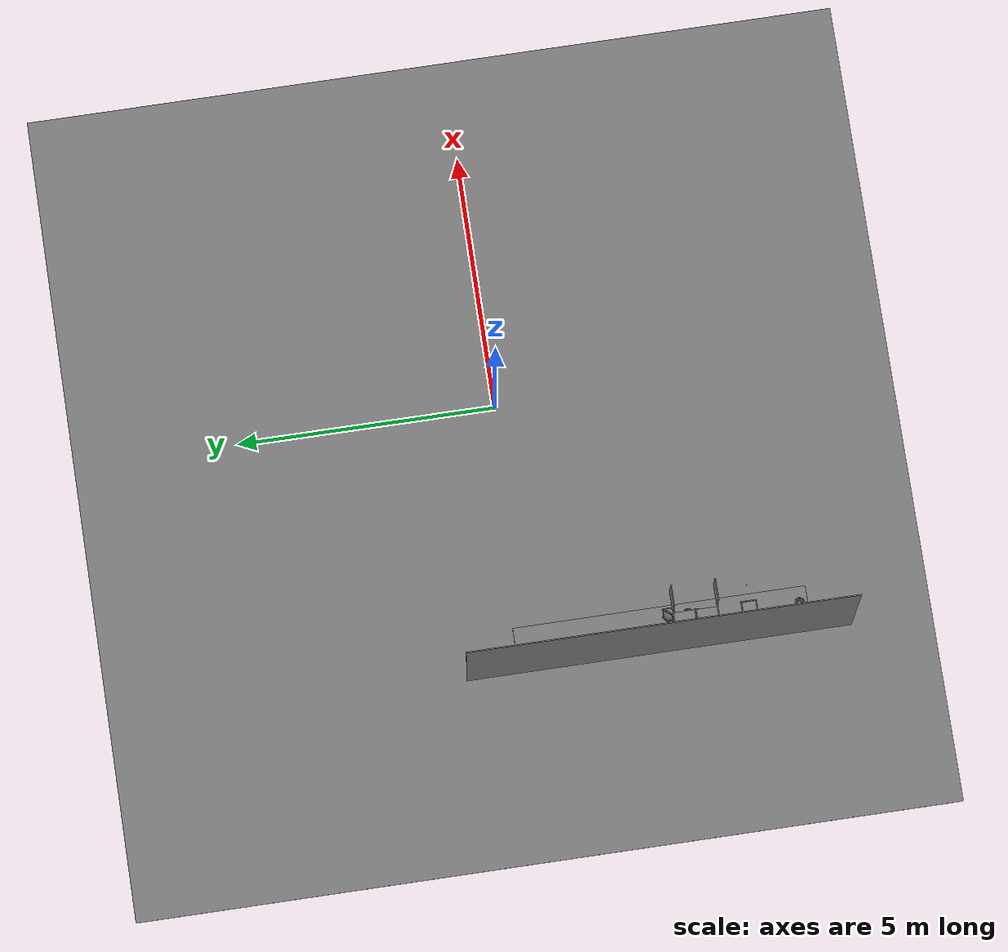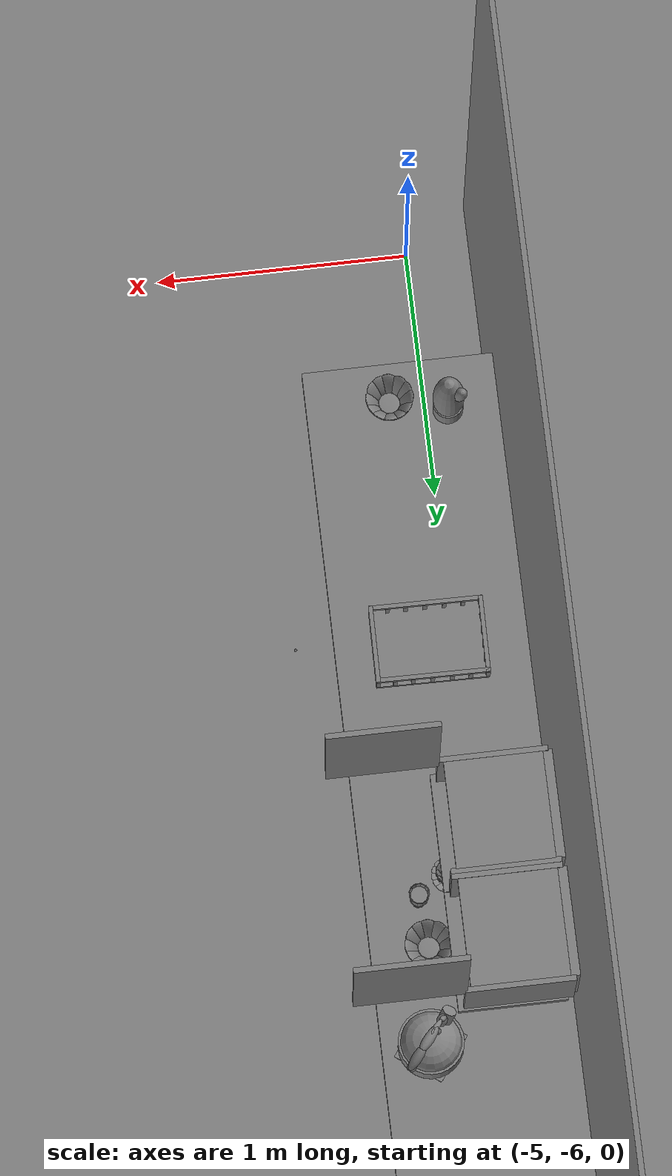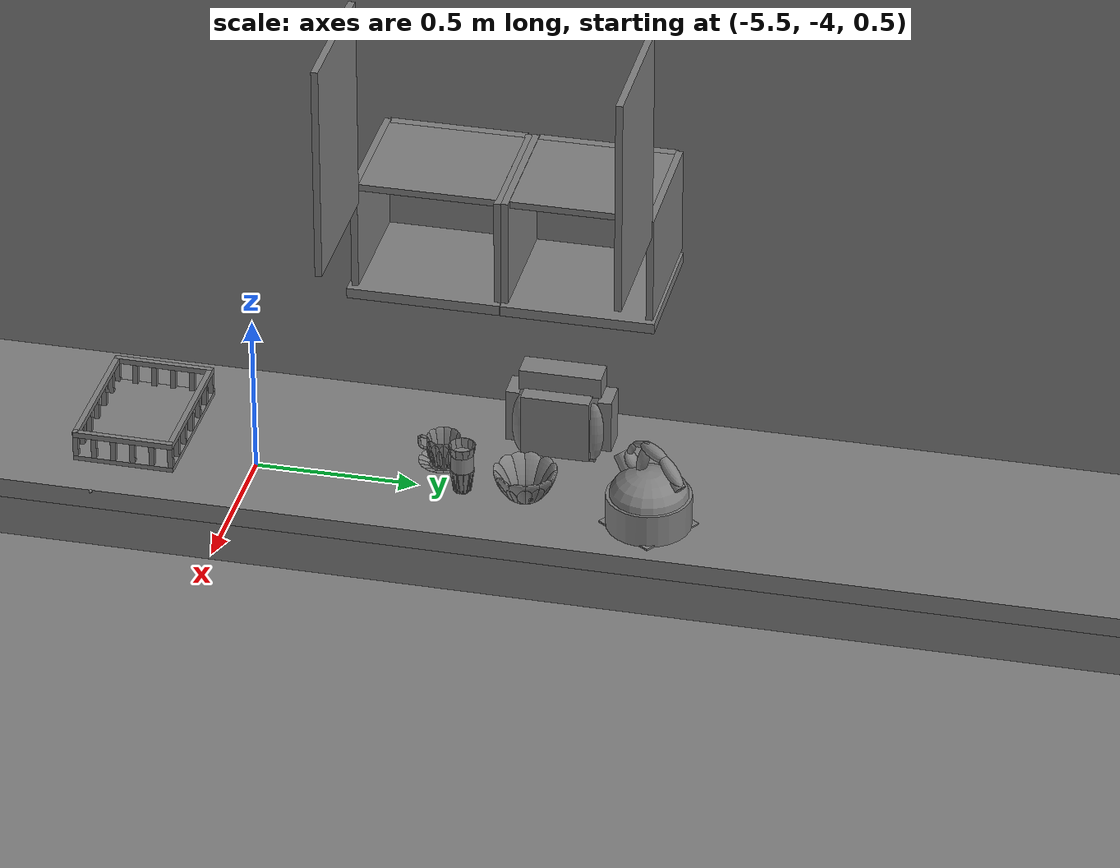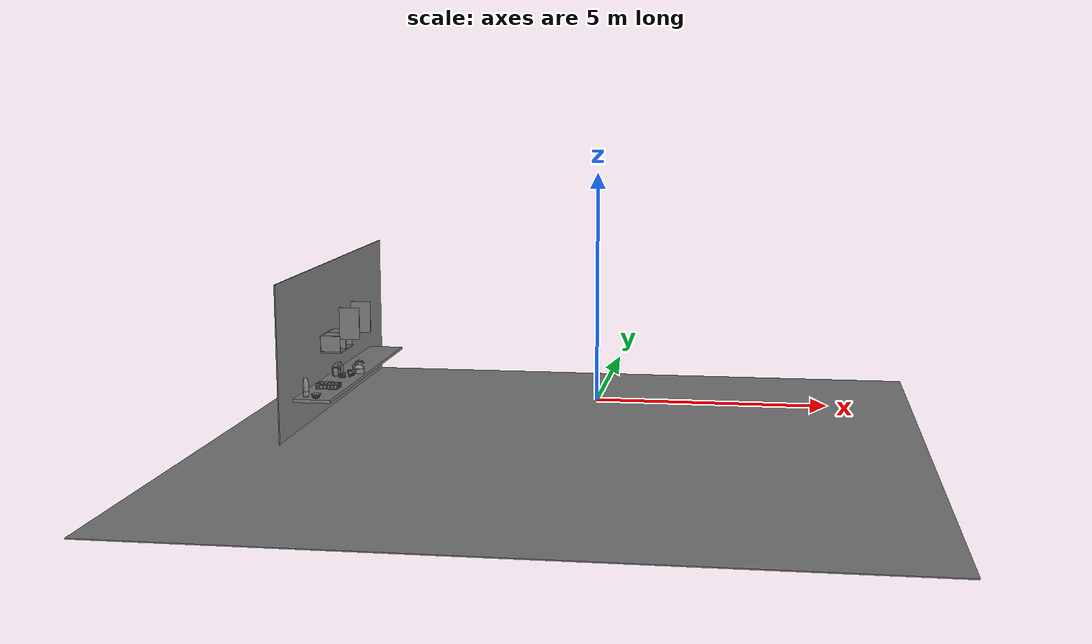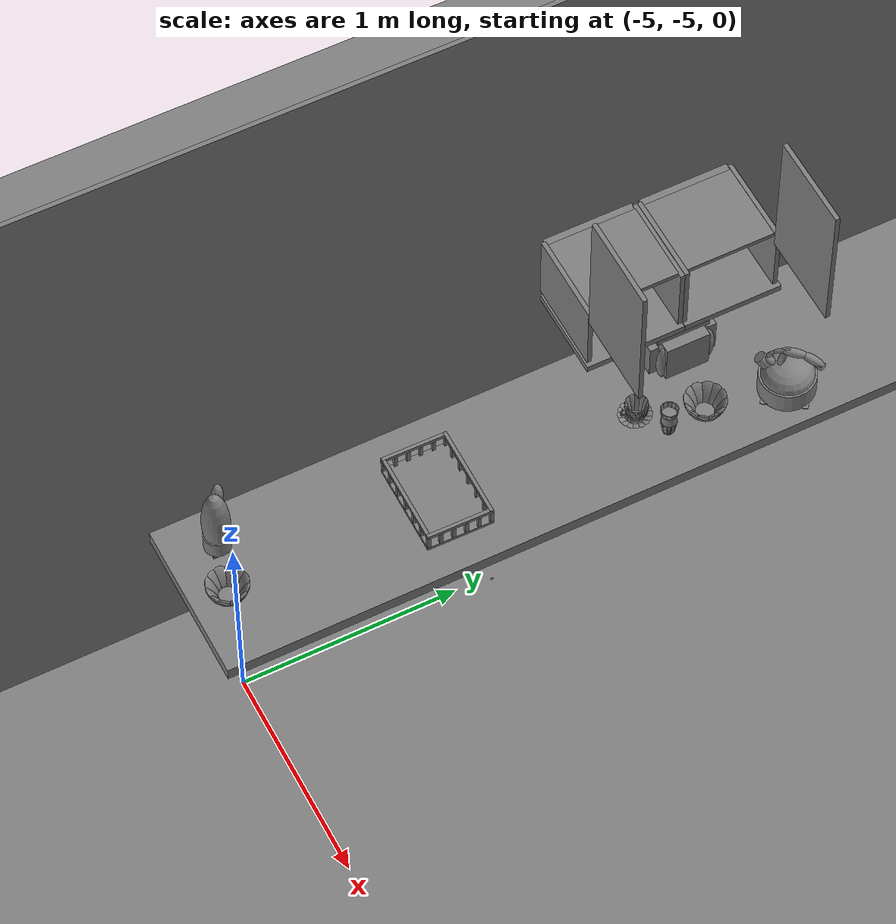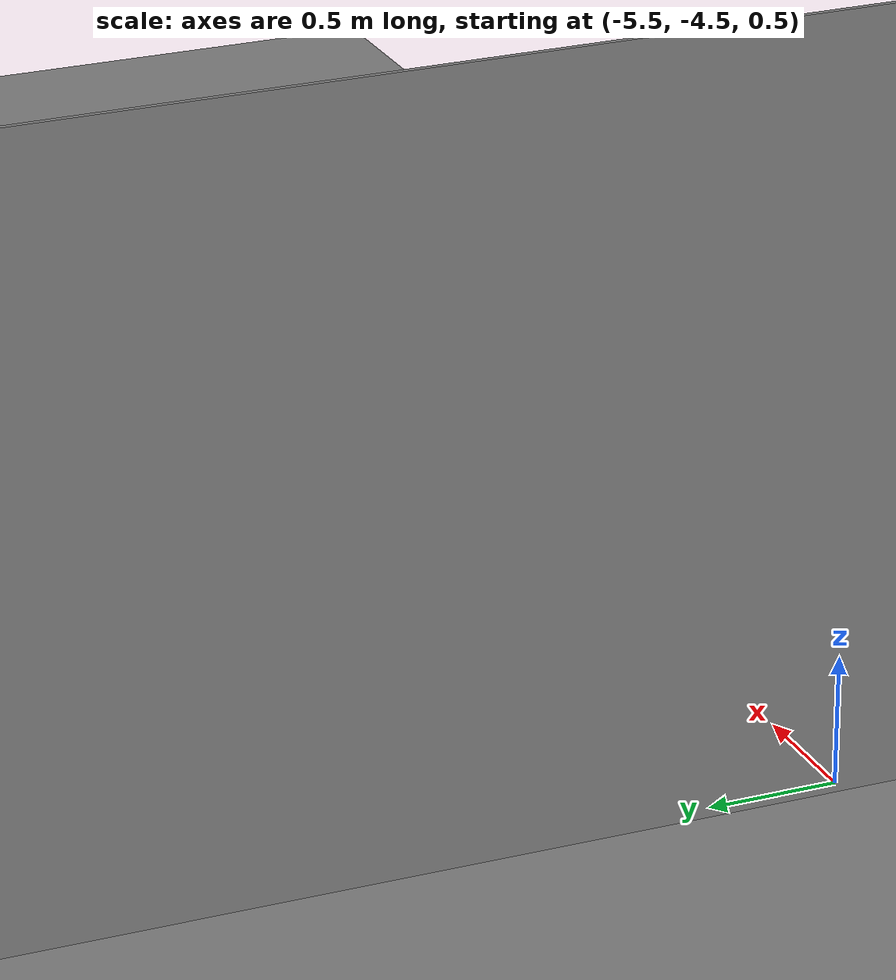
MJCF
<mujoco>
    <option gravity="0.000000000 0.000000000 -9.810000420" timestep="0.0049999999" integrator="implicitfast" density="9.8000002" viscosity="1.8000001e-05" noslip_iterations="10" iterations="100" sdf_iterations="50">
        <flag multiccd="disable"/>
    </option>
    <size memory="1000M"/>
    <compiler coordinate="local"/>
    <worldbody>
        <light cutoff="30" pos="0 1 1" dir="0 -1 -2"/>
        <light cutoff="30" pos="0 -1 1" dir="0 1 -2"/>
        <body pos="-4.860558510 -4.149443150 1.004824519" euler="0.000000000 0.000000000 -90.691093445" name="openloong_gripper_2f85_fix_base_usda_Basket_Kitchen_01">
            <geom contype="1" conaffinity="1" density="1000" type="box" material="" rgba="0.500000000 0.500000000 0.500000000 1.000000000" solimp="0.899999976 0.949999988 0.001000000" friction="1.000000000 0.005000000 0.000100000" solref="0.020000000 1.000000000" margin="0" condim="3" group="0" pos="0.086542509 0.207580954 0.047887992" quat="0.707107008 0.000000000 0.000000000 0.707106411" size="0.007600000 0.007600000 0.032000002" name="openloong_gripper_2f85_fix_base_usda_geom_D7910266_F74E_4D35_A255_E9B7815349CB"/>
            <geom contype="1" conaffinity="1" density="1000" type="box" material="" rgba="0.500000000 0.500000000 0.500000000 1.000000000" solimp="0.899999976 0.949999988 0.001000000" friction="1.000000000 0.005000000 0.000100000" solref="0.020000000 1.000000000" margin="0" condim="3" group="0" pos="-0.140816495 0.143605426 0.047889423" quat="0.707107008 0.000000000 0.000000000 0.707106411" size="0.007600000 0.007600000 0.032000002" name="openloong_gripper_2f85_fix_base_usda_geom_2C70FBF7_947E_40A4_8346_38A32DEE118F"/>
            <geom contype="1" conaffinity="1" density="1000" type="box" material="" rgba="0.500000000 0.500000000 0.500000000 1.000000000" solimp="0.899999976 0.949999988 0.001000000" friction="1.000000000 0.005000000 0.000100000" solref="0.020000000 1.000000000" margin="0" condim="3" group="0" pos="-0.140816212 -0.070956804 0.047888946" quat="0.707107008 0.000000000 0.000000000 0.707106411" size="0.007600000 0.007600000 0.032000002" name="openloong_gripper_2f85_fix_base_usda_geom_8F16A768_AC28_4A24_A64F_205EF4F02D3E"/>
            <geom contype="1" conaffinity="1" density="1000" type="box" material="" rgba="0.500000000 0.500000000 0.500000000 1.000000000" solimp="0.899999976 0.949999988 0.001000000" friction="1.000000000 0.005000000 0.000100000" solref="0.020000000 1.000000000" margin="0" condim="3" group="0" pos="0.140802577 0.207580566 0.047887899" quat="0.707107008 0.000000000 0.000000000 0.707106411" size="0.007600000 0.007600000 0.032000002" name="openloong_gripper_2f85_fix_base_usda_geom_3D83A185_28E2_4451_B326_0791F0CD8104"/>
            <geom contype="1" conaffinity="1" density="1000" type="box" material="" rgba="0.500000000 0.500000000 0.500000000 1.000000000" solimp="0.899999976 0.949999988 0.001000000" friction="1.000000000 0.005000000 0.000100000" solref="0.020000000 1.000000000" margin="0" condim="3" group="0" pos="0.086541750 -0.207636267 0.047888279" quat="0.707107008 0.000000000 0.000000000 0.707106411" size="0.007600000 0.007600000 0.032000002" name="openloong_gripper_2f85_fix_base_usda_geom_C0A9CB53_DA36_4D4C_B38A_6A66528DB9B0"/>
            <geom contype="1" conaffinity="1" density="1000" type="box" material="" rgba="0.500000000 0.500000000 0.500000000 1.000000000" solimp="0.899999976 0.949999988 0.001000000" friction="1.000000000 0.005000000 0.000100000" solref="0.020000000 1.000000000" margin="0" condim="3" group="0" pos="0.140633777 -0.000001907 0.087263681" quat="0.707107008 0.000000000 0.000000000 0.707106411" size="0.215199992 0.008000000 0.008400000" name="openloong_gripper_2f85_fix_base_usda_geom_E28D9E4D_E42C_4E9C_A4CE_75A715E72C45"/>
            <geom contype="1" conaffinity="1" density="1000" type="box" material="" rgba="0.500000000 0.500000000 0.500000000 1.000000000" solimp="0.899999976 0.949999988 0.001000000" friction="1.000000000 0.005000000 0.000100000" solref="0.020000000 1.000000000" margin="0" condim="3" group="0" pos="-0.027960587 -0.207636639 0.047888566" quat="0.707107008 0.000000000 0.000000000 0.707106411" size="0.007600000 0.007600000 0.032000002" name="openloong_gripper_2f85_fix_base_usda_geom_FAB28F0B_00A8_4D75_8538_290FD11CC164"/>
            <geom contype="1" conaffinity="1" density="1000" type="box" material="" rgba="0.500000000 0.500000000 0.500000000 1.000000000" solimp="0.899999976 0.949999988 0.001000000" friction="1.000000000 0.005000000 0.000100000" solref="0.020000000 1.000000000" margin="0" condim="3" group="0" pos="-0.140816122 -0.141625211 0.047888853" quat="0.707107008 0.000000000 0.000000000 0.707106411" size="0.007600000 0.007600000 0.032000002" name="openloong_gripper_2f85_fix_base_usda_geom_12E4F63D_2F76_46B4_9240_C48A81197D10"/>
            <geom contype="1" conaffinity="1" density="1000" type="box" material="" rgba="0.500000000 0.500000000 0.500000000 1.000000000" solimp="0.899999976 0.949999988 0.001000000" friction="1.000000000 0.005000000 0.000100000" solref="0.020000000 1.000000000" margin="0" condim="3" group="0" pos="-0.140816122 0.207580194 0.047888756" quat="0.707107008 0.000000000 0.000000000 0.707106411" size="0.007600000 0.007600000 0.032000002" name="openloong_gripper_2f85_fix_base_usda_geom_1DF41569_742C_4B02_AE99_C97C3AE0AE28"/>
            <geom contype="1" conaffinity="1" density="1000" type="box" material="" rgba="0.500000000 0.500000000 0.500000000 1.000000000" solimp="0.899999976 0.949999988 0.001000000" friction="1.000000000 0.005000000 0.000100000" solref="0.020000000 1.000000000" margin="0" condim="3" group="0" pos="0.140800864 -0.070956804 0.047888376" quat="0.707107008 0.000000000 0.000000000 0.707106411" size="0.007600000 0.007600000 0.032000002" name="openloong_gripper_2f85_fix_base_usda_geom_10AE1FB1_DF70_4758_BE02_D55683CDE5BC"/>
            <geom contype="1" conaffinity="1" density="1000" type="box" material="" rgba="0.500000000 0.500000000 0.500000000 1.000000000" solimp="0.899999976 0.949999988 0.001000000" friction="1.000000000 0.005000000 0.000100000" solref="0.020000000 1.000000000" margin="0" condim="3" group="0" pos="0.140800476 0.002393341 0.047888376" quat="0.707107008 0.000000000 0.000000000 0.707106411" size="0.007600000 0.007600000 0.032000002" name="openloong_gripper_2f85_fix_base_usda_geom_D1CCFF11_C779_4BE3_B151_67915929E82C"/>
            <geom contype="1" conaffinity="1" density="1000" type="box" material="" rgba="0.500000000 0.500000000 0.500000000 1.000000000" solimp="0.899999976 0.949999988 0.001000000" friction="1.000000000 0.005000000 0.000100000" solref="0.020000000 1.000000000" margin="0" condim="3" group="0" pos="-0.140543848 -0.000001526 0.087263964" quat="0.707107008 0.000000000 0.000000000 0.707106411" size="0.215199992 0.008000000 0.008400000" name="openloong_gripper_2f85_fix_base_usda_geom_13193519_061A_49D2_991C_27A965ADA620"/>
            <geom contype="1" conaffinity="1" density="1000" type="box" material="" rgba="0.500000000 0.500000000 0.500000000 1.000000000" solimp="0.899999976 0.949999988 0.001000000" friction="1.000000000 0.005000000 0.000100000" solref="0.020000000 1.000000000" margin="0" condim="3" group="0" pos="-0.140816018 0.075380705 0.047889233" quat="0.707107008 0.000000000 0.000000000 0.707106411" size="0.007600000 0.007600000 0.032000002" name="openloong_gripper_2f85_fix_base_usda_geom_02A7C59E_DCCC_4627_8DD2_16382EBE39B4"/>
            <geom contype="1" conaffinity="1" density="1000" type="box" material="" rgba="0.500000000 0.500000000 0.500000000 1.000000000" solimp="0.899999976 0.949999988 0.001000000" friction="1.000000000 0.005000000 0.000100000" solref="0.020000000 1.000000000" margin="0" condim="3" group="0" pos="0.140801147 -0.141625211 0.047888279" quat="0.707107008 0.000000000 0.000000000 0.707106411" size="0.007600000 0.007600000 0.032000002" name="openloong_gripper_2f85_fix_base_usda_geom_D05C9458_215E_4D71_86ED_79DA9F77F6DE"/>
            <geom contype="1" conaffinity="1" density="1000" type="box" material="" rgba="0.500000000 0.500000000 0.500000000 1.000000000" solimp="0.899999976 0.949999988 0.001000000" friction="1.000000000 0.005000000 0.000100000" solref="0.020000000 1.000000000" margin="0" condim="3" group="0" pos="0.000000000 -0.207717523 0.087263964" quat="0.707107008 0.000000000 0.000000000 0.707106411" size="0.008000000 0.148000002 0.008400000" name="openloong_gripper_2f85_fix_base_usda_geom_FF5B8F15_9D02_4E77_A448_AEF5BCCBCB11"/>
            <geom contype="1" conaffinity="1" density="1000" type="box" material="" rgba="0.500000000 0.500000000 0.500000000 1.000000000" solimp="0.899999976 0.949999988 0.001000000" friction="1.000000000 0.005000000 0.000100000" solref="0.020000000 1.000000000" margin="0" condim="3" group="0" pos="0.029044246 -0.207635880 0.047888376" quat="0.707107008 0.000000000 0.000000000 0.707106411" size="0.007600000 0.007600000 0.032000002" name="openloong_gripper_2f85_fix_base_usda_geom_60DA7DED_2678_444E_88D5_3C3515DCBB6D"/>
            <geom contype="1" conaffinity="1" density="1000" type="box" material="" rgba="0.500000000 0.500000000 0.500000000 1.000000000" solimp="0.899999976 0.949999988 0.001000000" friction="1.000000000 0.005000000 0.000100000" solref="0.020000000 1.000000000" margin="0" condim="3" group="0" pos="0.140800476 0.075379565 0.047888566" quat="0.707107008 0.000000000 0.000000000 0.707106411" size="0.007600000 0.007600000 0.032000002" name="openloong_gripper_2f85_fix_base_usda_geom_1E1E1A1E_A530_4B96_884F_F391F7012D18"/>
            <geom contype="1" conaffinity="1" density="1000" type="box" material="" rgba="0.500000000 0.500000000 0.500000000 1.000000000" solimp="0.899999976 0.949999988 0.001000000" friction="1.000000000 0.005000000 0.000100000" solref="0.020000000 1.000000000" margin="0" condim="3" group="0" pos="-0.027959539 0.207580566 0.047888376" quat="0.707107008 0.000000000 0.000000000 0.707106411" size="0.007600000 0.007600000 0.032000002" name="openloong_gripper_2f85_fix_base_usda_geom_62916F2F_1A76_460F_ABBC_E00B0AA770F3"/>
            <geom contype="1" conaffinity="1" density="1000" type="box" material="" rgba="0.500000000 0.500000000 0.500000000 1.000000000" solimp="0.899999976 0.949999988 0.001000000" friction="1.000000000 0.005000000 0.000100000" solref="0.020000000 1.000000000" margin="0" condim="3" group="0" pos="0.140799999 0.143604279 0.047888756" quat="0.707107008 0.000000000 0.000000000 0.707106411" size="0.007600000 0.007600000 0.032000002" name="openloong_gripper_2f85_fix_base_usda_geom_35014F77_3CC7_443D_B6CD_64CF80952B73"/>
            <geom contype="1" conaffinity="1" density="1000" type="box" material="" rgba="0.500000000 0.500000000 0.500000000 1.000000000" solimp="0.899999976 0.949999988 0.001000000" friction="1.000000000 0.005000000 0.000100000" solref="0.020000000 1.000000000" margin="0" condim="3" group="0" pos="-0.140816122 0.002393723 0.047889233" quat="0.707107008 0.000000000 0.000000000 0.707106411" size="0.007600000 0.007600000 0.032000002" name="openloong_gripper_2f85_fix_base_usda_geom_F5187ED7_1B6A_4F38_9EAE_99E4CAA4BA03"/>
            <geom contype="1" conaffinity="1" density="1000" type="box" material="" rgba="0.500000000 0.500000000 0.500000000 1.000000000" solimp="0.899999976 0.949999988 0.001000000" friction="1.000000000 0.005000000 0.000100000" solref="0.020000000 1.000000000" margin="0" condim="3" group="0" pos="-0.085476689 0.207580194 0.047888566" quat="0.707107008 0.000000000 0.000000000 0.707106411" size="0.007600000 0.007600000 0.032000002" name="openloong_gripper_2f85_fix_base_usda_geom_B49AA1FE_F807_4B04_9A36_E8E88AC794B6"/>
            <geom contype="1" conaffinity="1" density="1000" type="box" material="" rgba="0.500000000 0.500000000 0.500000000 1.000000000" solimp="0.899999976 0.949999988 0.001000000" friction="1.000000000 0.005000000 0.000100000" solref="0.020000000 1.000000000" margin="0" condim="3" group="0" pos="0.000000000 0.207718283 0.087263964" quat="0.707107008 0.000000000 0.000000000 0.707106411" size="0.008000000 0.148000002 0.008400000" name="openloong_gripper_2f85_fix_base_usda_geom_F1024203_EA60_4066_B1DB_E9BB1C13B216"/>
            <geom contype="1" conaffinity="1" density="1000" type="box" material="" rgba="0.500000000 0.500000000 0.500000000 1.000000000" solimp="0.899999976 0.949999988 0.001000000" friction="1.000000000 0.005000000 0.000100000" solref="0.020000000 1.000000000" margin="0" condim="3" group="0" pos="0.029045582 0.207581714 0.047888279" quat="0.707107008 0.000000000 0.000000000 0.707106411" size="0.007600000 0.007600000 0.032000002" name="openloong_gripper_2f85_fix_base_usda_geom_F615D46F_28E3_45B2_992A_8C7D020A9F3B"/>
            <geom contype="1" conaffinity="1" density="1000" type="box" material="" rgba="0.500000000 0.500000000 0.500000000 1.000000000" solimp="0.899999976 0.949999988 0.001000000" friction="1.000000000 0.005000000 0.000100000" solref="0.020000000 1.000000000" margin="0" condim="3" group="0" pos="-0.140816122 -0.207636267 0.047888853" quat="0.707107008 0.000000000 0.000000000 0.707106411" size="0.007600000 0.007600000 0.032000002" name="openloong_gripper_2f85_fix_base_usda_geom_BF2046E7_4A77_47F5_B4F1_D10DD326EAFB"/>
            <geom contype="1" conaffinity="1" density="1000" type="box" material="" rgba="0.500000000 0.500000000 0.500000000 1.000000000" solimp="0.899999976 0.949999988 0.001000000" friction="1.000000000 0.005000000 0.000100000" solref="0.020000000 1.000000000" margin="0" condim="3" group="0" pos="-0.085477069 -0.207636639 0.047888756" quat="0.707107008 0.000000000 0.000000000 0.707106411" size="0.007600000 0.007600000 0.032000002" name="openloong_gripper_2f85_fix_base_usda_geom_FF6E1DC3_A7F4_4CC1_9C1E_6D55E7F19DC7"/>
            <geom contype="1" conaffinity="1" density="1000" type="box" material="" rgba="0.500000000 0.500000000 0.500000000 1.000000000" solimp="0.899999976 0.949999988 0.001000000" friction="1.000000000 0.005000000 0.000100000" solref="0.020000000 1.000000000" margin="0" condim="3" group="0" pos="-0.000012112 0.000000381 0.008534336" quat="0.707107008 0.000000000 0.000000000 0.707106411" size="0.215199992 0.148800001 0.008400000" name="openloong_gripper_2f85_fix_base_usda_geom_2882BD7B_91C3_44AD_9222_B172E662BE5C"/>
            <geom contype="1" conaffinity="1" density="1000" type="box" material="" rgba="0.500000000 0.500000000 0.500000000 1.000000000" solimp="0.899999976 0.949999988 0.001000000" friction="1.000000000 0.005000000 0.000100000" solref="0.020000000 1.000000000" margin="0" condim="3" group="0" pos="0.140801623 -0.207636267 0.047888186" quat="0.707107008 0.000000000 0.000000000 0.707106411" size="0.007600000 0.007600000 0.032000002" name="openloong_gripper_2f85_fix_base_usda_geom_AAD0B3E8_9893_47CB_B391_F2A52C3D59BF"/>
            <freejoint name="openloong_gripper_2f85_fix_base_usda_Basket_Kitchen_01_joint"/>
            <site size="0.005000000 0.005000000 0.005000000" rgba="0.500000000 0.500000000 0.500000000 1.000000000" pos="0.000000000 0.000000000 0.000000000" quat="1.000000000 0.000000000 0.000000000 0.000000000" group="0" type="sphere" name="openloong_gripper_2f85_fix_base_usda_Basket_Kitchen_01site"/>
        </body>
        <body pos="-4.721817970 -2.990536690 1.027358174" euler="0.000000000 0.000000000 89.999946594" name="Interactive Objcets_bow_02">
            <geom contype="1" conaffinity="1" density="1000" type="ellipsoid" material="" rgba="0.500000000 0.500000000 0.500000000 1.000000000" solimp="0.899999976 0.949999988 0.001000000" friction="1.000000000 0.005000000 0.000100000" solref="0.020000000 1.000000000" margin="0" condim="3" group="0" pos="-0.058925860 -0.029528141 0.044118762" quat="0.223252773 0.231952101 0.054787740 -0.945174515" size="0.010000000 0.039999999 0.052000001" name="Interactive Objcets_geom_89023988_6A35_4E91_97B5_07944ED13776"/>
            <geom contype="1" conaffinity="1" density="1000" type="ellipsoid" material="" rgba="0.500000000 0.500000000 0.500000000 1.000000000" solimp="0.899999976 0.949999988 0.001000000" friction="1.000000000 0.005000000 0.000100000" solref="0.020000000 1.000000000" margin="0" condim="3" group="0" pos="0.000082973 0.000000000 0.000446677" quat="1.000000000 0.000000000 0.000000000 0.000000000" size="0.039999999 0.039999999 0.002000000" name="Interactive Objcets_geom_74B5FF42_3F95_49CC_8F32_4D20BCDC7A1A"/>
            <geom contype="1" conaffinity="1" density="1000" type="ellipsoid" material="" rgba="0.500000000 0.500000000 0.500000000 1.000000000" solimp="0.899999976 0.949999988 0.001000000" friction="1.000000000 0.005000000 0.000100000" solref="0.020000000 1.000000000" margin="0" condim="3" group="0" pos="0.029448029 -0.059084892 0.044118762" quat="0.825555801 0.125530601 0.202597082 -0.511521280" size="0.010000000 0.039999999 0.052000001" name="Interactive Objcets_geom_FF245CAB_6CA4_440B_B395_36555D82C481"/>
            <geom contype="1" conaffinity="1" density="1000" type="ellipsoid" material="" rgba="0.500000000 0.500000000 0.500000000 1.000000000" solimp="0.899999976 0.949999988 0.001000000" friction="1.000000000 0.005000000 0.000100000" solref="0.020000000 1.000000000" margin="0" condim="3" group="0" pos="0.000082973 0.000000000 0.005656481" quat="1.000000000 0.000000000 0.000000000 0.000000000" size="0.039999999 0.039999999 0.002000000" name="Interactive Objcets_geom_EDFA62A4_3C9E_4AE8_AFC7_5AFF7886A6C2"/>
            <geom contype="1" conaffinity="1" density="1000" type="ellipsoid" material="" rgba="0.500000000 0.500000000 0.500000000 1.000000000" solimp="0.899999976 0.949999988 0.001000000" friction="1.000000000 0.005000000 0.000100000" solref="0.020000000 1.000000000" margin="0" condim="3" group="0" pos="-0.040080305 -0.052354336 0.044118762" quat="0.429593205 0.213749886 0.105425082 -0.871003032" size="0.010000000 0.039999999 0.052000001" name="Interactive Objcets_geom_73960456_8419_46D4_AE6C_252EA24FC163"/>
            <geom contype="1" conaffinity="1" density="1000" type="ellipsoid" material="" rgba="0.500000000 0.500000000 0.500000000 1.000000000" solimp="0.899999976 0.949999988 0.001000000" friction="1.000000000 0.005000000 0.000100000" solref="0.020000000 1.000000000" margin="0" condim="3" group="0" pos="-0.065898418 -0.000007629 0.044118762" quat="0.971183062 -0.000000142 -0.238334835 0.000000030" size="0.010000000 0.039999999 0.052000001" name="Interactive Objcets_geom_AA15CD44_0D00_4C1D_8306_87A9A6214F91"/>
            <geom contype="1" conaffinity="1" density="1000" type="ellipsoid" material="" rgba="0.500000000 0.500000000 0.500000000 1.000000000" solimp="0.899999976 0.949999988 0.001000000" friction="1.000000000 0.005000000 0.000100000" solref="0.020000000 1.000000000" margin="0" condim="3" group="0" pos="0.059080135 0.029512405 0.044118762" quat="0.223252743 -0.231952220 -0.054787420 -0.945174456" size="0.010000000 0.039999999 0.052000001" name="Interactive Objcets_geom_6B904C9A_88F0_44EB_9FC6_F5CAD2FF528B"/>
            <geom contype="1" conaffinity="1" density="1000" type="ellipsoid" material="" rgba="0.500000000 0.500000000 0.500000000 1.000000000" solimp="0.899999976 0.949999988 0.001000000" friction="1.000000000 0.005000000 0.000100000" solref="0.020000000 1.000000000" margin="0" condim="3" group="0" pos="0.066052437 -0.000007629 0.044118762" quat="0.971183062 -0.000000156 0.238334835 0.000000030" size="0.010000000 0.039999999 0.052000001" name="Interactive Objcets_geom_B1C78199_BA00_47D8_BB8E_78A760D2AE59"/>
            <geom contype="1" conaffinity="1" density="1000" type="ellipsoid" material="" rgba="0.500000000 0.500000000 0.500000000 1.000000000" solimp="0.899999976 0.949999988 0.001000000" friction="1.000000000 0.005000000 0.000100000" solref="0.020000000 1.000000000" margin="0" condim="3" group="0" pos="0.000243668 -0.065982819 0.044118762" quat="0.687598705 0.168314636 0.168741375 -0.685860336" size="0.010000000 0.039999999 0.052000001" name="Interactive Objcets_geom_0F58360A_2F54_41FA_9C46_8F73433B9A31"/>
            <geom contype="1" conaffinity="1" density="1000" type="ellipsoid" material="" rgba="0.500000000 0.500000000 0.500000000 1.000000000" solimp="0.899999976 0.949999988 0.001000000" friction="1.000000000 0.005000000 0.000100000" solref="0.020000000 1.000000000" margin="0" condim="3" group="0" pos="-0.000090118 0.065967560 0.044118762" quat="0.687598705 -0.168314859 -0.168741152 -0.685860336" size="0.010000000 0.039999999 0.052000001" name="Interactive Objcets_geom_145D593E_26AC_44F9_9EE7_B9F44B85E9E0"/>
            <geom contype="1" conaffinity="1" density="1000" type="ellipsoid" material="" rgba="0.500000000 0.500000000 0.500000000 1.000000000" solimp="0.899999976 0.949999988 0.001000000" friction="1.000000000 0.005000000 0.000100000" solref="0.020000000 1.000000000" margin="0" condim="3" group="0" pos="0.052321676 -0.040297508 0.044118762" quat="0.919264674 0.076882742 0.225593731 -0.313287675" size="0.010000000 0.039999999 0.052000001" name="Interactive Objcets_geom_384A9E4B_B1E5_4A32_A76D_1B8C66A8B674"/>
            <geom contype="1" conaffinity="1" density="1000" type="ellipsoid" material="" rgba="0.500000000 0.500000000 0.500000000 1.000000000" solimp="0.899999976 0.949999988 0.001000000" friction="1.000000000 0.005000000 0.000100000" solref="0.020000000 1.000000000" margin="0" condim="3" group="0" pos="0.040234569 0.052338600 0.044118762" quat="0.429593176 -0.213750035 -0.105424814 -0.871002913" size="0.010000000 0.039999999 0.052000001" name="Interactive Objcets_geom_0192834B_08D6_481A_B82E_CC96E8BA89F3"/>
            <geom contype="1" conaffinity="1" density="1000" type="ellipsoid" material="" rgba="0.500000000 0.500000000 0.500000000 1.000000000" solimp="0.899999976 0.949999988 0.001000000" friction="1.000000000 0.005000000 0.000100000" solref="0.020000000 1.000000000" margin="0" condim="3" group="0" pos="-0.052167647 0.040282249 0.044118762" quat="0.919264615 -0.076883025 -0.225593641 -0.313287735" size="0.010000000 0.039999999 0.052000001" name="Interactive Objcets_geom_68091FE6_0AA3_4FB2_BF00_85D11F156594"/>
            <geom contype="1" conaffinity="1" density="1000" type="ellipsoid" material="" rgba="0.500000000 0.500000000 0.500000000 1.000000000" solimp="0.899999976 0.949999988 0.001000000" friction="1.000000000 0.005000000 0.000100000" solref="0.020000000 1.000000000" margin="0" condim="3" group="0" pos="-0.029293532 0.059069633 0.044118762" quat="0.825555801 -0.125530809 -0.202596903 -0.511521280" size="0.010000000 0.039999999 0.052000001" name="Interactive Objcets_geom_F2F7B8F4_656A_4D9D_BD54_03CA6C32A93F"/>
            <freejoint name="Interactive Objcets_bow_02"/>
        </body>
        <body pos="-4.802892208 -3.488179445 1.876015186" euler="89.999992371 -89.999946594 0.000000000" name="Interactive Objcets_guimen_01">
            <geom contype="1" conaffinity="1" density="1000" type="box" material="" rgba="0.500000000 0.500000000 0.500000000 1.000000000" solimp="0.899999976 0.949999988 0.001000000" friction="1.000000000 0.005000000 0.000100000" solref="0.020000000 1.000000000" margin="0" condim="3" group="0" pos="0.006727934 0.314709902 -0.203009605" quat="1.000000000 0.000000119 -0.000000119 0.000000000" size="0.010000000 0.317999989 0.204999998" name="Interactive Objcets_geom_5313736A_2FB8_4941_A804_0E25BBF74B48"/>
            <joint armature="0" stiffness="0" damping="1" axis="0.000000 1.000000 0.000000" type="hinge" name="Interactive Objcets_guimen_01"/>
        </body>
        <body pos="-4.827295780 -3.287638187 1.074643731" euler="0.000000000 0.000000000 89.999992371" name="Interactive Objcets_coffeecup_01">
            <geom contype="1" conaffinity="1" density="1000" type="ellipsoid" material="" rgba="0.500000000 0.500000000 0.500000000 1.000000000" solimp="0.899999976 0.949999988 0.001000000" friction="1.000000000 0.005000000 0.000100000" solref="0.020000000 1.000000000" margin="0" condim="3" group="0" pos="0.053700209 0.033117294 0.002976775" quat="0.496025741 -0.082236379 -0.047260769 -0.863111615" size="0.005000000 0.029999999 0.048999999" name="Interactive Objcets_geom_B6CF4233_9195_4B35_B462_8269BE1890A5"/>
            <geom contype="1" conaffinity="1" density="1000" type="ellipsoid" material="" rgba="0.500000000 0.500000000 0.500000000 1.000000000" solimp="0.899999976 0.949999988 0.001000000" friction="1.000000000 0.005000000 0.000100000" solref="0.020000000 1.000000000" margin="0" condim="3" group="0" pos="0.068445444 0.017385960 0.002976775" quat="0.228377223 -0.092319682 -0.021759447 -0.968941331" size="0.005000000 0.029999999 0.048999999" name="Interactive Objcets_geom_663200A9_D93B_464E_87A1_C284F4AEC9EF"/>
            <geom contype="1" conaffinity="1" density="1000" type="capsule" material="" rgba="0.500000000 0.500000000 0.500000000 1.000000000" solimp="0.899999976 0.949999988 0.001000000" friction="1.000000000 0.005000000 0.000100000" solref="0.020000000 1.000000000" margin="0" condim="3" group="0" pos="-0.030251026 0.000000000 0.004966617" quat="0.480583906 -0.000000000 0.876948774 -0.000000126" size="0.004000000 0.005000000 1.000000000" name="Interactive Objcets_geom_7131AE70_7235_4F69_980B_9228DD1C9DEC"/>
            <geom contype="1" conaffinity="1" density="1000" type="ellipsoid" material="" rgba="0.500000000 0.500000000 0.500000000 1.000000000" solimp="0.899999976 0.949999988 0.001000000" friction="1.000000000 0.005000000 0.000100000" solref="0.020000000 1.000000000" margin="0" condim="3" group="0" pos="0.034471050 -0.037125111 0.002976775" quat="0.701517045 0.067293778 0.066836871 -0.706313014" size="0.005000000 0.029999999 0.048999999" name="Interactive Objcets_geom_B57EF290_B0C7_430A_9580_70F1440E806F"/>
            <geom contype="1" conaffinity="1" density="1000" type="ellipsoid" material="" rgba="0.500000000 0.500000000 0.500000000 1.000000000" solimp="0.899999976 0.949999988 0.001000000" friction="1.000000000 0.005000000 0.000100000" solref="0.020000000 1.000000000" margin="0" condim="3" group="0" pos="0.035336256 0.000558376 -0.045152068" quat="0.999999881 0.000000000 0.000000000 0.000000000" size="0.029999999 0.029999999 0.001000000" name="Interactive Objcets_geom_E65ADC0B_9F53_4DAB_8331_4E215E3E67FA"/>
            <geom contype="1" conaffinity="1" density="1000" type="capsule" material="" rgba="0.500000000 0.500000000 0.500000000 1.000000000" solimp="0.899999976 0.949999988 0.001000000" friction="1.000000000 0.005000000 0.000100000" solref="0.020000000 1.000000000" margin="0" condim="3" group="0" pos="-0.021276474 0.000000000 0.038509369" quat="0.633189917 0.000000000 0.773996413 0.000000000" size="0.004000000 0.009000000 1.000000000" name="Interactive Objcets_geom_6A45C040_7B23_41F0_926E_A14EE7D225F7"/>
            <geom contype="1" conaffinity="1" density="1000" type="capsule" material="" rgba="0.500000000 0.500000000 0.500000000 1.000000000" solimp="0.899999976 0.949999988 0.001000000" friction="1.000000000 0.005000000 0.000100000" solref="0.020000000 1.000000000" margin="0" condim="3" group="0" pos="-0.018014431 0.000000000 0.001762271" quat="0.707106769 -0.000000004 0.707106709 -0.000000088" size="0.004000000 0.005000000 1.000000000" name="Interactive Objcets_geom_6ECF8433_3D07_43F0_B941_5665729F5EBC"/>
            <geom contype="1" conaffinity="1" density="1000" type="ellipsoid" material="" rgba="0.500000000 0.500000000 0.500000000 1.000000000" solimp="0.899999976 0.949999988 0.001000000" friction="1.000000000 0.005000000 0.000100000" solref="0.020000000 1.000000000" margin="0" condim="3" group="0" pos="0.001010895 -0.016271591 0.002976775" quat="0.228377163 0.092315644 0.021758538 -0.968941689" size="0.005000000 0.029999999 0.048999999" name="Interactive Objcets_geom_BBB69CA1_A26F_44FC_A8EF_B5F2E3D61AE2"/>
            <geom contype="1" conaffinity="1" density="1000" type="capsule" material="" rgba="0.500000000 0.500000000 0.500000000 1.000000000" solimp="0.899999976 0.949999988 0.001000000" friction="1.000000000 0.005000000 0.000100000" solref="0.020000000 1.000000000" margin="0" condim="3" group="0" pos="-0.008219719 0.000000000 -0.000944734" quat="0.364379913 0.000000063 0.931250274 -0.000000063" size="0.004000000 0.003000000 1.000000000" name="Interactive Objcets_geom_DEAB29A6_9778_4F1A_ADE3_22DF93BBE2BA"/>
            <geom contype="1" conaffinity="1" density="1000" type="ellipsoid" material="" rgba="0.500000000 0.500000000 0.500000000 1.000000000" solimp="0.899999976 0.949999988 0.001000000" friction="1.000000000 0.005000000 0.000100000" solref="0.020000000 1.000000000" margin="0" condim="3" group="0" pos="0.002039194 0.019308567 0.002976775" quat="0.961933970 -0.024419386 -0.091652036 -0.256293654" size="0.005000000 0.029999999 0.048999999" name="Interactive Objcets_geom_9D514CE4_7193_469D_A350_BD5D532B7CFE"/>
            <geom contype="1" conaffinity="1" density="1000" type="capsule" material="" rgba="0.500000000 0.500000000 0.500000000 1.000000000" solimp="0.899999976 0.949999988 0.001000000" friction="1.000000000 0.005000000 0.000100000" solref="0.020000000 1.000000000" margin="0" condim="3" group="0" pos="-0.033022881 0.000000000 0.037873149" quat="0.874267220 0.000000042 0.485444903 -0.000000084" size="0.004000000 0.004000000 1.000000000" name="Interactive Objcets_geom_750D6109_D141_4309_886E_1FC23553395C"/>
            <geom contype="1" conaffinity="1" density="1000" type="ellipsoid" material="" rgba="0.500000000 0.500000000 0.500000000 1.000000000" solimp="0.899999976 0.949999988 0.001000000" friction="1.000000000 0.005000000 0.000100000" solref="0.020000000 1.000000000" margin="0" condim="3" group="0" pos="0.034984604 0.038240910 0.002976775" quat="0.701516926 -0.067296736 -0.066839755 -0.706312656" size="0.005000000 0.029999999 0.048999999" name="Interactive Objcets_geom_9F4F4B03_752D_4EF6_AF62_123E487508D4"/>
            <geom contype="1" conaffinity="1" density="1000" type="ellipsoid" material="" rgba="0.500000000 0.500000000 0.500000000 1.000000000" solimp="0.899999976 0.949999988 0.001000000" friction="1.000000000 0.005000000 0.000100000" solref="0.020000000 1.000000000" margin="0" condim="3" group="0" pos="-0.002956629 0.000558376 0.002976775" quat="0.995491505 0.000000004 -0.094849378 -0.000000089" size="0.005000000 0.029999999 0.048999999" name="Interactive Objcets_geom_465C2958_A5B9_4DC0_86DE_E59BB2DA4E76"/>
            <geom contype="1" conaffinity="1" density="1000" type="ellipsoid" material="" rgba="0.500000000 0.500000000 0.500000000 1.000000000" solimp="0.899999976 0.949999988 0.001000000" friction="1.000000000 0.005000000 0.000100000" solref="0.020000000 1.000000000" margin="0" condim="3" group="0" pos="0.017669693 0.034160614 0.002976775" quat="0.848410904 -0.049618516 -0.080835648 -0.520770907" size="0.005000000 0.029999999 0.048999999" name="Interactive Objcets_geom_EFD5CA04_0FF5_4EBD_B42D_A72E2F3E5EB4"/>
            <geom contype="1" conaffinity="1" density="1000" type="ellipsoid" material="" rgba="0.500000000 0.500000000 0.500000000 1.000000000" solimp="0.899999976 0.949999988 0.001000000" friction="1.000000000 0.005000000 0.000100000" solref="0.020000000 1.000000000" margin="0" condim="3" group="0" pos="0.051787138 -0.033043861 0.002976775" quat="0.848411202 0.049616337 0.080832161 -0.520771146" size="0.005000000 0.029999999 0.048999999" name="Interactive Objcets_geom_FC162127_B616_4C68_B09B_AD03A5A172D8"/>
            <geom contype="1" conaffinity="1" density="1000" type="ellipsoid" material="" rgba="0.500000000 0.500000000 0.500000000 1.000000000" solimp="0.899999976 0.949999988 0.001000000" friction="1.000000000 0.005000000 0.000100000" solref="0.020000000 1.000000000" margin="0" condim="3" group="0" pos="0.035336256 0.000558376 -0.043215394" quat="0.999999881 0.000000000 0.000000000 0.000000000" size="0.029999999 0.029999999 0.001000000" name="Interactive Objcets_geom_08FEB940_2443_42FD_B8A8_A5B464BF4AE3"/>
            <geom contype="1" conaffinity="1" density="1000" type="capsule" material="" rgba="0.500000000 0.500000000 0.500000000 1.000000000" solimp="0.899999976 0.949999988 0.001000000" friction="1.000000000 0.005000000 0.000100000" solref="0.020000000 1.000000000" margin="0" condim="3" group="0" pos="-0.036300898 0.000000000 0.021037936" quat="0.044551343 -0.000000000 0.999007046 -0.000000126" size="0.004000000 0.012000000 1.000000000" name="Interactive Objcets_geom_A7D28F75_AC55_416A_BC54_3EB71F49713A"/>
            <geom contype="1" conaffinity="1" density="1000" type="ellipsoid" material="" rgba="0.500000000 0.500000000 0.500000000 1.000000000" solimp="0.899999976 0.949999988 0.001000000" friction="1.000000000 0.005000000 0.000100000" solref="0.020000000 1.000000000" margin="0" condim="3" group="0" pos="0.067416430 -0.018191338 0.002976775" quat="0.961934388 0.024418317 0.091648072 -0.256293803" size="0.005000000 0.029999999 0.048999999" name="Interactive Objcets_geom_20EFA873_FBCD_477F_86A9_086E1BB927FC"/>
            <geom contype="1" conaffinity="1" density="1000" type="ellipsoid" material="" rgba="0.500000000 0.500000000 0.500000000 1.000000000" solimp="0.899999976 0.949999988 0.001000000" friction="1.000000000 0.005000000 0.000100000" solref="0.020000000 1.000000000" margin="0" condim="3" group="0" pos="0.015755907 -0.032001972 0.002976775" quat="0.496025920 0.082232773 0.047258731 -0.863112032" size="0.005000000 0.029999999 0.048999999" name="Interactive Objcets_geom_A9CDE439_AA86_41D1_BB3A_AF7428F59995"/>
            <geom contype="1" conaffinity="1" density="1000" type="ellipsoid" material="" rgba="0.500000000 0.500000000 0.500000000 1.000000000" solimp="0.899999976 0.949999988 0.001000000" friction="1.000000000 0.005000000 0.000100000" solref="0.020000000 1.000000000" margin="0" condim="3" group="0" pos="0.072411790 0.000558376 0.002976775" quat="0.995491922 -0.000000019 0.094845265 -0.000000089" size="0.005000000 0.029999999 0.048999999" name="Interactive Objcets_geom_2623D5D2_145E_42C6_86F8_0EB534EFF815"/>
            <freejoint name="Interactive Objcets_coffeecup_01"/>
        </body>
        <body pos="-4.805274963 -2.665403366 1.876015186" euler="89.999877930 89.999969482 0.000000000" name="Interactive Objcets_guimen_02">
            <geom contype="1" conaffinity="1" density="1000" type="box" material="" rgba="0.500000000 0.500000000 0.500000000 1.000000000" solimp="0.899999976 0.949999988 0.001000000" friction="1.000000000 0.005000000 0.000100000" solref="0.020000000 1.000000000" margin="0" condim="3" group="0" pos="0.006727815 0.314709663 0.203009367" quat="0.999999940 0.000000000 0.000000000 0.000000000" size="0.010000000 0.317999989 0.204999998" name="Interactive Objcets_geom_8E52C4F4_811B_47DE_AEC8_D737C57EA3ED"/>
            <joint armature="0" stiffness="0" damping="1" axis="0.000000 1.000000 0.000000" type="hinge" name="Interactive Objcets_guimen_02"/>
        </body>
        <body pos="-4.705342293 -3.169416904 1.103703976" euler="0.000000000 0.000000000 0.000000000" name="Interactive Objcets_cup_02">
            <geom contype="1" conaffinity="1" density="1000" type="box" material="" rgba="0.500000000 0.500000000 0.500000000 1.000000000" solimp="0.899999976 0.949999988 0.001000000" friction="1.000000000 0.005000000 0.000100000" solref="0.020000000 1.000000000" margin="0" condim="3" group="0" pos="-0.016875744 0.022189617 -0.037281752" quat="0.944716334 -0.074092269 -0.024973858 0.318430305" size="0.010000000 0.001000000 0.035000000" name="Interactive Objcets_geom_2E937C4F_960E_41CF_98BF_9CFBEA641387"/>
            <geom contype="1" conaffinity="1" density="1000" type="box" material="" rgba="0.500000000 0.500000000 0.500000000 1.000000000" solimp="0.899999976 0.949999988 0.001000000" friction="1.000000000 0.005000000 0.000100000" solref="0.020000000 1.000000000" margin="0" condim="3" group="0" pos="0.029378891 -0.018181801 0.062637210" quat="0.870895982 0.068302706 0.038053915 0.485208035" size="0.010000000 0.001000000 0.015000000" name="Interactive Objcets_geom_CC028C66_83BB_4EED_B19A_55393810AE9D"/>
            <geom contype="1" conaffinity="1" density="1000" type="box" material="" rgba="0.500000000 0.500000000 0.500000000 1.000000000" solimp="0.899999976 0.949999988 0.001000000" friction="1.000000000 0.005000000 0.000100000" solref="0.020000000 1.000000000" margin="0" condim="3" group="0" pos="0.027999878 0.000000000 -0.037281752" quat="0.704941988 -0.055288255 0.055288251 -0.704942048" size="0.010000000 0.001000000 0.035000000" name="Interactive Objcets_geom_AB03AE54_1534_4C59_A19B_AF3F46F92291"/>
            <geom contype="1" conaffinity="1" density="1000" type="box" material="" rgba="0.500000000 0.500000000 0.500000000 1.000000000" solimp="0.899999976 0.949999988 0.001000000" friction="1.000000000 0.005000000 0.000100000" solref="0.020000000 1.000000000" margin="0" condim="3" group="0" pos="0.022285938 0.016949892 -0.037281752" quat="0.893179297 -0.070051625 0.034732576 -0.442851186" size="0.010000000 0.001000000 0.035000000" name="Interactive Objcets_geom_08AB6722_F9DF_4666_A358_D74E07F02959"/>
            <geom contype="1" conaffinity="1" density="1000" type="cylinder" material="" rgba="0.500000000 0.500000000 0.500000000 1.000000000" solimp="0.899999976 0.949999988 0.001000000" friction="1.000000000 0.005000000 0.000100000" solref="0.020000000 1.000000000" margin="0" condim="3" group="0" pos="0.000000000 0.000000000 0.022491097" quat="1.000000000 0.000000030 0.000000000 0.000000000" size="0.033000000 0.025000000 1.000000000" name="Interactive Objcets_geom_EC9CBEFC_30F0_4875_8452_D6598FA7D64B"/>
            <geom contype="1" conaffinity="1" density="1000" type="box" material="" rgba="0.500000000 0.500000000 0.500000000 1.000000000" solimp="0.899999976 0.949999988 0.001000000" friction="1.000000000 0.005000000 0.000100000" solref="0.020000000 1.000000000" margin="0" condim="3" group="0" pos="0.000000000 0.034549713 0.062637210" quat="0.996938646 -0.078187965 0.000000000 0.000000000" size="0.010000000 0.001000000 0.015000000" name="Interactive Objcets_geom_5A1431E4_B7DE_487A_9105_6DEAD61AA1E1"/>
            <geom contype="1" conaffinity="1" density="1000" type="box" material="" rgba="0.500000000 0.500000000 0.500000000 1.000000000" solimp="0.899999976 0.949999988 0.001000000" friction="1.000000000 0.005000000 0.000100000" solref="0.020000000 1.000000000" margin="0" condim="3" group="0" pos="-0.018181324 -0.029377937 0.062637210" quat="0.958910167 0.075206861 -0.021389510 -0.272722572" size="0.010000000 0.001000000 0.015000000" name="Interactive Objcets_geom_502C29CB_B9EE_449E_9474_D21696CEAAA4"/>
            <geom contype="1" conaffinity="1" density="1000" type="box" material="" rgba="0.500000000 0.500000000 0.500000000 1.000000000" solimp="0.899999976 0.949999988 0.001000000" friction="1.000000000 0.005000000 0.000100000" solref="0.020000000 1.000000000" margin="0" condim="3" group="0" pos="-0.034549713 0.000000000 0.062637210" quat="0.704941988 0.055288255 -0.055288251 -0.704942048" size="0.010000000 0.001000000 0.015000000" name="Interactive Objcets_geom_E592AA28_3254_4A58_95A2_7B318DE52058"/>
            <geom contype="1" conaffinity="1" density="1000" type="box" material="" rgba="0.500000000 0.500000000 0.500000000 1.000000000" solimp="0.899999976 0.949999988 0.001000000" friction="1.000000000 0.005000000 0.000100000" solref="0.020000000 1.000000000" margin="0" condim="3" group="0" pos="0.011943817 0.025323629 -0.037281752" quat="0.972834349 -0.076298930 0.017089661 -0.217898533" size="0.010000000 0.001000000 0.035000000" name="Interactive Objcets_geom_FCD12324_6F08_4559_BAE6_EC76A6A04FE5"/>
            <geom contype="1" conaffinity="1" density="1000" type="box" material="" rgba="0.500000000 0.500000000 0.500000000 1.000000000" solimp="0.899999976 0.949999988 0.001000000" friction="1.000000000 0.005000000 0.000100000" solref="0.020000000 1.000000000" margin="0" condim="3" group="0" pos="0.017436981 -0.029826880 0.062637210" quat="0.962265730 0.075468659 0.020441191 0.260636479" size="0.010000000 0.001000000 0.015000000" name="Interactive Objcets_geom_88818E8B_0EB2_4A9E_A64E_EB53B6929924"/>
            <geom contype="1" conaffinity="1" density="1000" type="box" material="" rgba="0.500000000 0.500000000 0.500000000 1.000000000" solimp="0.899999976 0.949999988 0.001000000" friction="1.000000000 0.005000000 0.000100000" solref="0.020000000 1.000000000" margin="0" condim="3" group="0" pos="0.000000000 -0.034549713 0.062637210" quat="0.996938646 0.078187965 0.000000000 0.000000000" size="0.010000000 0.001000000 0.015000000" name="Interactive Objcets_geom_FB4961BE_0400_40E3_B3E5_493E303E6687"/>
            <geom contype="1" conaffinity="1" density="1000" type="box" material="" rgba="0.500000000 0.500000000 0.500000000 1.000000000" solimp="0.899999976 0.949999988 0.001000000" friction="1.000000000 0.005000000 0.000100000" solref="0.020000000 1.000000000" margin="0" condim="3" group="0" pos="0.016875744 -0.022189379 -0.037281752" quat="0.944716334 0.074092269 0.024973858 0.318430305" size="0.010000000 0.001000000 0.035000000" name="Interactive Objcets_geom_8B9EC596_B454_4DE1_8E4D_B88F87DB1992"/>
            <geom contype="1" conaffinity="1" density="1000" type="box" material="" rgba="0.500000000 0.500000000 0.500000000 1.000000000" solimp="0.899999976 0.949999988 0.001000000" friction="1.000000000 0.005000000 0.000100000" solref="0.020000000 1.000000000" margin="0" condim="3" group="0" pos="-0.025214195 0.011891127 -0.037281752" quat="0.841975451 -0.066034243 -0.041866414 0.533820212" size="0.010000000 0.001000000 0.035000000" name="Interactive Objcets_geom_4CFB5DCD_4C68_44F8_B545_D4283A646524"/>
            <geom contype="1" conaffinity="1" density="1000" type="box" material="" rgba="0.500000000 0.500000000 0.500000000 1.000000000" solimp="0.899999976 0.949999988 0.001000000" friction="1.000000000 0.005000000 0.000100000" solref="0.020000000 1.000000000" margin="0" condim="3" group="0" pos="0.000000000 0.027877331 -0.037281752" quat="0.996938646 -0.078187965 0.000000000 0.000000000" size="0.010000000 0.001000000 0.035000000" name="Interactive Objcets_geom_3BF701FC_8D81_42B8_B0BD_86966A30A75F"/>
            <geom contype="1" conaffinity="1" density="1000" type="box" material="" rgba="0.500000000 0.500000000 0.500000000 1.000000000" solimp="0.899999976 0.949999988 0.001000000" friction="1.000000000 0.005000000 0.000100000" solref="0.020000000 1.000000000" margin="0" condim="3" group="0" pos="0.000000000 0.000000000 -0.075536966" quat="1.000000000 0.000000000 0.000000000 0.000000000" size="0.015000000 0.015000000 0.002000000" name="Interactive Objcets_geom_2441AB93_4BD7_4D84_A410_AFB5DA038E74"/>
            <geom contype="1" conaffinity="1" density="1000" type="box" material="" rgba="0.500000000 0.500000000 0.500000000 1.000000000" solimp="0.899999976 0.949999988 0.001000000" friction="1.000000000 0.005000000 0.000100000" solref="0.020000000 1.000000000" margin="0" condim="3" group="0" pos="-0.022286415 -0.016949654 -0.037281752" quat="0.893179297 0.070051625 -0.034732576 -0.442851186" size="0.010000000 0.001000000 0.035000000" name="Interactive Objcets_geom_A9F75403_4AE2_4FDB_AD53_1FD52D0CBCC0"/>
            <geom contype="1" conaffinity="1" density="1000" type="box" material="" rgba="0.500000000 0.500000000 0.500000000 1.000000000" solimp="0.899999976 0.949999988 0.001000000" friction="1.000000000 0.005000000 0.000100000" solref="0.020000000 1.000000000" margin="0" condim="3" group="0" pos="-0.017436504 0.029826880 0.062637210" quat="0.962265730 -0.075468659 -0.020441191 0.260636479" size="0.010000000 0.001000000 0.015000000" name="Interactive Objcets_geom_CAC6F5AD_C898_456E_9FC7_B296DB44158C"/>
            <geom contype="1" conaffinity="1" density="1000" type="box" material="" rgba="0.500000000 0.500000000 0.500000000 1.000000000" solimp="0.899999976 0.949999988 0.001000000" friction="1.000000000 0.005000000 0.000100000" solref="0.020000000 1.000000000" margin="0" condim="3" group="0" pos="0.034549713 0.000000000 0.062637210" quat="0.704941988 -0.055288255 0.055288251 -0.704942048" size="0.010000000 0.001000000 0.015000000" name="Interactive Objcets_geom_93B0647B_2AAF_4E59_8C87_3E73272F4953"/>
            <geom contype="1" conaffinity="1" density="1000" type="box" material="" rgba="0.500000000 0.500000000 0.500000000 1.000000000" solimp="0.899999976 0.949999988 0.001000000" friction="1.000000000 0.005000000 0.000100000" solref="0.020000000 1.000000000" margin="0" condim="3" group="0" pos="0.029827118 0.017437220 0.062637210" quat="0.864722252 -0.067819774 0.038910985 -0.496126890" size="0.010000000 0.001000000 0.015000000" name="Interactive Objcets_geom_F293E172_FB46_48ED_A446_1BCB8562A91E"/>
            <geom contype="1" conaffinity="1" density="1000" type="box" material="" rgba="0.500000000 0.500000000 0.500000000 1.000000000" solimp="0.899999976 0.949999988 0.001000000" friction="1.000000000 0.005000000 0.000100000" solref="0.020000000 1.000000000" margin="0" condim="3" group="0" pos="0.018182278 0.029379368 0.062637210" quat="0.958910167 -0.075206861 0.021389510 -0.272722572" size="0.010000000 0.001000000 0.015000000" name="Interactive Objcets_geom_AA85D794_4490_4A09_A05B_067492FE3479"/>
            <geom contype="1" conaffinity="1" density="1000" type="box" material="" rgba="0.500000000 0.500000000 0.500000000 1.000000000" solimp="0.899999976 0.949999988 0.001000000" friction="1.000000000 0.005000000 0.000100000" solref="0.020000000 1.000000000" margin="0" condim="3" group="0" pos="-0.027999878 0.000000000 -0.037281752" quat="0.704941988 0.055288255 -0.055288251 -0.704942048" size="0.010000000 0.001000000 0.035000000" name="Interactive Objcets_geom_4AC355D2_8F84_4004_A4B5_2D1D57EE0EA7"/>
            <geom contype="1" conaffinity="1" density="1000" type="box" material="" rgba="0.500000000 0.500000000 0.500000000 1.000000000" solimp="0.899999976 0.949999988 0.001000000" friction="1.000000000 0.005000000 0.000100000" solref="0.020000000 1.000000000" margin="0" condim="3" group="0" pos="0.000000000 -0.027877331 -0.037281752" quat="0.996938646 0.078187965 0.000000000 0.000000000" size="0.010000000 0.001000000 0.035000000" name="Interactive Objcets_geom_8AADEFE5_20E8_4D43_8548_369FB1D4AC64"/>
            <geom contype="1" conaffinity="1" density="1000" type="box" material="" rgba="0.500000000 0.500000000 0.500000000 1.000000000" solimp="0.899999976 0.949999988 0.001000000" friction="1.000000000 0.005000000 0.000100000" solref="0.020000000 1.000000000" margin="0" condim="3" group="0" pos="-0.029377937 0.018182278 0.062637210" quat="0.870895982 -0.068302706 -0.038053915 0.485208035" size="0.010000000 0.001000000 0.015000000" name="Interactive Objcets_geom_BE8DC4A8_8D81_41A0_B7EC_5BD1FFFA4F9C"/>
            <geom contype="1" conaffinity="1" density="1000" type="box" material="" rgba="0.500000000 0.500000000 0.500000000 1.000000000" solimp="0.899999976 0.949999988 0.001000000" friction="1.000000000 0.005000000 0.000100000" solref="0.020000000 1.000000000" margin="0" condim="3" group="0" pos="0.025214195 -0.011892319 -0.037281752" quat="0.841975451 0.066034243 0.041866414 0.533820212" size="0.010000000 0.001000000 0.035000000" name="Interactive Objcets_geom_47AC1D4A_AA5E_422D_82A6_CD5DAE0D9CCF"/>
            <geom contype="1" conaffinity="1" density="1000" type="box" material="" rgba="0.500000000 0.500000000 0.500000000 1.000000000" solimp="0.899999976 0.949999988 0.001000000" friction="1.000000000 0.005000000 0.000100000" solref="0.020000000 1.000000000" margin="0" condim="3" group="0" pos="-0.029826641 -0.017436504 0.062637210" quat="0.864722252 0.067819774 -0.038910985 -0.496126890" size="0.010000000 0.001000000 0.015000000" name="Interactive Objcets_geom_602B4C06_49C5_442A_9305_AAF0B615D893"/>
            <freejoint name="Interactive Objcets_cup_02"/>
        </body>
        <body pos="-5.020127296 -2.953741550 1.135127425" euler="89.999946594 0.000000000 0.000000000" name="Interactive Objcets_Bread">
            <geom contype="1" conaffinity="1" density="1000" type="ellipsoid" material="" rgba="0.500000000 0.500000000 0.500000000 1.000000000" solimp="0.899999976 0.949999988 0.001000000" friction="1.000000000 0.005000000 0.000100000" solref="0.020000000 1.000000000" margin="0" condim="3" group="0" pos="-0.069190502 -0.026057363 0.101458766" quat="0.707107067 -0.707106471 0.000000021 -0.000000021" size="0.020000000 0.029999999 0.094999999" name="Interactive Objcets_geom_BD95A8BE_9D37_4705_BCB2_5ED7F2B38FA3"/>
            <geom contype="1" conaffinity="1" density="1000" type="box" material="" rgba="0.500000000 0.500000000 0.500000000 1.000000000" solimp="0.899999976 0.949999988 0.001000000" friction="1.000000000 0.005000000 0.000100000" solref="0.020000000 1.000000000" margin="0" condim="3" group="0" pos="-0.008702755 -0.017670274 -0.135069147" quat="0.707107067 -0.707106471 0.000000021 -0.000000021" size="0.045000002 0.020000000 0.079999998" name="Interactive Objcets_geom_0C8C336F_98F3_4101_B90E_C3D8A10FDF2E"/>
            <geom contype="1" conaffinity="1" density="1000" type="box" material="" rgba="0.500000000 0.500000000 0.500000000 1.000000000" solimp="0.899999976 0.949999988 0.001000000" friction="1.000000000 0.005000000 0.000100000" solref="0.020000000 1.000000000" margin="0" condim="3" group="0" pos="0.033925056 -0.123201847 0.086778767" quat="0.707107067 -0.707106471 0.000000021 -0.000000021" size="0.020000000 0.020000000 0.005000000" name="Interactive Objcets_geom_2FD3783F_6906_45DD_BA5F_F69A60C4762D"/>
            <geom contype="1" conaffinity="1" density="1000" type="box" material="" rgba="0.500000000 0.500000000 0.500000000 1.000000000" solimp="0.899999976 0.949999988 0.001000000" friction="1.000000000 0.005000000 0.000100000" solref="0.020000000 1.000000000" margin="0" condim="3" group="0" pos="-0.008702755 0.104617000 -0.003706597" quat="0.707107067 -0.707106471 0.000000021 -0.000000021" size="0.039999999 0.119999997 0.030999999" name="Interactive Objcets_geom_074F23CB_4C48_43B0_9E83_FD81EFC09AC5"/>
            <geom contype="1" conaffinity="1" density="1000" type="ellipsoid" material="" rgba="0.500000000 0.500000000 0.500000000 1.000000000" solimp="0.899999976 0.949999988 0.001000000" friction="1.000000000 0.005000000 0.000100000" solref="0.020000000 1.000000000" margin="0" condim="3" group="0" pos="0.052222252 -0.026057363 0.101459242" quat="0.707107067 -0.707106471 0.000000021 -0.000000021" size="0.020000000 0.029999999 0.094999999" name="Interactive Objcets_geom_04DBDD38_6248_4DCD_8D14_E02795296E68"/>
            <geom contype="1" conaffinity="1" density="1000" type="ellipsoid" material="" rgba="0.500000000 0.500000000 0.500000000 1.000000000" solimp="0.899999976 0.949999988 0.001000000" friction="1.000000000 0.005000000 0.000100000" solref="0.020000000 1.000000000" margin="0" condim="3" group="0" pos="0.052222252 -0.026057243 -0.106481344" quat="0.707107067 -0.707106471 0.000000021 -0.000000021" size="0.020000000 0.029999999 0.094999999" name="Interactive Objcets_geom_B1022FD7_507A_44AE_892E_5CE212937016"/>
            <geom contype="1" conaffinity="1" density="1000" type="box" material="" rgba="0.500000000 0.500000000 0.500000000 1.000000000" solimp="0.899999976 0.949999988 0.001000000" friction="1.000000000 0.005000000 0.000100000" solref="0.020000000 1.000000000" margin="0" condim="3" group="0" pos="-0.050020695 -0.123201847 0.086778767" quat="0.707107067 -0.707106471 0.000000021 -0.000000021" size="0.020000000 0.020000000 0.005000000" name="Interactive Objcets_geom_612DB578_0A8B_4200_B22E_A2B70ECF9F95"/>
            <geom contype="1" conaffinity="1" density="1000" type="box" material="" rgba="0.500000000 0.500000000 0.500000000 1.000000000" solimp="0.899999976 0.949999988 0.001000000" friction="1.000000000 0.005000000 0.000100000" solref="0.020000000 1.000000000" margin="0" condim="3" group="0" pos="0.033925056 -0.123201728 -0.092369899" quat="0.707107067 -0.707106471 0.000000021 -0.000000021" size="0.020000000 0.020000000 0.005000000" name="Interactive Objcets_geom_0A8045DE_6A2C_460D_8113_68BEB361290B"/>
            <geom contype="1" conaffinity="1" density="1000" type="box" material="" rgba="0.500000000 0.500000000 0.500000000 1.000000000" solimp="0.899999976 0.949999988 0.001000000" friction="1.000000000 0.005000000 0.000100000" solref="0.020000000 1.000000000" margin="0" condim="3" group="0" pos="-0.050020695 -0.123201728 -0.092370376" quat="0.707107067 -0.707106471 0.000000021 -0.000000021" size="0.020000000 0.020000000 0.005000000" name="Interactive Objcets_geom_1B9E1C68_FE4E_4054_917E_10F44BEA700C"/>
            <geom contype="1" conaffinity="1" density="1000" type="box" material="" rgba="0.500000000 0.500000000 0.500000000 1.000000000" solimp="0.899999976 0.949999988 0.001000000" friction="1.000000000 0.005000000 0.000100000" solref="0.020000000 1.000000000" margin="0" condim="3" group="0" pos="-0.008702755 -0.017670155 0.134585604" quat="0.707107067 -0.707106471 0.000000021 -0.000000021" size="0.045000002 0.020000000 0.079999998" name="Interactive Objcets_geom_9AF8ED43_0603_433D_89C7_1AF1C3D2C340"/>
            <geom contype="1" conaffinity="1" density="1000" type="box" material="" rgba="0.500000000 0.500000000 0.500000000 1.000000000" solimp="0.899999976 0.949999988 0.001000000" friction="1.000000000 0.005000000 0.000100000" solref="0.020000000 1.000000000" margin="0" condim="3" group="0" pos="-0.008702755 -0.016588926 0.000174277" quat="0.707107067 -0.707106471 0.000000021 -0.000000021" size="0.090000004 0.100000001 0.094999999" name="Interactive Objcets_geom_505F5C7E_251E_461E_8C49_1F907A68BA3F"/>
            <geom contype="1" conaffinity="1" density="1000" type="ellipsoid" material="" rgba="0.500000000 0.500000000 0.500000000 1.000000000" solimp="0.899999976 0.949999988 0.001000000" friction="1.000000000 0.005000000 0.000100000" solref="0.020000000 1.000000000" margin="0" condim="3" group="0" pos="-0.067312241 -0.026057482 -0.101716787" quat="0.707107067 -0.707106471 0.000000021 -0.000000021" size="0.020000000 0.029999999 0.094999999" name="Interactive Objcets_geom_BE493120_8DFD_4C82_AB18_4EBF6C9A806F"/>
            <freejoint name="Interactive Objcets_Bread"/>
        </body>
        <body pos="-4.835184574 -3.254794121 1.033557892" euler="0.000000000 0.000000000 0.000000000" name="Interactive Objcets_cupplate_01">
            <geom contype="1" conaffinity="1" density="1000" type="ellipsoid" material="" rgba="0.500000000 0.500000000 0.500000000 1.000000000" solimp="0.899999976 0.949999988 0.001000000" friction="1.000000000 0.005000000 0.000100000" solref="0.020000000 1.000000000" margin="0" condim="3" group="0" pos="0.052457333 0.022318602 0.000154614" quat="0.165263638 -0.548659503 -0.111679509 -0.811904132" size="0.002000000 0.020000000 0.017000001" name="Interactive Objcets_geom_1F9781A6_E102_4563_8886_A3FE178830CF"/>
            <geom contype="1" conaffinity="1" density="1000" type="ellipsoid" material="" rgba="0.500000000 0.500000000 0.500000000 1.000000000" solimp="0.899999976 0.949999988 0.001000000" friction="1.000000000 0.005000000 0.000100000" solref="0.020000000 1.000000000" margin="0" condim="3" group="0" pos="0.000000000 0.000000000 -0.007192612" quat="1.000000000 0.000000000 0.000000000 0.000000000" size="0.039999999 0.039999999 0.001000000" name="Interactive Objcets_geom_D23F6E63_1156_47C9_A515_4678EBAB4795"/>
            <geom contype="1" conaffinity="1" density="1000" type="ellipsoid" material="" rgba="0.500000000 0.500000000 0.500000000 1.000000000" solimp="0.899999976 0.949999988 0.001000000" friction="1.000000000 0.005000000 0.000100000" solref="0.020000000 1.000000000" margin="0" condim="3" group="0" pos="0.022432804 0.052464008 0.000154614" quat="0.455865860 -0.467545629 -0.308059722 -0.691871881" size="0.002000000 0.020000000 0.017000001" name="Interactive Objcets_geom_0C908CD4_1E52_48DD_A5CB_30C2F89AE87C"/>
            <geom contype="1" conaffinity="1" density="1000" type="ellipsoid" material="" rgba="0.500000000 0.500000000 0.500000000 1.000000000" solimp="0.899999976 0.949999988 0.001000000" friction="1.000000000 0.005000000 0.000100000" solref="0.020000000 1.000000000" margin="0" condim="3" group="0" pos="-0.052522659 0.022613287 0.000154614" quat="0.811438143 -0.113215551 -0.548344791 -0.167535841" size="0.002000000 0.020000000 0.017000001" name="Interactive Objcets_geom_BCFD17DF_1EA7_4AFE_92D9_6DE361292D1E"/>
            <geom contype="1" conaffinity="1" density="1000" type="ellipsoid" material="" rgba="0.500000000 0.500000000 0.500000000 1.000000000" solimp="0.899999976 0.949999988 0.001000000" friction="1.000000000 0.005000000 0.000100000" solref="0.020000000 1.000000000" margin="0" condim="3" group="0" pos="0.057000160 0.000000477 0.000000000" quat="0.828553081 0.000000000 0.559910476 0.000000000" size="0.002000000 0.020000000 0.017000001" name="Interactive Objcets_geom_642836A5_B4BB_441D_9A88_0FE3CC3777CC"/>
            <geom contype="1" conaffinity="1" density="1000" type="ellipsoid" material="" rgba="0.500000000 0.500000000 0.500000000 1.000000000" solimp="0.899999976 0.949999988 0.001000000" friction="1.000000000 0.005000000 0.000100000" solref="0.020000000 1.000000000" margin="0" condim="3" group="0" pos="-0.039110661 0.041686535 0.000154614" quat="0.760133922 -0.222795680 -0.513674736 -0.329691947" size="0.002000000 0.020000000 0.017000001" name="Interactive Objcets_geom_59456290_7FD7_4875_ADF9_B4433196F513"/>
            <geom contype="1" conaffinity="1" density="1000" type="ellipsoid" material="" rgba="0.500000000 0.500000000 0.500000000 1.000000000" solimp="0.899999976 0.949999988 0.001000000" friction="1.000000000 0.005000000 0.000100000" solref="0.020000000 1.000000000" margin="0" condim="3" group="0" pos="-0.041719437 -0.039082766 0.000000000" quat="0.304989874 0.520597219 0.206102297 -0.770377457" size="0.002000000 0.020000000 0.017000001" name="Interactive Objcets_geom_48145E40_747B_41FD_8E89_2B064CE541F1"/>
            <geom contype="1" conaffinity="1" density="1000" type="ellipsoid" material="" rgba="0.500000000 0.500000000 0.500000000 1.000000000" solimp="0.899999976 0.949999988 0.001000000" friction="1.000000000 0.005000000 0.000100000" solref="0.020000000 1.000000000" margin="0" condim="3" group="0" pos="-0.000003815 -0.057095528 0.000000000" quat="0.586347640 0.395597160 0.396235406 -0.585402966" size="0.002000000 0.020000000 0.017000001" name="Interactive Objcets_geom_B77975D6_63B7_4E7A_BA99_B976945CA397"/>
            <geom contype="1" conaffinity="1" density="1000" type="ellipsoid" material="" rgba="0.500000000 0.500000000 0.500000000 1.000000000" solimp="0.899999976 0.949999988 0.001000000" friction="1.000000000 0.005000000 0.000100000" solref="0.020000000 1.000000000" margin="0" condim="3" group="0" pos="0.041527748 0.039082766 0.000154614" quat="0.304989874 -0.520597219 -0.206102297 -0.770377457" size="0.002000000 0.020000000 0.017000001" name="Interactive Objcets_geom_A5DCE063_A2BF_495C_94CE_8BD8944E2E99"/>
            <geom contype="1" conaffinity="1" density="1000" type="ellipsoid" material="" rgba="0.500000000 0.500000000 0.500000000 1.000000000" solimp="0.899999976 0.949999988 0.001000000" friction="1.000000000 0.005000000 0.000100000" solref="0.020000000 1.000000000" margin="0" condim="3" group="0" pos="0.022139072 -0.052588940 0.000000119" quat="0.690592766 0.309367865 0.466681093 -0.457801163" size="0.002000000 0.020000000 0.017000001" name="Interactive Objcets_geom_0CA503A7_6A90_4EC9_B7B8_B1225489BA40"/>
            <geom contype="1" conaffinity="1" density="1000" type="ellipsoid" material="" rgba="0.500000000 0.500000000 0.500000000 1.000000000" solimp="0.899999976 0.949999988 0.001000000" friction="1.000000000 0.005000000 0.000100000" solref="0.020000000 1.000000000" margin="0" condim="3" group="0" pos="-0.057191849 0.000000477 0.000154614" quat="0.828553081 0.000000000 -0.559910476 0.000000000" size="0.002000000 0.020000000 0.017000001" name="Interactive Objcets_geom_A0E16948_8959_4A7F_B968_00660995C54C"/>
            <geom contype="1" conaffinity="1" density="1000" type="ellipsoid" material="" rgba="0.500000000 0.500000000 0.500000000 1.000000000" solimp="0.899999976 0.949999988 0.001000000" friction="1.000000000 0.005000000 0.000100000" solref="0.020000000 1.000000000" margin="0" condim="3" group="0" pos="-0.052649021 -0.022319317 0.000000119" quat="0.165263638 0.548659503 0.111679509 -0.811904132" size="0.002000000 0.020000000 0.017000001" name="Interactive Objcets_geom_6AE4D18E_406A_4BAA_BC6D_25A9DF5658FB"/>
            <geom contype="1" conaffinity="1" density="1000" type="ellipsoid" material="" rgba="0.500000000 0.500000000 0.500000000 1.000000000" solimp="0.899999976 0.949999988 0.001000000" friction="1.000000000 0.005000000 0.000100000" solref="0.020000000 1.000000000" margin="0" condim="3" group="0" pos="0.038919926 -0.041685820 0.000000000" quat="0.760133922 0.222795680 0.513674736 -0.329691947" size="0.002000000 0.020000000 0.017000001" name="Interactive Objcets_geom_984111D7_D13B_4F4D_A6EA_2BDCB8C62483"/>
            <geom contype="1" conaffinity="1" density="1000" type="ellipsoid" material="" rgba="0.500000000 0.500000000 0.500000000 1.000000000" solimp="0.899999976 0.949999988 0.001000000" friction="1.000000000 0.005000000 0.000100000" solref="0.020000000 1.000000000" margin="0" condim="3" group="0" pos="-0.000187874 0.057096481 0.000154614" quat="0.586347640 -0.395597160 -0.396235406 -0.585402966" size="0.002000000 0.020000000 0.017000001" name="Interactive Objcets_geom_D1F6039B_DD17_4649_9A6F_EC732EDD235F"/>
            <geom contype="1" conaffinity="1" density="1000" type="ellipsoid" material="" rgba="0.500000000 0.500000000 0.500000000 1.000000000" solimp="0.899999976 0.949999988 0.001000000" friction="1.000000000 0.005000000 0.000100000" solref="0.020000000 1.000000000" margin="0" condim="3" group="0" pos="0.052331448 -0.022612572 0.000000000" quat="0.811438143 0.113215551 0.548344791 -0.167535841" size="0.002000000 0.020000000 0.017000001" name="Interactive Objcets_geom_964391F0_7D5B_4B9F_BCD5_4F3666B8D4DC"/>
            <geom contype="1" conaffinity="1" density="1000" type="ellipsoid" material="" rgba="0.500000000 0.500000000 0.500000000 1.000000000" solimp="0.899999976 0.949999988 0.001000000" friction="1.000000000 0.005000000 0.000100000" solref="0.020000000 1.000000000" margin="0" condim="3" group="0" pos="0.000000000 0.000000000 -0.006308794" quat="1.000000000 0.000000000 0.000000000 0.000000000" size="0.035000000 0.035000000 0.001000000" name="Interactive Objcets_geom_5D8C588E_EFC0_4DA0_B93B_995593AF7F3A"/>
            <geom contype="1" conaffinity="1" density="1000" type="ellipsoid" material="" rgba="0.500000000 0.500000000 0.500000000 1.000000000" solimp="0.899999976 0.949999988 0.001000000" friction="1.000000000 0.005000000 0.000100000" solref="0.020000000 1.000000000" margin="0" condim="3" group="0" pos="-0.022624493 -0.052463770 0.000000000" quat="0.455865860 0.467545629 0.308059722 -0.691871881" size="0.002000000 0.020000000 0.017000001" name="Interactive Objcets_geom_C4E29525_3416_40C7_8616_B4F401122406"/>
            <geom contype="1" conaffinity="1" density="1000" type="ellipsoid" material="" rgba="0.500000000 0.500000000 0.500000000 1.000000000" solimp="0.899999976 0.949999988 0.001000000" friction="1.000000000 0.005000000 0.000100000" solref="0.020000000 1.000000000" margin="0" condim="3" group="0" pos="-0.022329807 0.052588463 0.000154614" quat="0.690592766 -0.309367865 -0.466681093 -0.457801163" size="0.002000000 0.020000000 0.017000001" name="Interactive Objcets_geom_350CA28C_5F02_4BEF_AD3E_BEB8597BF0E5"/>
            <freejoint name="Interactive Objcets_cupplate_01"/>
        </body>
        <body pos="-5.046103477 -5.051773071 1.001502514" euler="0.000000000 0.000000000 0.000000000" name="Interactive Objcets_huapen">
            <geom contype="1" conaffinity="1" density="1000" type="ellipsoid" material="" rgba="0.500000000 0.500000000 0.500000000 1.000000000" solimp="0.899999976 0.949999988 0.001000000" friction="1.000000000 0.005000000 0.000100000" solref="0.020000000 1.000000000" margin="0" condim="3" group="0" pos="0.008062840 0.004346371 0.205056787" quat="1.000000000 0.000000000 0.000000000 0.000000000" size="0.059999999 0.059999999 0.180000007" name="Interactive Objcets_huapen_hua_F024DCD5_6B0C_4F2C_8E9C_61F24F50B2C3"/>
            <geom contype="1" conaffinity="1" density="1000" type="cylinder" material="" rgba="0.500000000 0.500000000 0.500000000 1.000000000" solimp="0.899999976 0.949999988 0.001000000" friction="1.000000000 0.005000000 0.000100000" solref="0.020000000 1.000000000" margin="0" condim="3" group="0" pos="0.008062840 0.003952026 0.080107450" quat="1.000000000 0.000000000 0.000000000 0.000000000" size="0.057999998 0.039999999 1.000000000" name="Interactive Objcets_huapen_hua_025DFE6E_5216_4F3D_B4A0_3B0FF83E5DB7"/>
            <geom contype="1" conaffinity="1" density="1000" type="box" material="" rgba="0.500000000 0.500000000 0.500000000 1.000000000" solimp="0.899999976 0.949999988 0.001000000" friction="1.000000000 0.005000000 0.000100000" solref="0.020000000 1.000000000" margin="0" condim="3" group="0" pos="0.008062840 0.003952503 0.020566106" quat="1.000000000 0.000000000 0.000000000 0.000000000" size="0.035000000 0.035000000 0.020000000" name="Interactive Objcets_huapen_hua_E05942D3_F7EA_4EB2_8767_FE2B322549B1"/>
            <geom contype="1" conaffinity="1" density="1000" type="ellipsoid" material="" rgba="0.500000000 0.500000000 0.500000000 1.000000000" solimp="0.899999976 0.949999988 0.001000000" friction="1.000000000 0.005000000 0.000100000" solref="0.020000000 1.000000000" margin="0" condim="3" group="0" pos="-0.029900074 0.033599377 0.321917295" quat="0.992658079 -0.083605267 -0.087364964 0.002748166" size="0.025000000 0.025000000 0.059999999" name="Interactive Objcets_huapen_hua_3274AF34_DEFA_4F30_9364_4068534CCBC3"/>
            <freejoint name="Interactive Objcets_huapen"/>
        </body>
        <body pos="-4.821335316 -5.105734825 1.007418752" euler="0.000000000 0.000000000 89.999946594" name="Interactive Objcets_bow_04">
            <geom contype="1" conaffinity="1" density="1000" type="ellipsoid" material="" rgba="0.500000000 0.500000000 0.500000000 1.000000000" solimp="0.899999976 0.949999988 0.001000000" friction="1.000000000 0.005000000 0.000100000" solref="0.020000000 1.000000000" margin="0" condim="3" group="0" pos="-0.000090122 0.065967083 0.044118762" quat="0.687598825 -0.168314755 -0.168741047 -0.685860395" size="0.010000000 0.039999999 0.052000001" name="Interactive Objcets_geom_D6779F9B_17FB_4933_A091_B09BE1B8FB33"/>
            <geom contype="1" conaffinity="1" density="1000" type="ellipsoid" material="" rgba="0.500000000 0.500000000 0.500000000 1.000000000" solimp="0.899999976 0.949999988 0.001000000" friction="1.000000000 0.005000000 0.000100000" solref="0.020000000 1.000000000" margin="0" condim="3" group="0" pos="-0.040080309 -0.052354813 0.044118762" quat="0.429593146 0.213749856 0.105425127 -0.871003032" size="0.010000000 0.039999999 0.052000001" name="Interactive Objcets_geom_40B1A43E_5A72_416E_A166_E1E7AFEDBE7E"/>
            <geom contype="1" conaffinity="1" density="1000" type="ellipsoid" material="" rgba="0.500000000 0.500000000 0.500000000 1.000000000" solimp="0.899999976 0.949999988 0.001000000" friction="1.000000000 0.005000000 0.000100000" solref="0.020000000 1.000000000" margin="0" condim="3" group="0" pos="-0.029293537 0.059069157 0.044118762" quat="0.825556040 -0.125530839 -0.202596709 -0.511521041" size="0.010000000 0.039999999 0.052000001" name="Interactive Objcets_geom_83FC1E93_69CA_462F_9EE2_3617A10F5D83"/>
            <geom contype="1" conaffinity="1" density="1000" type="ellipsoid" material="" rgba="0.500000000 0.500000000 0.500000000 1.000000000" solimp="0.899999976 0.949999988 0.001000000" friction="1.000000000 0.005000000 0.000100000" solref="0.020000000 1.000000000" margin="0" condim="3" group="0" pos="-0.065898657 -0.000007629 0.044118762" quat="0.971183062 -0.000000142 -0.238334835 0.000000030" size="0.010000000 0.039999999 0.052000001" name="Interactive Objcets_geom_AC8F2ABE_798C_478F_99DC_AE024617CB0E"/>
            <geom contype="1" conaffinity="1" density="1000" type="ellipsoid" material="" rgba="0.500000000 0.500000000 0.500000000 1.000000000" solimp="0.899999976 0.949999988 0.001000000" friction="1.000000000 0.005000000 0.000100000" solref="0.020000000 1.000000000" margin="0" condim="3" group="0" pos="0.000082970 0.000000000 0.000446677" quat="1.000000000 0.000000000 0.000000000 0.000000000" size="0.039999999 0.039999999 0.002000000" name="Interactive Objcets_geom_5008878E_FFDD_4B87_BB30_56EC39B63740"/>
            <geom contype="1" conaffinity="1" density="1000" type="ellipsoid" material="" rgba="0.500000000 0.500000000 0.500000000 1.000000000" solimp="0.899999976 0.949999988 0.001000000" friction="1.000000000 0.005000000 0.000100000" solref="0.020000000 1.000000000" margin="0" condim="3" group="0" pos="0.000243664 -0.065983295 0.044118762" quat="0.687598884 0.168314576 0.168741226 -0.685860336" size="0.010000000 0.039999999 0.052000001" name="Interactive Objcets_geom_E5C18ADE_7218_485B_AEAC_3BE524281954"/>
            <geom contype="1" conaffinity="1" density="1000" type="ellipsoid" material="" rgba="0.500000000 0.500000000 0.500000000 1.000000000" solimp="0.899999976 0.949999988 0.001000000" friction="1.000000000 0.005000000 0.000100000" solref="0.020000000 1.000000000" margin="0" condim="3" group="0" pos="0.000082970 0.000000000 0.003118873" quat="1.000000000 0.000000000 0.000000000 0.000000000" size="0.039999999 0.039999999 0.002000000" name="Interactive Objcets_geom_E67EBFDD_6747_486B_9DCE_C1987D026A67"/>
            <geom contype="1" conaffinity="1" density="1000" type="ellipsoid" material="" rgba="0.500000000 0.500000000 0.500000000 1.000000000" solimp="0.899999976 0.949999988 0.001000000" friction="1.000000000 0.005000000 0.000100000" solref="0.020000000 1.000000000" margin="0" condim="3" group="0" pos="0.040234327 0.052339077 0.044118762" quat="0.429593533 -0.213750005 -0.105424747 -0.871002972" size="0.010000000 0.039999999 0.052000001" name="Interactive Objcets_geom_4CC87621_FC00_486C_B9AE_90549C08B821"/>
            <geom contype="1" conaffinity="1" density="1000" type="ellipsoid" material="" rgba="0.500000000 0.500000000 0.500000000 1.000000000" solimp="0.899999976 0.949999988 0.001000000" friction="1.000000000 0.005000000 0.000100000" solref="0.020000000 1.000000000" margin="0" condim="3" group="0" pos="0.066051960 -0.000007629 0.044118762" quat="0.971183062 -0.000000156 0.238334835 0.000000030" size="0.010000000 0.039999999 0.052000001" name="Interactive Objcets_geom_98E3EA34_1B4A_4DE8_81F2_976C121C6BD5"/>
            <geom contype="1" conaffinity="1" density="1000" type="ellipsoid" material="" rgba="0.500000000 0.500000000 0.500000000 1.000000000" solimp="0.899999976 0.949999988 0.001000000" friction="1.000000000 0.005000000 0.000100000" solref="0.020000000 1.000000000" margin="0" condim="3" group="0" pos="-0.058925867 -0.029528618 0.044118762" quat="0.223252863 0.231952116 0.054787725 -0.945174456" size="0.010000000 0.039999999 0.052000001" name="Interactive Objcets_geom_41610681_98E5_43CF_B0BB_A5C6A2FED407"/>
            <geom contype="1" conaffinity="1" density="1000" type="ellipsoid" material="" rgba="0.500000000 0.500000000 0.500000000 1.000000000" solimp="0.899999976 0.949999988 0.001000000" friction="1.000000000 0.005000000 0.000100000" solref="0.020000000 1.000000000" margin="0" condim="3" group="0" pos="0.029448032 -0.059085369 0.044118762" quat="0.825555801 0.125530601 0.202597082 -0.511521280" size="0.010000000 0.039999999 0.052000001" name="Interactive Objcets_geom_B9809E51_6454_4EB9_98F2_7EBE46DD5B78"/>
            <geom contype="1" conaffinity="1" density="1000" type="ellipsoid" material="" rgba="0.500000000 0.500000000 0.500000000 1.000000000" solimp="0.899999976 0.949999988 0.001000000" friction="1.000000000 0.005000000 0.000100000" solref="0.020000000 1.000000000" margin="0" condim="3" group="0" pos="0.059080124 0.029511929 0.044118762" quat="0.223252952 -0.231952190 -0.054787360 -0.945174456" size="0.010000000 0.039999999 0.052000001" name="Interactive Objcets_geom_8F921C67_71DB_40B8_80D2_D793AE2733E6"/>
            <geom contype="1" conaffinity="1" density="1000" type="ellipsoid" material="" rgba="0.500000000 0.500000000 0.500000000 1.000000000" solimp="0.899999976 0.949999988 0.001000000" friction="1.000000000 0.005000000 0.000100000" solref="0.020000000 1.000000000" margin="0" condim="3" group="0" pos="-0.052167892 0.040281773 0.044118762" quat="0.919264615 -0.076883025 -0.225593626 -0.313287735" size="0.010000000 0.039999999 0.052000001" name="Interactive Objcets_geom_C411BC3B_1FCF_47BE_9E2D_9EF4AAF5F528"/>
            <geom contype="1" conaffinity="1" density="1000" type="ellipsoid" material="" rgba="0.500000000 0.500000000 0.500000000 1.000000000" solimp="0.899999976 0.949999988 0.001000000" friction="1.000000000 0.005000000 0.000100000" solref="0.020000000 1.000000000" margin="0" condim="3" group="0" pos="0.052321672 -0.040297985 0.044118762" quat="0.919264674 0.076882720 0.225593746 -0.313287675" size="0.010000000 0.039999999 0.052000001" name="Interactive Objcets_geom_BB712886_EDB9_4803_BCE7_FB5AE8D7A605"/>
            <freejoint name="Interactive Objcets_bow_04"/>
        </body>
        <body pos="-4.685121059 -2.618872881 1.139834642" euler="-89.999885559 -75.046211243 -179.999633789" name="Interactive Objcets_shuihu">
            <geom contype="1" conaffinity="1" density="1000" type="ellipsoid" material="" rgba="0.500000000 0.500000000 0.500000000 1.000000000" solimp="0.899999976 0.949999988 0.001000000" friction="1.000000000 0.005000000 0.000100000" solref="0.020000000 1.000000000" margin="0" condim="3" group="0" pos="0.031587839 0.066336274 0.011863232" quat="0.813834965 -0.098448642 0.568551302 0.068776846" size="0.020000000 0.059999999 0.015000000" name="Interactive Objcets_geom_5554D563_7E5E_4DFF_AD91_BC28DDBE0DB8"/>
            <geom contype="1" conaffinity="1" density="1000" type="cylinder" material="" rgba="0.500000000 0.500000000 0.500000000 1.000000000" solimp="0.899999976 0.949999988 0.001000000" friction="1.000000000 0.005000000 0.000100000" solref="0.020000000 1.000000000" margin="0" condim="3" group="0" pos="0.097564876 0.019223809 0.042538166" quat="0.757945418 -0.330064029 0.507527351 0.242883876" size="0.027000001 0.032499999 1.000000000" name="Interactive Objcets_geom_42D9D478_6E9E_4B55_A9F2_A90D175E29C4"/>
            <geom contype="1" conaffinity="1" density="1000" type="ellipsoid" material="" rgba="0.500000000 0.500000000 0.500000000 1.000000000" solimp="0.899999976 0.949999988 0.001000000" friction="1.000000000 0.005000000 0.000100000" solref="0.020000000 1.000000000" margin="0" condim="3" group="0" pos="0.079775751 0.074323297 0.032407284" quat="0.807211578 -0.212389767 0.536951303 0.122406662" size="0.011000000 0.029999999 0.010000000" name="Interactive Objcets_geom_3B5592C9_DF47_4DDB_BB0D_0C53B2CF3394"/>
            <geom contype="1" conaffinity="1" density="1000" type="cylinder" material="" rgba="0.500000000 0.500000000 0.500000000 1.000000000" solimp="0.899999976 0.949999988 0.001000000" friction="1.000000000 0.005000000 0.000100000" solref="0.020000000 1.000000000" margin="0" condim="3" group="0" pos="0.006719470 -0.083229184 -0.000185013" quat="0.579664290 -0.579662681 0.404957741 0.404956520" size="0.123000003 0.050000001 1.000000000" name="Interactive Objcets_geom_EF6A9321_D3C3_4C5D_8FE1_2DD05F81EC76"/>
            <geom contype="1" conaffinity="1" density="1000" type="cylinder" material="" rgba="0.500000000 0.500000000 0.500000000 1.000000000" solimp="0.899999976 0.949999988 0.001000000" friction="1.000000000 0.005000000 0.000100000" solref="0.020000000 1.000000000" margin="0" condim="3" group="0" pos="-0.109747589 0.061178923 -0.054180622" quat="0.791120291 -0.252390862 0.522301614 0.193980843" size="0.017000001 0.015000000 1.000000000" name="Interactive Objcets_geom_76501976_A7E3_423D_B646_58921C979797"/>
            <geom contype="1" conaffinity="1" density="1000" type="ellipsoid" material="" rgba="0.500000000 0.500000000 0.500000000 1.000000000" solimp="0.899999976 0.949999988 0.001000000" friction="1.000000000 0.005000000 0.000100000" solref="0.020000000 1.000000000" margin="0" condim="3" group="0" pos="-0.012925148 0.115441918 -0.008463383" quat="0.573223114 -0.617213011 0.363985062 0.397464871" size="0.020000000 0.059999999 0.017999999" name="Interactive Objcets_geom_F10C9981_93A0_448F_85F5_B58CC848FD8D"/>
            <geom contype="1" conaffinity="1" density="1000" type="ellipsoid" material="" rgba="0.500000000 0.500000000 0.500000000 1.000000000" solimp="0.899999976 0.949999988 0.001000000" friction="1.000000000 0.005000000 0.000100000" solref="0.020000000 1.000000000" margin="0" condim="3" group="0" pos="0.076839805 0.041928887 0.028444767" quat="0.777403057 0.260122687 0.543099582 -0.181723833" size="0.020000000 0.029999999 0.015000000" name="Interactive Objcets_geom_49C0C61D_F71A_411D_8443_9C1EBBEE67B4"/>
            <geom contype="1" conaffinity="1" density="1000" type="ellipsoid" material="" rgba="0.500000000 0.500000000 0.500000000 1.000000000" solimp="0.899999976 0.949999988 0.001000000" friction="1.000000000 0.005000000 0.000100000" solref="0.020000000 1.000000000" margin="0" condim="3" group="0" pos="-0.081469536 0.090929627 -0.040654182" quat="0.423473954 -0.728255510 0.250199795 0.477193654" size="0.020000000 0.059999999 0.017999999" name="Interactive Objcets_geom_04F84213_C355_486C_91E9_8C68B0368A91"/>
            <geom contype="1" conaffinity="1" density="1000" type="ellipsoid" material="" rgba="0.500000000 0.500000000 0.500000000 1.000000000" solimp="0.899999976 0.949999988 0.001000000" friction="1.000000000 0.005000000 0.000100000" solref="0.020000000 1.000000000" margin="0" condim="3" group="0" pos="0.036164403 0.116219044 0.012343884" quat="0.691036344 -0.468154669 0.465933800 0.293608427" size="0.011000000 0.039999999 0.010000000" name="Interactive Objcets_geom_A862B9EA_AC1B_43D4_A82B_5952D94DF7D6"/>
            <geom contype="1" conaffinity="1" density="1000" type="box" material="" rgba="0.500000000 0.500000000 0.500000000 1.000000000" solimp="0.899999976 0.949999988 0.001000000" friction="1.000000000 0.005000000 0.000100000" solref="0.020000000 1.000000000" margin="0" condim="3" group="0" pos="0.006720424 -0.132364750 -0.000183582" quat="0.579664230 -0.579662681 0.404957652 0.404956520" size="0.100000001 0.100000001 0.005000000" name="Interactive Objcets_geom_7FD80393_2BBB_4D6E_9468_EAA66B8B8F72"/>
            <geom contype="1" conaffinity="1" density="1000" type="ellipsoid" material="" rgba="0.500000000 0.500000000 0.500000000 1.000000000" solimp="0.899999976 0.949999988 0.001000000" friction="1.000000000 0.005000000 0.000100000" solref="0.020000000 1.000000000" margin="0" condim="3" group="0" pos="0.006307602 -0.038442492 -0.000561237" quat="0.579664290 -0.579662681 0.404957741 0.404956520" size="0.115000002 0.115000002 0.079999998" name="Interactive Objcets_geom_7404071F_7CA6_48A7_9AD5_3B0271182155"/>
            <freejoint name="Interactive Objcets_shuihu"/>
        </body>
        <body pos="0.000000000 0.000000000 0.000000000" euler="0.000000000 0.000000000 0.000000000" name="Static Objcets_Static Objcets">
            <geom contype="1" conaffinity="1" density="1000" type="box" material="" rgba="0.500000000 0.500000000 0.500000000 1.000000000" solimp="0.899999976 0.949999988 0.001000000" friction="1.000000000 0.005000000 0.000100000" solref="0.020000000 1.000000000" margin="0" condim="3" group="0" pos="-4.999745846 -3.497932911 1.764780521" quat="0.707107067 0.707106471 0.000000000 0.000000000" size="0.200000003 0.159999996 0.010000000" name="Static Objcets_geom_A15D21B0_EE96_49AD_B47A_C076052E8052"/>
            <geom contype="1" conaffinity="1" density="1000" type="box" material="" rgba="0.500000000 0.500000000 0.500000000 1.000000000" solimp="0.899999976 0.949999988 0.001000000" friction="1.000000000 0.005000000 0.000100000" solref="0.020000000 1.000000000" margin="0" condim="3" group="0" pos="-4.979488373 -3.297635794 1.591412544" quat="0.707106829 0.707106709 0.000000000 0.000000000" size="0.200000003 0.015000000 0.219999999" name="Static Objcets_geom_F0AC2FD3_A5BA_42F1_A74B_5B0383066420"/>
            <geom contype="1" conaffinity="1" density="1000" type="box" material="" rgba="0.500000000 0.500000000 0.500000000 1.000000000" solimp="0.899999976 0.949999988 0.001000000" friction="1.000000000 0.005000000 0.000100000" solref="0.020000000 1.000000000" margin="0" condim="3" group="0" pos="-4.999745846 -3.087441683 1.763863802" quat="0.707107067 0.707106471 0.000000000 0.000000000" size="0.200000003 0.159999996 0.010000000" name="Static Objcets_geom_5B84B906_242F_43F3_820C_64E60CBDACDE"/>
            <geom contype="1" conaffinity="1" density="1000" type="box" material="" rgba="0.500000000 0.500000000 0.500000000 1.000000000" solimp="0.899999976 0.949999988 0.001000000" friction="1.000000000 0.005000000 0.000100000" solref="0.020000000 1.000000000" margin="0" condim="3" group="0" pos="-5.189302921 -3.293644905 1.760152459" quat="0.707107067 0.707106471 0.000000000 0.000000000" size="0.025000000 0.159999996 0.200000003" name="Static Objcets_geom_BD1F23CD_7478_4368_9F32_D170EE9C68D4"/>
            <geom contype="1" conaffinity="1" density="1000" type="box" material="" rgba="0.500000000 0.500000000 0.500000000 1.000000000" solimp="0.899999976 0.949999988 0.001000000" friction="1.000000000 0.005000000 0.000100000" solref="0.020000000 1.000000000" margin="0" condim="3" group="0" pos="-5.000125408 -3.294431210 1.913951039" quat="0.707107067 0.707106471 0.000000000 0.000000000" size="0.180000007 0.010000000 0.200000003" name="Static Objcets_geom_0EF84F21_57A1_447E_AB91_861BA9D05940"/>
            <geom contype="1" conaffinity="1" density="1000" type="box" material="" rgba="0.500000000 0.500000000 0.500000000 1.000000000" solimp="0.899999976 0.949999988 0.001000000" friction="1.000000000 0.005000000 0.000100000" solref="0.020000000 1.000000000" margin="0" condim="3" group="0" pos="-5.000125408 -2.861802340 1.913950682" quat="0.707107067 0.707106471 0.000000000 0.000000000" size="0.180000007 0.010000000 0.200000003" name="Static Objcets_geom_879FB04D_5D51_4DFA_AAFD_4CB74AF232F2"/>
            <geom contype="1" conaffinity="1" density="1000" type="box" material="" rgba="0.500000000 0.500000000 0.500000000 1.000000000" solimp="0.899999976 0.949999988 0.001000000" friction="1.000000000 0.005000000 0.000100000" solref="0.020000000 1.000000000" margin="0" condim="3" group="0" pos="-4.979488373 -2.855390549 1.591412187" quat="0.707106709 0.707106769 0.000000000 0.000000000" size="0.200000003 0.015000000 0.219999999" name="Static Objcets_geom_4FB0165F_3D83_4A0F_9869_AB8B79DBDF7B"/>
            <geom contype="1" conaffinity="1" density="1000" type="box" material="" rgba="0.500000000 0.500000000 0.500000000 1.000000000" solimp="0.899999976 0.949999988 0.001000000" friction="1.000000000 0.005000000 0.000100000" solref="0.020000000 1.000000000" margin="0" condim="3" group="0" pos="-4.999745846 -3.066934109 1.765979409" quat="0.707107067 0.707106471 0.000000000 0.000000000" size="0.200000003 0.159999996 0.010000000" name="Static Objcets_geom_82686E4C_09C3_4EC9_9671_C73A793F265D"/>
            <geom contype="1" conaffinity="1" density="1000" type="box" material="" rgba="0.500000000 0.500000000 0.500000000 1.000000000" solimp="0.899999976 0.949999988 0.001000000" friction="1.000000000 0.005000000 0.000100000" solref="0.020000000 1.000000000" margin="0" condim="3" group="0" pos="-4.999745846 -2.653569937 1.764779806" quat="0.707107067 0.707106471 0.000000000 0.000000000" size="0.200000003 0.159999996 0.010000000" name="Static Objcets_geom_D270A972_A20F_49C0_B9A7_DFC0AA5BB33D"/>
            <geom contype="1" conaffinity="1" density="1000" type="box" material="" rgba="0.500000000 0.500000000 0.500000000 1.000000000" solimp="0.899999976 0.949999988 0.001000000" friction="1.000000000 0.005000000 0.000100000" solref="0.020000000 1.000000000" margin="0" condim="3" group="0" pos="-5.189302921 -2.861564636 1.760152102" quat="0.707107067 0.707106471 0.000000000 0.000000000" size="0.025000000 0.159999996 0.200000003" name="Static Objcets_geom_595B84AE_6DEE_4040_B432_70B96E8BE9EC"/>
            <geom contype="1" conaffinity="1" density="1000" type="box" material="" rgba="0.500000000 0.500000000 0.500000000 1.000000000" solimp="0.899999976 0.949999988 0.001000000" friction="1.000000000 0.005000000 0.000100000" solref="0.020000000 1.000000000" margin="0" condim="3" group="0" pos="-4.873187065 -2.461376429 0.977675021" quat="0.707107067 0.707106471 0.000000000 0.000000000" size="0.370000005 0.029999999 2.799999952" name="Static Objcets_geom_CA219AC3_42F1_4224_AC52_72FB18A775B3"/>
            <geom contype="1" conaffinity="1" density="1000" type="box" material="" rgba="0.500000000 0.500000000 0.500000000 1.000000000" solimp="0.899999976 0.949999988 0.001000000" friction="1.000000000 0.005000000 0.000100000" solref="0.020000000 1.000000000" margin="0" condim="3" group="0" pos="-5.244853973 -2.375543594 1.820221663" quat="0.707107008 0.707106531 0.000000000 0.000000000" size="0.010000000 1.500000000 3.700000048" name="Static Objcets_geom_027E2525_F360_4AAF_AC1B_64588086418F"/>
            <geom contype="1" conaffinity="1" density="1000" type="box" material="" rgba="0.500000000 0.500000000 0.500000000 1.000000000" solimp="0.899999976 0.949999988 0.001000000" friction="1.000000000 0.005000000 0.000100000" solref="0.020000000 1.000000000" margin="0" condim="3" group="0" pos="-0.720102787 0.222944975 -1.102830648" quat="0.000000954 1.000000000 0.000000000 0.000000000" size="8.000000000 8.000000000 0.010000000" name="Static Objcets_geom_4CE1FE9E_ADB8_4EBA_AB26_6AE0A491FE9F"/>
        </body>
        <body pos="-4.356668472 -4.161190033 -0.097664952" euler="0.000000000 0.000000000 180.000000000" mocap="true" name="openloong_gripper_2f85_fix_base_usda_leftHandMocap"/>
        <body pos="-4.356668472 -4.161190033 -0.097664952" euler="0.000000000 0.000000000 180.000000000" mocap="true" name="openloong_gripper_2f85_fix_base_usda_rightHandMocap"/>
        <body pos="-4.356668472 -4.161190033 1.102335095" euler="0.000000000 0.000000000 180.000000000" name="openloong_gripper_2f85_fix_base_usda_base_link">
            <geom contype="1" conaffinity="1" density="1000" type="mesh" material="" rgba="0.783999979 0.783999979 0.783999979 1.000000000" solimp="0.899999976 0.949999988 0.001000000" friction="1.000000000 0.005000000 0.000100000" solref="0.020000000 1.000000000" margin="0" condim="3" group="3" mesh="base_link" pos="0.000000000 0.000000000 0.000000000" quat="1.000000000 0.000000000 0.000000000 0.000000000" size="1.000000000 1.000000000 1.000000000" name="openloong_gripper_2f85_fix_base_usda__geom_7_F1D689D0_1370_4C1D_8309_D65952A222D7"/>
            <site size="0.005000000 0.005000000 0.005000000" rgba="0.500000000 0.500000000 0.500000000 1.000000000" pos="0.000000000 0.000000000 0.000000000" quat="1.000000000 0.000000000 0.000000000 0.000000000" group="0" type="sphere" name="openloong_gripper_2f85_fix_base_usda_imu"/>
            <inertial mass="22.447001" pos="-0.005664100 -0.001336700 0.238289997" diaginertia="0.374352545 0.277180195 0.220617250" quat="0.999247074 0.035235517 -0.015086859 0.006023135"/>
            <body pos="0.000000000 0.000000000 0.300000072" euler="0.000000000 0.000000000 0.000000000" name="openloong_gripper_2f85_fix_base_usda_dummy_body">
                <geom contype="1" conaffinity="1" density="1000" type="sphere" material="" rgba="0.783999979 0.783999979 0.783999979 1.000000000" solimp="0.899999976 0.949999988 0.001000000" friction="1.000000000 0.005000000 0.000100000" solref="0.020000000 1.000000000" margin="0" condim="3" group="3" pos="0.000000000 0.000000000 0.000000000" quat="1.000000000 0.000000000 0.000000000 0.000000000" size="0.010000000 0.000000000 0.000000000" name="openloong_gripper_2f85_fix_base_usda__geom_8_565BAD94_CBCE_4D08_A64A_CF771AACE5F0"/>
                <joint armature="0.0099999998" stiffness="0" damping="0.1" axis="0.000000 0.000000 1.000000" type="hinge" name="openloong_gripper_2f85_fix_base_usda_dummy_joint"/>
                <site size="0.010000000 0.005000000 0.005000000" rgba="0.500000000 0.500000000 0.500000000 1.000000000" pos="0.000000000 0.000000000 0.000000000" quat="1.000000000 0.000000000 0.000000000 0.000000000" group="3" type="sphere" name="openloong_gripper_2f85_fix_base_usda_dummy_site"/>
            </body>
            <body pos="0.009000063 0.000000000 0.406399965" euler="0.000000000 0.000000000 0.000000000" name="openloong_gripper_2f85_fix_base_usda_Link_head_yaw">
                <geom contype="1" conaffinity="1" density="1000" type="mesh" material="" rgba="0.783999979 0.783999979 0.783999979 1.000000000" solimp="0.899999976 0.949999988 0.001000000" friction="1.000000000 0.005000000 0.000100000" solref="0.020000000 1.000000000" margin="0" condim="3" group="3" mesh="Link_head_yaw" pos="0.000000000 0.000000000 0.000000000" quat="1.000000000 0.000000000 0.000000000 0.000000000" size="1.000000000 1.000000000 1.000000000" name="openloong_gripper_2f85_fix_base_usda__geom_10_613D6D0F_D416_4A34_89FE_56E5509EE698"/>
                <inertial mass="0.84249002" pos="0.000000000 -0.002081400 0.044801001" diaginertia="0.000700588 0.000629000 0.000553812" quat="0.706933022 -0.015675601 0.015677100 0.706933022"/>
                <body pos="0.000000000 -0.034600019 0.048499942" euler="0.000000000 0.000000000 0.000000000" name="openloong_gripper_2f85_fix_base_usda_Link_head_pitch">
                    <geom contype="1" conaffinity="1" density="1000" type="mesh" material="" rgba="0.783999979 0.783999979 0.783999979 1.000000000" solimp="0.899999976 0.949999988 0.001000000" friction="1.000000000 0.005000000 0.000100000" solref="0.020000000 1.000000000" margin="0" condim="3" group="3" mesh="Link_head_pitch" pos="0.000000000 0.000000000 0.000000000" quat="1.000000000 0.000000000 0.000000000 0.000000000" size="1.000000000 1.000000000 1.000000000" name="openloong_gripper_2f85_fix_base_usda__geom_12_2FFA85DE_92AC_4DE8_BF77_15099CD7C99F"/>
                    <inertial mass="1.3943" pos="0.020569000 0.033004001 0.125000000" diaginertia="0.006381400 0.006289940 0.004481460" quat="0.973390222 0.008406822 0.228157058 0.019624906"/>
                    <body pos="0.000000000 0.029999971 0.000000000" euler="0.000000000 0.000000000 0.000000000" name="openloong_gripper_2f85_fix_base_usda_neck_center_body">
                        <site size="0.010000000 0.005000000 0.005000000" rgba="0.500000000 0.500000000 0.500000000 1.000000000" pos="0.000000000 0.000000000 0.000000000" quat="1.000000000 0.000000000 0.000000000 0.000000000" group="3" type="sphere" name="openloong_gripper_2f85_fix_base_usda_neck_center_site"/>
                        <body pos="0.019999981 0.000000000 0.149999976" euler="-0.000002229 39.998176575 -90.000205994" name="openloong_gripper_2f85_fix_base_usda_camera_head">
                            <site size="0.010000000 0.005000000 0.005000000" rgba="0.500000000 0.500000000 0.500000000 1.000000000" pos="0.000000000 0.000000000 0.000000000" quat="1.000000000 0.000000000 0.000000000 0.000000000" group="3" type="sphere" name="openloong_gripper_2f85_fix_base_usda_camera_head_site"/>
                        </body>
                    </body>
                </body>
            </body>
            <body pos="0.003999949 -0.161599994 0.392199993" euler="0.000000000 0.000000000 0.000000000" name="openloong_gripper_2f85_fix_base_usda_Link_arm_r_01">
                <geom contype="1" conaffinity="1" density="1000" type="mesh" material="" rgba="0.783999979 0.783999979 0.783999979 1.000000000" solimp="0.899999976 0.949999988 0.001000000" friction="1.000000000 0.005000000 0.000100000" solref="0.020000000 1.000000000" margin="0" condim="3" group="3" mesh="Link_arm_r_01" pos="0.000000000 0.000000000 0.000000000" quat="1.000000000 0.000000000 0.000000000 0.000000000" size="1.000000000 1.000000000 1.000000000" name="openloong_gripper_2f85_fix_base_usda__geom_14_CB7ECE06_E25F_467D_9276_61A32B9F32DD"/>
                <joint armature="0.0099999998" stiffness="0" damping="1" axis="0.000000 -1.000000 0.000000" limited="true" range="-170.000015259 170.000015259" type="hinge" name="openloong_gripper_2f85_fix_base_usda_J_arm_r_01"/>
                <inertial mass="0.75641" pos="0.004494600 -0.038293999 -0.000001874" diaginertia="0.000842990 0.000803050 0.000587120" quat="-0.000163502 0.707098067 0.000812463 0.707115054"/>
                <body pos="-0.042000055 -0.041000009 0.000000000" euler="0.000000000 0.000000000 0.000000000" name="openloong_gripper_2f85_fix_base_usda_Link_arm_r_02">
                    <geom contype="1" conaffinity="1" density="1000" type="mesh" material="" rgba="0.783999979 0.783999979 0.783999979 1.000000000" solimp="0.899999976 0.949999988 0.001000000" friction="1.000000000 0.005000000 0.000100000" solref="0.020000000 1.000000000" margin="0" condim="3" group="3" mesh="Link_arm_r_02" pos="0.000000000 0.000000000 0.000000000" quat="1.000000000 0.000000000 0.000000000 0.000000000" size="1.000000000 1.000000000 1.000000000" name="openloong_gripper_2f85_fix_base_usda__geom_16_1624C5A6_AD74_4BCF_B395_8B36A15E01AE"/>
                    <joint armature="0.0099999998" stiffness="0" damping="1" axis="-1.000000 0.000000 0.000000" limited="true" range="-105.000244141 105.000244141" type="hinge" name="openloong_gripper_2f85_fix_base_usda_J_arm_r_02"/>
                    <inertial mass="0.98500001" pos="0.041999999 -0.067430697 0.000000000" diaginertia="0.002262690 0.001730990 0.001154020" quat="0.500000000 0.500000000 -0.500000000 0.500000000"/>
                    <body pos="0.042000055 -0.122600019 0.000000000" euler="0.000000000 0.000000000 0.000000000" name="openloong_gripper_2f85_fix_base_usda_Link_arm_r_03">
                        <geom contype="1" conaffinity="1" density="1000" type="mesh" material="" rgba="0.783999979 0.783999979 0.783999979 1.000000000" solimp="0.899999976 0.949999988 0.001000000" friction="1.000000000 0.005000000 0.000100000" solref="0.020000000 1.000000000" margin="0" condim="3" group="3" mesh="Link_arm_r_03" pos="0.000000000 0.000000000 0.000000000" quat="1.000000000 0.000000000 0.000000000 0.000000000" size="1.000000000 1.000000000 1.000000000" name="openloong_gripper_2f85_fix_base_usda__geom_18_F671A668_5050_4B31_9B33_FEAFC8D729B4"/>
                        <joint armature="0.0099999998" stiffness="0" damping="1" axis="0.000000 -1.000000 0.000000" limited="true" range="-170.000015259 170.000015259" type="hinge" name="openloong_gripper_2f85_fix_base_usda_J_arm_r_03"/>
                        <inertial mass="0.95899999" pos="-0.001413580 -0.164663002 0.020757901" diaginertia="0.002101340 0.002064590 0.000754802" quat="0.560480952 0.454391927 -0.443732947 0.531497955"/>
                        <body pos="0.035300016 -0.177399993 0.024000049" euler="0.000000000 0.000000000 0.000000000" name="openloong_gripper_2f85_fix_base_usda_Link_arm_r_04">
                            <geom contype="1" conaffinity="1" density="1000" type="mesh" material="" rgba="0.783999979 0.783999979 0.783999979 1.000000000" solimp="0.899999976 0.949999988 0.001000000" friction="1.000000000 0.005000000 0.000100000" solref="0.020000000 1.000000000" margin="0" condim="3" group="3" mesh="Link_arm_r_04" pos="0.000000000 0.000000000 0.000000000" quat="1.000000000 0.000000000 0.000000000 0.000000000" size="1.000000000 1.000000000 1.000000000" name="openloong_gripper_2f85_fix_base_usda__geom_20_6ED75018_20CF_4509_94BF_1007469B3E16"/>
                            <joint armature="0.0099999998" stiffness="0" damping="1" axis="-1.000000 0.000000 0.000000" limited="true" range="0.000000000 170.000015259" type="hinge" name="openloong_gripper_2f85_fix_base_usda_J_arm_r_04"/>
                            <inertial mass="0.60000002" pos="-0.038727000 -0.060766999 -0.021003000" diaginertia="0.001092610 0.000712422 0.000645102" quat="0.327701002 0.632602990 -0.467366993 0.523443997"/>
                            <body pos="-0.035300016 -0.103500009 -0.024000049" euler="0.000000000 0.000000000 0.000000000" name="openloong_gripper_2f85_fix_base_usda_Link_arm_r_05">
                                <geom contype="1" conaffinity="1" density="1000" type="mesh" material="" rgba="0.783999979 0.783999979 0.783999979 1.000000000" solimp="0.899999976 0.949999988 0.001000000" friction="1.000000000 0.005000000 0.000100000" solref="0.020000000 1.000000000" margin="0" condim="3" group="3" mesh="Link_arm_r_05" pos="0.000000000 0.000000000 0.000000000" quat="1.000000000 0.000000000 0.000000000 0.000000000" size="1.000000000 1.000000000 1.000000000" name="openloong_gripper_2f85_fix_base_usda__geom_22_894FDD2A_E83E_4B05_AEF9_50EA92237E46"/>
                                <joint armature="0.0099999998" stiffness="0" damping="1" axis="0.000000 -1.000000 0.000000" limited="true" range="-170.000015259 170.000015259" type="hinge" name="openloong_gripper_2f85_fix_base_usda_J_arm_r_05"/>
                                <inertial mass="0.68976003" pos="0.000032712 -0.068658002 -0.000111780" diaginertia="0.002522510 0.002411100 0.000448695" quat="0.707660973 0.706543028 -0.002603360 0.002470550"/>
                                <body pos="-0.026499987 -0.196500003 0.000000000" euler="0.000000000 0.000000000 0.000000000" name="openloong_gripper_2f85_fix_base_usda_Link_arm_r_06">
                                    <geom contype="1" conaffinity="1" density="1000" type="mesh" material="" rgba="0.783999979 0.783999979 0.783999979 1.000000000" solimp="0.899999976 0.949999988 0.001000000" friction="1.000000000 0.005000000 0.000100000" solref="0.020000000 1.000000000" margin="0" condim="3" group="3" mesh="Link_arm_r_06" pos="0.000000000 0.000000000 0.000000000" quat="1.000000000 0.000000000 0.000000000 0.000000000" size="1.000000000 1.000000000 1.000000000" name="openloong_gripper_2f85_fix_base_usda__geom_24_6DC947E0_6036_47C9_B9F6_1075B5CA3ACF"/>
                                    <joint armature="0.0099999998" stiffness="0" damping="1" axis="1.000000 0.000000 0.000000" limited="true" range="-105.000244141 105.000244141" type="hinge" name="openloong_gripper_2f85_fix_base_usda_J_arm_r_06"/>
                                    <inertial mass="0.28" pos="0.026078001 -0.000000896 0.001663700" diaginertia="0.000156930 0.000145601 0.000104979" quat="0.707080841 0.001851080 0.001883810 0.707127810"/>
                                    <body pos="0.026499987 0.000000000 0.031800032" euler="0.000000000 0.000000000 0.000000000" name="openloong_gripper_2f85_fix_base_usda_Link_arm_r_07">
                                        <geom contype="1" conaffinity="1" density="1000" type="mesh" material="" rgba="0.783999979 0.783999979 0.783999979 1.000000000" solimp="0.899999976 0.949999988 0.001000000" friction="1.000000000 0.005000000 0.000100000" solref="0.020000000 1.000000000" margin="0" condim="3" group="3" mesh="Link_arm_r_07" pos="0.000000000 0.000000000 0.000000000" quat="1.000000000 0.000000000 0.000000000 0.000000000" size="1.000000000 1.000000000 1.000000000" name="openloong_gripper_2f85_fix_base_usda__geom_26_476CE13D_73FC_4883_BF5E_DDC25A96D4DF"/>
                                        <joint armature="0.0099999998" stiffness="0" damping="1" axis="0.000000 0.000000 1.000000" limited="true" range="-60.000133514 60.000133514" type="hinge" name="openloong_gripper_2f85_fix_base_usda_J_arm_r_07"/>
                                        <inertial mass="0.61353999" pos="-0.007859000 -0.158170000 -0.027736001" diaginertia="0.003037610 0.002570910 0.000729379" quat="0.427542925 0.443532884 -0.553093910 0.560867906"/>
                                        <body pos="0.000000000 0.287000000 -0.269999981" euler="150.000350952 0.000000000 0.000000000" name="openloong_gripper_2f85_fix_base_usda_camera_wrist_r">
                                            <site size="0.010000000 0.005000000 0.005000000" rgba="0.500000000 0.500000000 0.500000000 1.000000000" pos="0.000000000 0.000000000 0.000000000" quat="1.000000000 0.000000000 0.000000000 0.000000000" group="3" type="sphere" name="openloong_gripper_2f85_fix_base_usda_camera_wrist_r_site"/>
                                        </body>
                                        <body pos="0.000000000 -0.219999999 -0.032999992" euler="0.000000000 0.000000000 179.999969482" name="openloong_gripper_2f85_fix_base_usda_ee_center_body_r">
                                            <site size="0.010000000 0.005000000 0.005000000" rgba="0.500000000 0.500000000 0.500000000 1.000000000" pos="0.000000000 0.000000000 0.000000000" quat="1.000000000 0.000000000 0.000000000 0.000000000" group="3" type="sphere" name="openloong_gripper_2f85_fix_base_usda_ee_center_site_r"/>
                                        </body>
                                        <body pos="0.000000000 -0.065999985 -0.031000018" euler="89.999984741 0.000000000 180.000000000" name="openloong_gripper_2f85_fix_base_usda_zbr_base_link">
                                            <geom contype="1" conaffinity="1" density="1000" type="mesh" material="" rgba="0.783999979 0.783999979 0.783999979 1.000000000" solimp="0.899999976 0.949999988 0.001000000" friction="1.000000000 0.005000000 0.000100000" solref="0.020000000 1.000000000" margin="0" condim="3" group="3" mesh="base" pos="0.000000238 0.000000000 0.000000000" quat="1.000000000 0.000000000 0.000000000 0.000000000" size="1.000000238 1.000000238 1.000000238" name="openloong_gripper_2f85_fix_base_usda__geom_30_10FFF386_391F_416F_A1E7_EF9989E7E2FB"/>
                                            <inertial mass="0.77744102" pos="0.000000000 -0.000027039 0.035467502" diaginertia="0.000260285 0.000225381 0.000152708" quat="0.999998808 -0.001528488 0.000000000 0.000000000"/>
                                            <body pos="-0.030600794 0.004750014 0.065704525" euler="-89.999977112 0.000000000 0.000000000" name="openloong_gripper_2f85_fix_base_usda_r_left_driver">
                                                <geom contype="1" conaffinity="1" density="1000" type="mesh" material="" rgba="0.783999979 0.783999979 0.783999979 1.000000000" solimp="0.899999976 0.949999988 0.001000000" friction="1.000000000 0.005000000 0.000100000" solref="0.020000000 1.000000000" margin="0" condim="3" group="3" mesh="driver" pos="0.030601032 0.054904506 -0.004699946" quat="0.707106709 0.707106590 0.000000000 0.000000000" size="1.000000238 1.000000238 1.000000238" name="openloong_gripper_2f85_fix_base_usda__geom_32_B8705B39_8F84_45FA_9AA4_66352E57D8F6"/>
                                                <joint armature="0.0049999999" stiffness="0" damping="0.1" axis="0.000000 0.000000 1.000000" limited="true" range="0.000000000 51.566200256" type="hinge" name="openloong_gripper_2f85_fix_base_usda_r_left_driver_joint"/>
                                                <inertial mass="0.0089956298" pos="0.000000000 0.017754700 0.001073140" diaginertia="0.000001724 0.000001609 0.000000322" quat="0.681301236 0.732003212 0.000000000 0.000000000"/>
                                                <body pos="-0.031425007 0.004532234 -0.010199907" euler="0.000000000 0.000000000 180.000000000" name="openloong_gripper_2f85_fix_base_usda_r_left_coupler">
                                                    <geom contype="1" conaffinity="1" density="1000" type="mesh" material="" rgba="0.783999979 0.783999979 0.783999979 1.000000000" solimp="0.899999976 0.949999988 0.001000000" friction="1.000000000 0.005000000 0.000100000" solref="0.020000000 1.000000000" margin="0" condim="3" group="3" mesh="coupler" pos="-0.062026039 -0.050372269 0.005499841" quat="0.707106709 -0.707106590 0.000000000 0.000000000" size="1.000000238 1.000000238 1.000000238" name="openloong_gripper_2f85_fix_base_usda__geom_34_A30465A5_D453_4AEC_9C71_F9AB4A6E9062"/>
                                                    <inertial mass="0.0140974" pos="0.000000000 0.003012090 0.023217499" diaginertia="0.000004162 0.000003522 0.000000888" quat="0.705635548 -0.045590367 0.045590367 0.705635548"/>
                                                </body>
                                            </body>
                                            <body pos="-0.012699845 -0.011999848 0.072220027" euler="-89.999977112 0.000000000 0.000000000" name="openloong_gripper_2f85_fix_base_usda_r_left_spring_link">
                                                <geom contype="1" conaffinity="1" density="1000" type="mesh" material="" rgba="0.783999979 0.783999979 0.783999979 1.000000000" solimp="0.899999976 0.949999988 0.001000000" friction="1.000000000 0.005000000 0.000100000" solref="0.020000000 1.000000000" margin="0" condim="3" group="3" mesh="spring_link" pos="0.012700084 0.061420009 0.012049797" quat="0.707106709 0.707106590 0.000000000 0.000000000" size="1.000000238 1.000000238 1.000000238" name="openloong_gripper_2f85_fix_base_usda__geom_36_508005CA_0C13_45B9_82A4_1A87C9D1C748"/>
                                                <joint armature="0.001" stiffness="0.050000001" damping="0.00125" axis="0.000000 0.000000 1.000000" limited="true" range="-17.000000000 51.566200256" type="hinge" name="openloong_gripper_2f85_fix_base_usda_r_left_spring_link_joint"/>
                                                <inertial mass="0.0221642" pos="-0.000000009 0.018162400 0.021265799" diaginertia="0.000008969 0.000006717 0.000002639" quat="0.663403213 -0.244737089 0.244737089 0.663403213"/>
                                                <body pos="-0.038208015 -0.042500284 0.002949954" euler="180.000000000 0.000000000 -0.002179886" name="openloong_gripper_2f85_fix_base_usda_r_left_follower">
                                                    <geom contype="1" conaffinity="1" density="1000" type="mesh" material="" rgba="0.783999979 0.783999979 0.783999979 1.000000000" solimp="0.899999976 0.949999988 0.001000000" friction="1.000000000 0.005000000 0.000100000" solref="0.020000000 1.000000000" margin="0" condim="3" group="3" mesh="tongue" pos="0.050908100 -0.103919990 -0.009099843" quat="0.707106709 -0.707106590 0.000000000 -0.000000000" size="1.000000238 1.000000238 1.000000238" name="openloong_gripper_2f85_fix_base_usda__geom_40_1072B436_3A2E_43A6_90AC_C79EFD3893EA"/>
                                                    <geom contype="1" conaffinity="1" density="1000" type="mesh" material="" rgba="0.783999979 0.783999979 0.783999979 1.000000000" solimp="0.899999976 0.949999988 0.001000000" friction="1.000000000 0.005000000 0.000100000" solref="0.020000000 1.000000000" margin="0" condim="3" group="3" mesh="follower" pos="0.050908100 -0.103919990 -0.009099843" quat="0.707106709 -0.707106590 0.000000000 -0.000000000" size="1.000000238 1.000000238 1.000000238" name="openloong_gripper_2f85_fix_base_usda__geom_39_8D96BF2B_CC56_46FD_94C8_C60DC250CF92"/>
                                                    <joint armature="0.001" stiffness="0" damping="0.1" axis="0.000000 0.000000 1.000000" limited="true" range="-49.999961853 51.566200256" type="hinge" name="openloong_gripper_2f85_fix_base_usda_r_left_follower"/>
                                                    <inertial mass="0.0125222" pos="0.000000000 -0.011046000 0.012478600" diaginertia="0.000002674 0.000002456 0.000000602" quat="0.986436546 0.164143041 0.000000000 0.000000000"/>
                                                    <body pos="-0.037789591 -0.103915967 -0.009099843" euler="-89.999961853 0.000000000 -0.000000000" name="openloong_gripper_2f85_fix_base_usda_r_left_pad">
                                                        <geom contype="1" conaffinity="1" density="1000" type="box" material="" rgba="0.550000012 0.550000012 0.550000012 1.000000000" solimp="0.949999988 0.990000010 0.001000000" friction="0.699999988 0.005000000 0.000100000" solref="0.020000000 1.000000000" margin="0" condim="3" group="3" mass="1e-06" pos="0.043258440 0.000000000 0.120000005" quat="0.999999821 0.000000000 0.000000000 0.000000000" size="0.002000001 0.011000003 0.009375002" name="openloong_gripper_2f85_fix_base_usda_r_left_pad1_51D19302_D9B7_4852_AB11_345CC6216DAC"/>
                                                        <geom contype="1" conaffinity="1" density="1000" type="box" material="" rgba="0.449999988 0.449999988 0.449999988 1.000000000" solimp="0.949999988 0.990000010 0.001000000" friction="0.600000024 0.005000000 0.000100000" solref="0.020000000 1.000000000" margin="0" condim="3" group="3" mass="1e-06" pos="0.043258201 0.000000000 0.138750002" quat="0.999999821 0.000000000 0.000000000 0.000000000" size="0.002000001 0.011000003 0.009375002" name="openloong_gripper_2f85_fix_base_usda_r_left_pad2_D296FB5E_7BB5_47CD_897D_D0EB8AB3CD1A"/>
                                                    </body>
                                                </body>
                                            </body>
                                            <body pos="0.030601032 -0.004749895 0.065704525" euler="89.999984741 0.000000000 180.000000000" name="openloong_gripper_2f85_fix_base_usda_r_right_driver">
                                                <geom contype="1" conaffinity="1" density="1000" type="mesh" material="" rgba="0.783999979 0.783999979 0.783999979 1.000000000" solimp="0.899999976 0.949999988 0.001000000" friction="1.000000000 0.005000000 0.000100000" solref="0.020000000 1.000000000" margin="0" condim="3" group="3" mesh="driver" pos="0.030601032 0.054904506 -0.004699946" quat="0.707106829 0.707106709 0.000000000 0.000000000" size="1.000000238 1.000000238 1.000000238" name="openloong_gripper_2f85_fix_base_usda__geom_42_FEC37588_6BD6_438D_902A_5AB04654E3F3"/>
                                                <joint armature="0.0049999999" stiffness="0" damping="0.1" axis="0.000000 0.000000 1.000000" limited="true" range="0.000000000 51.566200256" type="hinge" name="openloong_gripper_2f85_fix_base_usda_r_right_driver_joint"/>
                                                <inertial mass="0.0089956298" pos="0.000000000 0.017754700 0.001073140" diaginertia="0.000001724 0.000001609 0.000000322" quat="0.681301236 0.732003212 0.000000000 0.000000000"/>
                                                <body pos="-0.031425007 0.004532234 -0.010200026" euler="0.000000000 0.000000000 180.000000000" name="openloong_gripper_2f85_fix_base_usda_r_right_coupler">
                                                    <geom contype="1" conaffinity="1" density="1000" type="mesh" material="" rgba="0.783999979 0.783999979 0.783999979 1.000000000" solimp="0.899999976 0.949999988 0.001000000" friction="1.000000000 0.005000000 0.000100000" solref="0.020000000 1.000000000" margin="0" condim="3" group="3" mesh="coupler" pos="-0.062026039 -0.050372299 0.005499960" quat="0.707106829 -0.707106709 0.000000000 0.000000000" size="1.000000238 1.000000238 1.000000238" name="openloong_gripper_2f85_fix_base_usda__geom_44_ABD079B4_5235_4E40_B3D6_4D0B323279FA"/>
                                                    <inertial mass="0.0140974" pos="0.000000000 0.003012090 0.023217499" diaginertia="0.000004162 0.000003522 0.000000888" quat="0.705635548 -0.045590367 0.045590367 0.705635548"/>
                                                </body>
                                            </body>
                                            <body pos="0.012700084 0.012000087 0.072220027" euler="89.999984741 0.000000000 180.000000000" name="openloong_gripper_2f85_fix_base_usda_r_right_spring_link">
                                                <geom contype="1" conaffinity="1" density="1000" type="mesh" material="" rgba="0.783999979 0.783999979 0.783999979 1.000000000" solimp="0.899999976 0.949999988 0.001000000" friction="1.000000000 0.005000000 0.000100000" solref="0.020000000 1.000000000" margin="0" condim="3" group="3" mesh="spring_link" pos="0.012700084 0.061420009 0.012050035" quat="0.707106829 0.707106709 0.000000000 0.000000000" size="1.000000238 1.000000238 1.000000238" name="openloong_gripper_2f85_fix_base_usda__geom_46_8FD44DA5_5F08_4A91_BCE7_900965052D4A"/>
                                                <joint armature="0.001" stiffness="0.050000001" damping="0.00125" axis="0.000000 0.000000 1.000000" limited="true" range="-17.000000000 51.566200256" type="hinge" name="openloong_gripper_2f85_fix_base_usda_r_right_spring_link_joint"/>
                                                <inertial mass="0.0221642" pos="-0.000000009 0.018162400 0.021265799" diaginertia="0.000008969 0.000006717 0.000002639" quat="0.663403213 -0.244737089 0.244737089 0.663403213"/>
                                                <body pos="-0.038208015 -0.042500298 0.002949954" euler="180.000000000 0.000000000 0.000000000" name="openloong_gripper_2f85_fix_base_usda_r_right_follower">
                                                    <geom contype="1" conaffinity="1" density="1000" type="mesh" material="" rgba="0.783999979 0.783999979 0.783999979 1.000000000" solimp="0.899999976 0.949999988 0.001000000" friction="1.000000000 0.005000000 0.000100000" solref="0.020000000 1.000000000" margin="0" condim="3" group="3" mesh="tongue" pos="0.050907861 -0.103920005 -0.009099962" quat="0.707106829 -0.707106709 0.000000000 0.000000000" size="1.000000238 1.000000238 1.000000238" name="openloong_gripper_2f85_fix_base_usda__geom_49_28D49993_CA53_42F0_B936_1388F660AF48"/>
                                                    <geom contype="1" conaffinity="1" density="1000" type="mesh" material="" rgba="0.783999979 0.783999979 0.783999979 1.000000000" solimp="0.899999976 0.949999988 0.001000000" friction="1.000000000 0.005000000 0.000100000" solref="0.020000000 1.000000000" margin="0" condim="3" group="3" mesh="follower" pos="0.050907861 -0.103920005 -0.009099962" quat="0.707106829 -0.707106709 0.000000000 0.000000000" size="1.000000238 1.000000238 1.000000238" name="openloong_gripper_2f85_fix_base_usda__geom_50_16D320AF_1891_457F_911F_C7F9248C7929"/>
                                                    <joint armature="0.001" stiffness="0" damping="0.1" axis="0.000000 0.000000 1.000000" limited="true" range="-49.999961853 51.566200256" type="hinge" name="openloong_gripper_2f85_fix_base_usda_r_right_follower_joint"/>
                                                    <inertial mass="0.0125222" pos="0.000000000 -0.011046000 0.012478600" diaginertia="0.000002674 0.000002456 0.000000602" quat="0.986436546 0.164143041 0.000000000 0.000000000"/>
                                                    <body pos="-0.037789829 -0.103916012 -0.009099962" euler="-89.999984741 0.000000000 0.000000000" name="openloong_gripper_2f85_fix_base_usda_r_right_pad">
                                                        <geom contype="1" conaffinity="1" density="1000" type="box" material="" rgba="0.550000012 0.550000012 0.550000012 1.000000000" solimp="0.949999988 0.990000010 0.001000000" friction="0.699999988 0.005000000 0.000100000" solref="0.020000000 1.000000000" margin="0" condim="3" group="3" mass="1e-06" pos="0.043257963 0.000000000 0.119999975" quat="1.000000000 0.000000000 0.000000000 0.000000000" size="0.002000001 0.011000003 0.009375002" name="openloong_gripper_2f85_fix_base_usda_r_right_pad1_98E08C7F_6105_4932_BCCB_C39932B32499"/>
                                                        <geom contype="1" conaffinity="1" density="1000" type="box" material="" rgba="0.449999988 0.449999988 0.449999988 1.000000000" solimp="0.949999988 0.990000010 0.001000000" friction="0.600000024 0.005000000 0.000100000" solref="0.020000000 1.000000000" margin="0" condim="3" group="3" mass="1e-06" pos="0.043257963 0.000000000 0.138750046" quat="1.000000000 0.000000000 0.000000000 0.000000000" size="0.002000001 0.011000003 0.009375002" name="openloong_gripper_2f85_fix_base_usda_r_right_pad2_665F9160_F1AE_4F6F_9E6D_6382E7E8DB87"/>
                                                    </body>
                                                </body>
                                            </body>
                                        </body>
                                    </body>
                                </body>
                            </body>
                        </body>
                    </body>
                </body>
            </body>
            <body pos="0.003999949 0.161599994 0.392199993" euler="0.000000000 0.000000000 0.000000000" name="openloong_gripper_2f85_fix_base_usda_Link_arm_l_01">
                <geom contype="1" conaffinity="1" density="1000" type="mesh" material="" rgba="0.783999979 0.783999979 0.783999979 1.000000000" solimp="0.899999976 0.949999988 0.001000000" friction="1.000000000 0.005000000 0.000100000" solref="0.020000000 1.000000000" margin="0" condim="3" group="3" mesh="Link_arm_l_01" pos="0.000000000 0.000000000 0.000000000" quat="1.000000000 0.000000000 0.000000000 0.000000000" size="1.000000000 1.000000000 1.000000000" name="openloong_gripper_2f85_fix_base_usda__geom_52_56AE8469_5ABC_4C16_98E8_9FA070C9CFD7"/>
                <joint armature="0.0099999998" stiffness="0" damping="1" axis="0.000000 1.000000 0.000000" limited="true" range="-170.000015259 170.000015259" type="hinge" name="openloong_gripper_2f85_fix_base_usda_J_arm_l_01"/>
                <inertial mass="0.75640601" pos="-0.004494650 0.038294200 -0.000001874" diaginertia="0.000842986 0.000803053 0.000587115" quat="-0.000812496 0.707115054 0.000163424 0.707098067"/>
                <body pos="0.042000055 0.041000009 0.000000000" euler="0.000000000 0.000000000 0.000000000" name="openloong_gripper_2f85_fix_base_usda_Link_arm_l_02">
                    <geom contype="1" conaffinity="1" density="1000" type="mesh" material="" rgba="0.783999979 0.783999979 0.783999979 1.000000000" solimp="0.899999976 0.949999988 0.001000000" friction="1.000000000 0.005000000 0.000100000" solref="0.020000000 1.000000000" margin="0" condim="3" group="3" mesh="Link_arm_l_02" pos="0.000000000 0.000000000 0.000000000" quat="1.000000000 0.000000000 0.000000000 0.000000000" size="1.000000000 1.000000000 1.000000000" name="openloong_gripper_2f85_fix_base_usda__geom_54_87A6758F_FEBA_43D0_B97C_79D1BEB6B6C8"/>
                    <joint armature="0.0099999998" stiffness="0" damping="1" axis="-1.000000 0.000000 0.000000" limited="true" range="-105.000244141 105.000244141" type="hinge" name="openloong_gripper_2f85_fix_base_usda_J_arm_l_02"/>
                    <inertial mass="0.98500001" pos="-0.041999999 0.067430697 0.000000000" diaginertia="0.002262690 0.001730990 0.001154020" quat="0.500000000 0.500000000 -0.500000000 0.500000000"/>
                    <body pos="-0.042000055 0.122599959 0.000000000" euler="0.000000000 0.000000000 0.000000000" name="openloong_gripper_2f85_fix_base_usda_Link_arm_l_03">
                        <geom contype="1" conaffinity="1" density="1000" type="mesh" material="" rgba="0.783999979 0.783999979 0.783999979 1.000000000" solimp="0.899999976 0.949999988 0.001000000" friction="1.000000000 0.005000000 0.000100000" solref="0.020000000 1.000000000" margin="0" condim="3" group="3" mesh="Link_arm_l_03" pos="0.000000000 0.000000000 0.000000000" quat="1.000000000 0.000000000 0.000000000 0.000000000" size="1.000000000 1.000000000 1.000000000" name="openloong_gripper_2f85_fix_base_usda__geom_56_9E1736CB_14F5_419C_BDDE_2A128A565A53"/>
                        <joint armature="0.0099999998" stiffness="0" damping="1" axis="0.000000 1.000000 0.000000" limited="true" range="-170.000015259 170.000015259" type="hinge" name="openloong_gripper_2f85_fix_base_usda_J_arm_l_03"/>
                        <inertial mass="0.95899999" pos="0.001413580 0.164663002 0.020757901" diaginertia="0.002101340 0.002064590 0.000754802" quat="0.443732947 0.531497955 -0.560480952 0.454391927"/>
                        <body pos="-0.035300016 0.177399993 0.024000049" euler="0.000000000 0.000000000 0.000000000" name="openloong_gripper_2f85_fix_base_usda_Link_arm_l_04">
                            <geom contype="1" conaffinity="1" density="1000" type="mesh" material="" rgba="0.783999979 0.783999979 0.783999979 1.000000000" solimp="0.899999976 0.949999988 0.001000000" friction="1.000000000 0.005000000 0.000100000" solref="0.020000000 1.000000000" margin="0" condim="3" group="3" mesh="Link_arm_l_04" pos="0.000000000 0.000000000 0.000000000" quat="1.000000000 0.000000000 0.000000000 0.000000000" size="1.000000000 1.000000000 1.000000000" name="openloong_gripper_2f85_fix_base_usda__geom_58_CA40D290_9722_4CE7_9A19_20E563995F15"/>
                            <joint armature="0.0099999998" stiffness="0" damping="1" axis="1.000000 0.000000 0.000000" limited="true" range="0.000000000 170.000015259" type="hinge" name="openloong_gripper_2f85_fix_base_usda_J_arm_l_04"/>
                            <inertial mass="0.60000002" pos="0.038727000 0.060767200 -0.021003200" diaginertia="0.001092570 0.000712419 0.000645098" quat="0.467370987 0.523440003 -0.327692002 0.632607996"/>
                            <body pos="0.035300016 0.103500009 -0.024000049" euler="0.000000000 0.000000000 0.000000000" name="openloong_gripper_2f85_fix_base_usda_Link_arm_l_05">
                                <geom contype="1" conaffinity="1" density="1000" type="mesh" material="" rgba="0.783999979 0.783999979 0.783999979 1.000000000" solimp="0.899999976 0.949999988 0.001000000" friction="1.000000000 0.005000000 0.000100000" solref="0.020000000 1.000000000" margin="0" condim="3" group="3" mesh="Link_arm_l_05" pos="0.000000000 0.000000000 0.000000000" quat="1.000000000 0.000000000 0.000000000 0.000000000" size="1.000000000 1.000000000 1.000000000" name="openloong_gripper_2f85_fix_base_usda__geom_60_8D8C3725_FD38_43E2_B683_D4F7E7D62C89"/>
                                <joint armature="0.0099999998" stiffness="0" damping="1" axis="0.000000 1.000000 0.000000" limited="true" range="-170.000015259 170.000015259" type="hinge" name="openloong_gripper_2f85_fix_base_usda_J_arm_l_05"/>
                                <inertial mass="0.68976003" pos="-0.000032712 0.068658002 -0.000111780" diaginertia="0.002522510 0.002411100 0.000448695" quat="0.706543028 0.707660973 0.002470550 -0.002603360"/>
                                <body pos="0.026499987 0.196499944 0.000000000" euler="0.000000000 0.000000000 0.000000000" name="openloong_gripper_2f85_fix_base_usda_Link_arm_l_06">
                                    <geom contype="1" conaffinity="1" density="1000" type="mesh" material="" rgba="0.783999979 0.783999979 0.783999979 1.000000000" solimp="0.899999976 0.949999988 0.001000000" friction="1.000000000 0.005000000 0.000100000" solref="0.020000000 1.000000000" margin="0" condim="3" group="3" mesh="Link_arm_l_06" pos="0.000000000 0.000000000 0.000000000" quat="1.000000000 0.000000000 0.000000000 0.000000000" size="1.000000000 1.000000000 1.000000000" name="openloong_gripper_2f85_fix_base_usda__geom_62_3FA43FC0_A396_4E96_B655_48AB957A9E55"/>
                                    <joint armature="0.0099999998" stiffness="0" damping="1" axis="-1.000000 0.000000 0.000000" limited="true" range="-105.000244141 105.000244141" type="hinge" name="openloong_gripper_2f85_fix_base_usda_J_arm_l_06"/>
                                    <inertial mass="0.28" pos="-0.026077701 0.000000896 0.001663730" diaginertia="0.000156927 0.000145598 0.000104981" quat="0.707080841 -0.001851280 -0.001884020 0.707127810"/>
                                    <body pos="-0.026499987 0.000000000 0.031800032" euler="0.000000000 0.000000000 0.000000000" name="openloong_gripper_2f85_fix_base_usda_Link_arm_l_07">
                                        <geom contype="1" conaffinity="1" density="1000" type="mesh" material="" rgba="0.783999979 0.783999979 0.783999979 1.000000000" solimp="0.899999976 0.949999988 0.001000000" friction="1.000000000 0.005000000 0.000100000" solref="0.020000000 1.000000000" margin="0" condim="3" group="3" mesh="Link_arm_l_07" pos="0.000000000 0.000000000 0.000000000" quat="1.000000000 0.000000000 0.000000000 0.000000000" size="1.000000000 1.000000000 1.000000000" name="openloong_gripper_2f85_fix_base_usda__geom_64_4343CCD0_8619_46D0_BD13_AB8077701DB2"/>
                                        <joint armature="0.0099999998" stiffness="0" damping="1" axis="0.000000 0.000000 1.000000" limited="true" range="-60.000133514 60.000133514" type="hinge" name="openloong_gripper_2f85_fix_base_usda_J_arm_l_07"/>
                                        <inertial mass="0.61353999" pos="-0.007787200 0.157049999 -0.027733000" diaginertia="0.003037200 0.002570420 0.000729374" quat="0.443562120 0.427539080 -0.560871124 0.553070128"/>
                                        <body pos="0.000000000 -0.286999941 -0.269999981" euler="-150.000350952 -0.000000001 179.976669312" name="openloong_gripper_2f85_fix_base_usda_camera_wrist_l">
                                            <site size="0.010000000 0.005000000 0.005000000" rgba="0.500000000 0.500000000 0.500000000 1.000000000" pos="0.000000000 0.000000000 0.000000000" quat="1.000000000 0.000000000 0.000000000 0.000000000" group="3" type="sphere" name="openloong_gripper_2f85_fix_base_usda_camera_wrist_l_site"/>
                                        </body>
                                        <body pos="0.000000000 0.220000029 -0.032999992" euler="0.000000000 0.000000000 0.000000000" name="openloong_gripper_2f85_fix_base_usda_ee_center_body">
                                            <site size="0.010000000 0.005000000 0.005000000" rgba="0.500000000 0.500000000 0.500000000 1.000000000" pos="0.000000000 0.000000000 0.000000000" quat="1.000000000 0.000000000 0.000000000 0.000000000" group="3" type="sphere" name="openloong_gripper_2f85_fix_base_usda_ee_center_site"/>
                                        </body>
                                        <body pos="0.000000000 0.065999985 -0.031000018" euler="-90.000007629 0.000000000 0.000000000" name="openloong_gripper_2f85_fix_base_usda_zbll_base_link">
                                            <geom contype="1" conaffinity="1" density="1000" type="mesh" material="" rgba="0.783999979 0.783999979 0.783999979 1.000000000" solimp="0.899999976 0.949999988 0.001000000" friction="1.000000000 0.005000000 0.000100000" solref="0.020000000 1.000000000" margin="0" condim="3" group="3" mesh="base" pos="0.000000000 0.000000000 0.000000000" quat="1.000000000 0.000000000 0.000000000 0.000000000" size="1.000000000 1.000000000 1.000000000" name="openloong_gripper_2f85_fix_base_usda__geom_68_2764CEBD_34CD_434A_8FB8_B1E62AA25204"/>
                                            <inertial mass="0.77744102" pos="0.000000000 -0.000027039 0.035467502" diaginertia="0.000260285 0.000225381 0.000152708" quat="0.999998808 -0.001528488 0.000000000 0.000000000"/>
                                            <body pos="-0.030601025 0.004750252 0.065704346" euler="-89.999992371 0.000000000 0.000000000" name="openloong_gripper_2f85_fix_base_usda_l_left_driver">
                                                <geom contype="1" conaffinity="1" density="1000" type="mesh" material="" rgba="0.783999979 0.783999979 0.783999979 1.000000000" solimp="0.899999976 0.949999988 0.001000000" friction="1.000000000 0.005000000 0.000100000" solref="0.020000000 1.000000000" margin="0" condim="3" group="3" mesh="driver" pos="0.030601025 0.054904461 -0.004699945" quat="0.707106829 0.707106709 0.000000000 0.000000000" size="1.000000000 1.000000000 1.000000000" name="openloong_gripper_2f85_fix_base_usda__geom_70_A50FA83B_B829_41BF_85BB_44D077699B72"/>
                                                <joint armature="0.0049999999" stiffness="0" damping="0.1" axis="0.000000 0.000000 1.000000" limited="true" range="0.000000000 51.566200256" type="hinge" name="openloong_gripper_2f85_fix_base_usda_l_left_driver_joint"/>
                                                <inertial mass="0.0089956298" pos="0.000000000 0.017754700 0.001073140" diaginertia="0.000001724 0.000001609 0.000000322" quat="0.681301236 0.732003212 0.000000000 0.000000000"/>
                                                <body pos="-0.031424999 0.004532337 -0.010200024" euler="0.000000000 0.000000000 180.000000000" name="openloong_gripper_2f85_fix_base_usda_l_left_coupler">
                                                    <geom contype="1" conaffinity="1" density="1000" type="mesh" material="" rgba="0.783999979 0.783999979 0.783999979 1.000000000" solimp="0.899999976 0.949999988 0.001000000" friction="1.000000000 0.005000000 0.000100000" solref="0.020000000 1.000000000" margin="0" condim="3" group="3" mesh="coupler" pos="-0.062026024 -0.050372362 0.005499959" quat="0.707106829 -0.707106709 0.000000000 0.000000000" size="1.000000000 1.000000000 1.000000000" name="openloong_gripper_2f85_fix_base_usda__geom_72_06735E8B_7064_4C21_9D3F_8987D82BBC3C"/>
                                                    <inertial mass="0.0140974" pos="0.000000000 0.003012090 0.023217499" diaginertia="0.000004162 0.000003522 0.000000888" quat="0.705635548 -0.045590367 0.045590367 0.705635548"/>
                                                </body>
                                            </body>
                                            <body pos="-0.012700081 -0.011999846 0.072219849" euler="-89.999992371 0.000000000 0.000000000" name="openloong_gripper_2f85_fix_base_usda_l_left_spring_link">
                                                <geom contype="1" conaffinity="1" density="1000" type="mesh" material="" rgba="0.783999979 0.783999979 0.783999979 1.000000000" solimp="0.899999976 0.949999988 0.001000000" friction="1.000000000 0.005000000 0.000100000" solref="0.020000000 1.000000000" margin="0" condim="3" group="3" mesh="spring_link" pos="0.012700081 0.061419964 0.012050033" quat="0.707106829 0.707106709 0.000000000 0.000000000" size="1.000000000 1.000000000 1.000000000" name="openloong_gripper_2f85_fix_base_usda__geom_74_C6CC1605_31E6_458C_B790_7CADCF9D9B18"/>
                                                <joint armature="0.001" stiffness="0.050000001" damping="0.00125" axis="0.000000 0.000000 1.000000" limited="true" range="-17.000000000 51.566200256" type="hinge" name="openloong_gripper_2f85_fix_base_usda_l_left_spring_link_joint"/>
                                                <inertial mass="0.0221642" pos="-0.000000009 0.018162400 0.021265799" diaginertia="0.000008969 0.000006717 0.000002639" quat="0.663403213 -0.244737089 0.244737089 0.663403213"/>
                                                <body pos="-0.038208008 -0.042500257 0.002949953" euler="180.000000000 0.000000000 -0.002179887" name="openloong_gripper_2f85_fix_base_usda_l_left_follower">
                                                    <geom contype="1" conaffinity="1" density="1000" type="mesh" material="" rgba="0.783999979 0.783999979 0.783999979 1.000000000" solimp="0.899999976 0.949999988 0.001000000" friction="1.000000000 0.005000000 0.000100000" solref="0.020000000 1.000000000" margin="0" condim="3" group="3" mesh="tongue" pos="0.050907850 -0.103919983 -0.009099960" quat="0.707106829 -0.707106709 0.000000000 -0.000000000" size="1.000000000 1.000000000 1.000000000" name="openloong_gripper_2f85_fix_base_usda__geom_78_0BB20A34_A3AD_4E3F_ADF4_BA6997313729"/>
                                                    <geom contype="1" conaffinity="1" density="1000" type="mesh" material="" rgba="0.783999979 0.783999979 0.783999979 1.000000000" solimp="0.899999976 0.949999988 0.001000000" friction="1.000000000 0.005000000 0.000100000" solref="0.020000000 1.000000000" margin="0" condim="3" group="3" mesh="follower" pos="0.050907850 -0.103919983 -0.009099960" quat="0.707106829 -0.707106709 0.000000000 -0.000000000" size="1.000000000 1.000000000 1.000000000" name="openloong_gripper_2f85_fix_base_usda__geom_77_F9724A4C_6120_439C_A707_45E60C366D95"/>
                                                    <joint armature="0.001" stiffness="0" damping="0.1" axis="0.000000 0.000000 1.000000" limited="true" range="-49.999961853 51.566200256" type="hinge" name="openloong_gripper_2f85_fix_base_usda_l_left_follower"/>
                                                    <inertial mass="0.0125222" pos="0.000000000 -0.011046000 0.012478600" diaginertia="0.000002674 0.000002456 0.000000602" quat="0.986436546 0.164143041 0.000000000 0.000000000"/>
                                                    <body pos="-0.037789822 -0.103915930 -0.009099960" euler="-89.999984741 0.000000000 -0.000000000" name="openloong_gripper_2f85_fix_base_usda_l_left_pad">
                                                        <geom contype="1" conaffinity="1" density="1000" type="box" material="" rgba="0.449999988 0.449999988 0.449999988 1.000000000" solimp="0.949999988 0.990000010 0.001000000" friction="0.600000024 0.005000000 0.000100000" solref="0.020000000 1.000000000" margin="0" condim="3" group="3" mass="1e-06" pos="0.043257713 0.000000000 0.138749838" quat="1.000000000 0.000000000 0.000000000 0.000000000" size="0.002000000 0.011000000 0.009375000" name="openloong_gripper_2f85_fix_base_usda_l_left_pad2_6246AE22_B52E_4AD2_A7A5_42D39502C993"/>
                                                        <geom contype="1" conaffinity="1" density="1000" type="box" material="" rgba="0.550000012 0.550000012 0.550000012 1.000000000" solimp="0.949999988 0.990000010 0.001000000" friction="0.699999988 0.005000000 0.000100000" solref="0.020000000 1.000000000" margin="0" condim="3" group="3" mass="1e-06" pos="0.043257713 0.000000000 0.119999647" quat="1.000000000 0.000000000 0.000000000 0.000000000" size="0.002000000 0.011000000 0.009375000" name="openloong_gripper_2f85_fix_base_usda_l_left_pad1_6B27EE6E_9FFA_486F_97C8_9613B6ADF126"/>
                                                    </body>
                                                </body>
                                            </body>
                                            <body pos="0.030601025 -0.004749775 0.065704346" euler="89.999992371 0.000000000 180.000000000" name="openloong_gripper_2f85_fix_base_usda_l_right_driver">
                                                <geom contype="1" conaffinity="1" density="1000" type="mesh" material="" rgba="0.783999979 0.783999979 0.783999979 1.000000000" solimp="0.899999976 0.949999988 0.001000000" friction="1.000000000 0.005000000 0.000100000" solref="0.020000000 1.000000000" margin="0" condim="3" group="3" mesh="driver" pos="0.030601025 0.054904222 -0.004699945" quat="0.707106829 0.707106709 0.000000000 0.000000000" size="1.000000000 1.000000000 1.000000000" name="openloong_gripper_2f85_fix_base_usda__geom_80_785D2374_93C5_46ED_BB37_52AF97729247"/>
                                                <joint armature="0.0049999999" stiffness="0" damping="0.1" axis="0.000000 0.000000 1.000000" limited="true" range="0.000000000 51.566200256" type="hinge" name="openloong_gripper_2f85_fix_base_usda_l_right_driver_joint"/>
                                                <inertial mass="0.0089956298" pos="0.000000000 0.017754700 0.001073140" diaginertia="0.000001724 0.000001609 0.000000322" quat="0.681301236 0.732003212 0.000000000 0.000000000"/>
                                                <body pos="-0.031424999 0.004532099 -0.010200024" euler="0.000000000 0.000000000 180.000000000" name="openloong_gripper_2f85_fix_base_usda_l_right_coupler">
                                                    <geom contype="1" conaffinity="1" density="1000" type="mesh" material="" rgba="0.783999979 0.783999979 0.783999979 1.000000000" solimp="0.899999976 0.949999988 0.001000000" friction="1.000000000 0.005000000 0.000100000" solref="0.020000000 1.000000000" margin="0" condim="3" group="3" mesh="coupler" pos="-0.062026024 -0.050372362 0.005499959" quat="0.707106829 -0.707106709 0.000000000 0.000000000" size="1.000000000 1.000000000 1.000000000" name="openloong_gripper_2f85_fix_base_usda__geom_82_D0FD9F90_3645_4C51_96D9_60AFA58AAE60"/>
                                                    <inertial mass="0.0140974" pos="0.000000000 0.003012090 0.023217499" diaginertia="0.000004162 0.000003522 0.000000888" quat="0.705635548 -0.045590367 0.045590367 0.705635548"/>
                                                </body>
                                            </body>
                                            <body pos="0.012700081 0.012000322 0.072219849" euler="89.999992371 0.000000000 180.000000000" name="openloong_gripper_2f85_fix_base_usda_l_right_spring_link">
                                                <geom contype="1" conaffinity="1" density="1000" type="mesh" material="" rgba="0.783999979 0.783999979 0.783999979 1.000000000" solimp="0.899999976 0.949999988 0.001000000" friction="1.000000000 0.005000000 0.000100000" solref="0.020000000 1.000000000" margin="0" condim="3" group="3" mesh="spring_link" pos="0.012700081 0.061419964 0.012050033" quat="0.707106829 0.707106709 0.000000000 0.000000000" size="1.000000000 1.000000000 1.000000000" name="openloong_gripper_2f85_fix_base_usda__geom_84_08E3211E_A024_460F_967F_A7C1DA96B612"/>
                                                <joint armature="0.001" stiffness="0.050000001" damping="0.00125" axis="0.000000 0.000000 1.000000" limited="true" range="-17.000000000 51.566200256" type="hinge" name="openloong_gripper_2f85_fix_base_usda_l_right_spring_link_joint"/>
                                                <inertial mass="0.0221642" pos="-0.000000009 0.018162400 0.021265799" diaginertia="0.000008969 0.000006717 0.000002639" quat="0.663403213 -0.244737089 0.244737089 0.663403213"/>
                                                <body pos="-0.038208008 -0.042500257 0.002949953" euler="180.000000000 0.000000000 0.000000000" name="openloong_gripper_2f85_fix_base_usda_l_right_follower">
                                                    <geom contype="1" conaffinity="1" density="1000" type="mesh" material="" rgba="0.783999979 0.783999979 0.783999979 1.000000000" solimp="0.899999976 0.949999988 0.001000000" friction="1.000000000 0.005000000 0.000100000" solref="0.020000000 1.000000000" margin="0" condim="3" group="3" mesh="follower" pos="0.050907850 -0.103919983 -0.009100080" quat="0.707106829 -0.707106709 0.000000000 0.000000000" size="1.000000000 1.000000000 1.000000000" name="openloong_gripper_2f85_fix_base_usda__geom_88_87B299EC_ED00_4E7D_BFAA_780F8D0A7579"/>
                                                    <geom contype="1" conaffinity="1" density="1000" type="mesh" material="" rgba="0.783999979 0.783999979 0.783999979 1.000000000" solimp="0.899999976 0.949999988 0.001000000" friction="1.000000000 0.005000000 0.000100000" solref="0.020000000 1.000000000" margin="0" condim="3" group="3" mesh="tongue" pos="0.050907850 -0.103919983 -0.009100080" quat="0.707106829 -0.707106709 0.000000000 0.000000000" size="1.000000000 1.000000000 1.000000000" name="openloong_gripper_2f85_fix_base_usda__geom_87_58B99E1E_F020_4541_9CC3_5F964F88AE56"/>
                                                    <joint armature="0.001" stiffness="0" damping="0.1" axis="0.000000 0.000000 1.000000" limited="true" range="-49.999961853 51.566200256" type="hinge" name="openloong_gripper_2f85_fix_base_usda_l_right_follower_joint"/>
                                                    <inertial mass="0.0125222" pos="0.000000000 -0.011046000 0.012478600" diaginertia="0.000002674 0.000002456 0.000000602" quat="0.986436546 0.164143041 0.000000000 0.000000000"/>
                                                    <body pos="-0.037789583 -0.103915930 -0.009100080" euler="-89.999984741 0.000000000 0.000000000" name="openloong_gripper_2f85_fix_base_usda_l_right_pad">
                                                        <geom contype="1" conaffinity="1" density="1000" type="box" material="" rgba="0.449999988 0.449999988 0.449999988 1.000000000" solimp="0.949999988 0.990000010 0.001000000" friction="0.600000024 0.005000000 0.000100000" solref="0.020000000 1.000000000" margin="0" condim="3" group="3" mass="1e-06" pos="0.043258190 0.000000000 0.138750076" quat="1.000000000 0.000000000 0.000000000 0.000000000" size="0.002000000 0.011000000 0.009375000" name="openloong_gripper_2f85_fix_base_usda_l_right_pad2_636DA0AD_2CEA_4BBD_9D13_B8CB3F03A692"/>
                                                        <geom contype="1" conaffinity="1" density="1000" type="box" material="" rgba="0.550000012 0.550000012 0.550000012 1.000000000" solimp="0.949999988 0.990000010 0.001000000" friction="0.699999988 0.005000000 0.000100000" solref="0.020000000 1.000000000" margin="0" condim="3" group="3" mass="1e-06" pos="0.043258190 0.000000000 0.119999886" quat="1.000000000 0.000000000 0.000000000 0.000000000" size="0.002000000 0.011000000 0.009375000" name="openloong_gripper_2f85_fix_base_usda_l_right_pad1_08612A06_B4F3_44C8_87C4_4455F978FEF3"/>
                                                    </body>
                                                </body>
                                            </body>
                                        </body>
                                    </body>
                                </body>
                            </body>
                        </body>
                    </body>
                </body>
            </body>
            <body pos="0.000000000 -0.065250039 0.000000000" euler="0.000000000 0.000000000 0.000000000" name="openloong_gripper_2f85_fix_base_usda_Link_waist_pitch">
                <geom contype="1" conaffinity="1" density="1000" type="mesh" material="" rgba="0.783999979 0.783999979 0.783999979 1.000000000" solimp="0.899999976 0.949999988 0.001000000" friction="1.000000000 0.005000000 0.000100000" solref="0.020000000 1.000000000" margin="0" condim="3" group="3" mesh="Link_waist_pitch" pos="0.000000000 0.000000000 0.000000000" quat="1.000000000 0.000000000 0.000000000 0.000000000" size="1.000000000 1.000000000 1.000000000" name="openloong_gripper_2f85_fix_base_usda__geom_90_EF7BDDA5_2A1E_4CED_9943_80111E9D9731"/>
                <inertial mass="2.6963999" pos="-0.000734960 0.049924999 -0.000029695" diaginertia="0.006190620 0.005201250 0.004737120" quat="0.524125040 0.474713057 -0.522095084 0.476820052"/>
                <body pos="-0.063999891 0.065500021 0.000000000" euler="0.000000000 0.000000000 0.000000000" name="openloong_gripper_2f85_fix_base_usda_Link_waist_roll">
                    <geom contype="1" conaffinity="1" density="1000" type="mesh" material="" rgba="0.783999979 0.783999979 0.783999979 1.000000000" solimp="0.899999976 0.949999988 0.001000000" friction="1.000000000 0.005000000 0.000100000" solref="0.020000000 1.000000000" margin="0" condim="3" group="3" mesh="Link_waist_roll" pos="0.000000000 0.000000000 0.000000000" quat="1.000000000 0.000000000 0.000000000 0.000000000" size="1.000000000 1.000000000 1.000000000" name="openloong_gripper_2f85_fix_base_usda__geom_92_339B23A0_0D78_4A7C_A582_0111D06C1FD4"/>
                    <inertial mass="2.9806001" pos="-0.003742400 -0.001000000 -0.016856000" diaginertia="0.018825000 0.017314700 0.005873970" quat="0.576995134 0.408750087 0.408750087 0.576995134"/>
                    <body pos="0.067500114 0.000000000 -0.098000050" euler="0.000000000 0.000000000 0.000000000" name="openloong_gripper_2f85_fix_base_usda_Link_waist_yaw">
                        <geom contype="1" conaffinity="1" density="1000" type="mesh" material="" rgba="0.783999979 0.783999979 0.783999979 1.000000000" solimp="0.899999976 0.949999988 0.001000000" friction="1.000000000 0.005000000 0.000100000" solref="0.020000000 1.000000000" margin="0" condim="3" group="3" mesh="Link_waist_yaw" pos="0.000000000 0.000000000 0.000000000" quat="1.000000000 0.000000000 0.000000000 0.000000000" size="1.000000000 1.000000000 1.000000000" name="openloong_gripper_2f85_fix_base_usda__geom_94_DA893163_4D48_49A9_9DCF_3E04B71862C4"/>
                        <inertial mass="7.3587999" pos="-0.096171997 -0.001000000 -0.057836000" diaginertia="0.109522998 0.089752100 0.032765999" quat="0.571972013 0.571972013 -0.415749997 0.415749997"/>
                        <body pos="-0.087500095 -0.120000005 -0.069000006" euler="0.000000000 0.000000000 0.000000000" name="openloong_gripper_2f85_fix_base_usda_Link_hip_r_roll">
                            <geom contype="1" conaffinity="1" density="1000" type="mesh" material="" rgba="0.783999979 0.783999979 0.783999979 1.000000000" solimp="0.899999976 0.949999988 0.001000000" friction="1.000000000 0.005000000 0.000100000" solref="0.020000000 1.000000000" margin="0" condim="3" group="3" mesh="Link_hip_r_roll" pos="0.000000000 0.000000000 0.000000000" quat="1.000000000 0.000000000 0.000000000 0.000000000" size="1.000000000 1.000000000 1.000000000" name="openloong_gripper_2f85_fix_base_usda__geom_96_3F8EDE6F_71C3_4D2D_872A_59C6F83A8C56"/>
                            <inertial mass="2.4333999" pos="0.075724997 -0.001061600 0.016590999" diaginertia="0.004506770 0.003996270 0.003606060" quat="0.357336968 0.610613942 0.606069922 0.363510966"/>
                            <body pos="0.082249880 -0.001000047 -0.009999990" euler="0.000000000 0.000000000 0.000000000" name="openloong_gripper_2f85_fix_base_usda_Link_hip_r_yaw">
                                <geom contype="1" conaffinity="1" density="1000" type="mesh" material="" rgba="0.783999979 0.783999979 0.783999979 1.000000000" solimp="0.899999976 0.949999988 0.001000000" friction="1.000000000 0.005000000 0.000100000" solref="0.020000000 1.000000000" margin="0" condim="3" group="3" mesh="Link_hip_r_yaw" pos="0.000000000 0.000000000 0.000000000" quat="1.000000000 0.000000000 0.000000000 0.000000000" size="1.000000000 1.000000000 1.000000000" name="openloong_gripper_2f85_fix_base_usda__geom_98_0260320D_2EC8_4109_BE9E_39F5032D1DE0"/>
                                <inertial mass="3.4303" pos="-0.000000031 -0.007135600 -0.100630000" diaginertia="0.008090100 0.007736500 0.006631600" quat="0.706536055 0.028403703 -0.028403703 0.706536055"/>
                                <body pos="0.000000000 0.036749959 -0.105499983" euler="0.000000000 0.000000000 0.000000000" name="openloong_gripper_2f85_fix_base_usda_Link_hip_r_pitch">
                                    <geom contype="1" conaffinity="1" density="1000" type="mesh" material="" rgba="0.783999979 0.783999979 0.783999979 1.000000000" solimp="0.899999976 0.949999988 0.001000000" friction="1.000000000 0.005000000 0.000100000" solref="0.020000000 1.000000000" margin="0" condim="3" group="3" mesh="Link_hip_r_pitch" pos="0.000000000 0.000000000 0.000000000" quat="1.000000000 0.000000000 0.000000000 0.000000000" size="1.000000000 1.000000000 1.000000000" name="openloong_gripper_2f85_fix_base_usda__geom_100_0AC97728_2385_4262_9FE0_FF9436C754D3"/>
                                    <inertial mass="5.2378001" pos="0.001085600 -0.054970000 -0.145349994" diaginertia="0.043490201 0.037812300 0.015138500" quat="0.999495864 -0.015916798 0.013696698 0.023812896"/>
                                    <body pos="0.000000000 -0.011250019 -0.400000006" euler="0.000000000 0.000000000 0.000000000" name="openloong_gripper_2f85_fix_base_usda_Link_knee_r_pitch">
                                        <geom contype="1" conaffinity="1" density="1000" type="mesh" material="" rgba="0.783999979 0.783999979 0.783999979 1.000000000" solimp="0.899999976 0.949999988 0.001000000" friction="1.000000000 0.005000000 0.000100000" solref="0.020000000 1.000000000" margin="0" condim="3" group="3" mesh="Link_knee_r_pitch" pos="0.000000000 0.000000000 0.000000000" quat="1.000000000 0.000000000 0.000000000 0.000000000" size="1.000000000 1.000000000 1.000000000" name="openloong_gripper_2f85_fix_base_usda__geom_102_5904473C_24A7_48AA_8B51_B2068455BC6D"/>
                                        <inertial mass="2.9775" pos="-0.009642500 0.000002934 -0.136010006" diaginertia="0.024215899 0.023851801 0.002284610" quat="0.782037616 -0.003061678 0.016178992 0.623013675"/>
                                        <body pos="0.000000000 0.000000000 -0.386999995" euler="0.000000000 0.000000000 0.000000000" name="openloong_gripper_2f85_fix_base_usda_Link_ankle_r_pitch">
                                            <geom contype="1" conaffinity="1" density="1000" type="mesh" material="" rgba="0.783999979 0.783999979 0.783999979 1.000000000" solimp="0.899999976 0.949999988 0.001000000" friction="1.000000000 0.005000000 0.000100000" solref="0.020000000 1.000000000" margin="0" condim="3" group="3" mesh="Link_ankle_r_pitch" pos="0.000000000 0.000000000 0.000000000" quat="1.000000000 0.000000000 0.000000000 0.000000000" size="1.000000000 1.000000000 1.000000000" name="openloong_gripper_2f85_fix_base_usda__geom_104_43492F09_B34E_4829_8B42_0DD37CF0FA13"/>
                                            <inertial mass="0.10145" pos="-0.000000000 -0.000000127 -0.000000025" diaginertia="0.000027175 0.000026565 0.000006112" quat="0.707106829 0.707106829 0.000000000 0.000000000"/>
                                            <body pos="0.000000000 0.000000000 0.000000000" euler="0.000000000 0.000000000 0.000000000" name="openloong_gripper_2f85_fix_base_usda_Link_ankle_r_roll">
                                                <geom contype="1" conaffinity="1" density="1000" type="box" material="" rgba="1.000000000 0.000000000 0.000000000 0.000000000" solimp="0.899999976 0.949999988 0.001000000" friction="1.000000000 0.005000000 0.000100000" solref="0.020000000 1.000000000" margin="0" condim="3" group="3" pos="0.047504663 0.000082612 -0.026545310" quat="1.000000000 0.000000000 0.000000000 0.000000000" size="0.122500002 0.039999999 0.043499999" name="openloong_gripper_2f85_fix_base_usda__geom_106_7C73B672_C5D5_40EA_ACD7_0DFA32B60FC1"/>
                                                <site size="0.123000003 0.041000001 0.044000000" rgba="0.000000000 1.000000000 0.000000000 0.000000000" pos="0.047504615 0.000082667 -0.026545310" quat="1.000000000 0.000000000 0.000000000 0.000000000" group="3" type="box" name="openloong_gripper_2f85_fix_base_usda_rf-tc"/>
                                                <inertial mass="0.75229001" pos="0.041078001 -0.000000089 -0.043908998" diaginertia="0.003659370 0.003646500 0.000416828" quat="0.000000000 0.677034914 0.000000000 0.735950947"/>
                                            </body>
                                        </body>
                                    </body>
                                </body>
                            </body>
                        </body>
                        <body pos="-0.087500095 0.120000005 -0.069000006" euler="0.000000000 0.000000000 0.000000000" name="openloong_gripper_2f85_fix_base_usda_Link_hip_l_roll">
                            <geom contype="1" conaffinity="1" density="1000" type="mesh" material="" rgba="0.783999979 0.783999979 0.783999979 1.000000000" solimp="0.899999976 0.949999988 0.001000000" friction="1.000000000 0.005000000 0.000100000" solref="0.020000000 1.000000000" margin="0" condim="3" group="3" mesh="Link_hip_l_roll" pos="0.000000000 0.000000000 0.000000000" quat="1.000000000 0.000000000 0.000000000 0.000000000" size="1.000000000 1.000000000 1.000000000" name="openloong_gripper_2f85_fix_base_usda__geom_108_2768E359_3C6F_4912_801A_ED1EA7EF3B6D"/>
                            <inertial mass="2.4333999" pos="0.075724997 -0.000938430 0.016590999" diaginertia="0.004257030 0.003974770 0.003377790" quat="0.411751240 0.573205352 0.583885372 0.401216239"/>
                            <body pos="0.082249880 -0.001000047 -0.009999990" euler="0.000000000 0.000000000 0.000000000" name="openloong_gripper_2f85_fix_base_usda_Link_hip_l_yaw">
                                <geom contype="1" conaffinity="1" density="1000" type="mesh" material="" rgba="0.783999979 0.783999979 0.783999979 1.000000000" solimp="0.899999976 0.949999988 0.001000000" friction="1.000000000 0.005000000 0.000100000" solref="0.020000000 1.000000000" margin="0" condim="3" group="3" mesh="Link_hip_l_yaw" pos="0.000000000 0.000000000 0.000000000" quat="1.000000000 0.000000000 0.000000000 0.000000000" size="1.000000000 1.000000000 1.000000000" name="openloong_gripper_2f85_fix_base_usda__geom_110_9AF012EE_C0E8_4187_AD52_6C6CF45D8093"/>
                                <inertial mass="3.4303999" pos="-0.000000032 0.007135800 -0.100630000" diaginertia="0.008090100 0.007736500 0.006631500" quat="0.706536174 -0.028401807 0.028401807 0.706536174"/>
                                <body pos="0.000000000 -0.036749959 -0.105499983" euler="0.000000000 0.000000000 0.000000000" name="openloong_gripper_2f85_fix_base_usda_Link_hip_l_pitch">
                                    <geom contype="1" conaffinity="1" density="1000" type="mesh" material="" rgba="0.783999979 0.783999979 0.783999979 1.000000000" solimp="0.899999976 0.949999988 0.001000000" friction="1.000000000 0.005000000 0.000100000" solref="0.020000000 1.000000000" margin="0" condim="3" group="3" mesh="Link_hip_l_pitch" pos="0.000000000 0.000000000 0.000000000" quat="1.000000000 0.000000000 0.000000000 0.000000000" size="1.000000000 1.000000000 1.000000000" name="openloong_gripper_2f85_fix_base_usda__geom_112_D267F5B0_54A5_4838_9BA1_37865B302CF0"/>
                                    <inertial mass="5.2378001" pos="0.001085600 0.054970000 -0.145349994" diaginertia="0.043490201 0.037812300 0.015138500" quat="0.999495745 0.015916597 0.013696796 -0.023821594"/>
                                    <body pos="0.000000000 0.011250019 -0.400000006" euler="0.000000000 0.000000000 0.000000000" name="openloong_gripper_2f85_fix_base_usda_Link_knee_l_pitch">
                                        <geom contype="1" conaffinity="1" density="1000" type="mesh" material="" rgba="0.783999979 0.783999979 0.783999979 1.000000000" solimp="0.899999976 0.949999988 0.001000000" friction="1.000000000 0.005000000 0.000100000" solref="0.020000000 1.000000000" margin="0" condim="3" group="3" mesh="Link_knee_l_pitch" pos="0.000000000 0.000000000 0.000000000" quat="1.000000000 0.000000000 0.000000000 0.000000000" size="1.000000000 1.000000000 1.000000000" name="openloong_gripper_2f85_fix_base_usda__geom_114_DD25F2EE_E1B9_4A7C_9F45_F28E52094EE9"/>
                                        <inertial mass="2.9775" pos="-0.009642500 -0.000002868 -0.136010006" diaginertia="0.024214899 0.023850800 0.002284610" quat="0.623014212 0.016178306 -0.003060011 0.782037318"/>
                                        <body pos="0.000000000 0.000000000 -0.386999995" euler="0.000000000 0.000000000 0.000000000" name="openloong_gripper_2f85_fix_base_usda_Link_ankle_l_pitch">
                                            <geom contype="1" conaffinity="1" density="1000" type="mesh" material="" rgba="0.783999979 0.783999979 0.783999979 1.000000000" solimp="0.899999976 0.949999988 0.001000000" friction="1.000000000 0.005000000 0.000100000" solref="0.020000000 1.000000000" margin="0" condim="3" group="3" mesh="Link_ankle_l_pitch" pos="0.000000000 0.000000000 0.000000000" quat="1.000000000 0.000000000 0.000000000 0.000000000" size="1.000000000 1.000000000 1.000000000" name="openloong_gripper_2f85_fix_base_usda__geom_116_F7AE440D_C7A0_4F48_9C21_61682E673BE3"/>
                                            <inertial mass="0.10145" pos="-0.000000000 0.000000127 0.000000067" diaginertia="0.000027175 0.000026565 0.000006112" quat="0.707106829 0.707106829 0.000000000 0.000000000"/>
                                            <body pos="0.000000000 0.000000000 0.000000000" euler="0.000000000 0.000000000 0.000000000" name="openloong_gripper_2f85_fix_base_usda_Link_ankle_l_roll">
                                                <geom contype="1" conaffinity="1" density="1000" type="box" material="" rgba="1.000000000 0.000000000 0.000000000 0.000000000" solimp="0.899999976 0.949999988 0.001000000" friction="1.000000000 0.005000000 0.000100000" solref="0.020000000 1.000000000" margin="0" condim="3" group="3" pos="0.047499895 0.001220822 -0.027223988" quat="1.000000000 0.000000000 0.000000000 0.000000000" size="0.122500002 0.040199999 0.044199999" name="openloong_gripper_2f85_fix_base_usda__geom_118_E0EC6330_2BC2_473B_B019_7F71D8E0D6EC"/>
                                                <site size="0.123000003 0.041000001 0.045000002" rgba="0.000000000 1.000000000 0.000000000 0.000000000" pos="0.047499999 0.001220864 -0.027223988" quat="1.000000000 0.000000000 0.000000000 0.000000000" group="3" type="box" name="openloong_gripper_2f85_fix_base_usda_lf-tc"/>
                                                <inertial mass="0.75228798" pos="0.041076999 -0.000000029 -0.043908998" diaginertia="0.003659370 0.003646500 0.000416828" quat="0.000000000 0.677034914 0.000000000 0.735950947"/>
                                            </body>
                                        </body>
                                    </body>
                                </body>
                            </body>
                        </body>
                    </body>
                </body>
            </body>
        </body>
    </worldbody>
    <tendon>
        <fixed name="openloong_gripper_2f85_fix_base_usda_l_split">
            <joint joint="openloong_gripper_2f85_fix_base_usda_l_right_driver_joint" coef="0.48500001"/>
            <joint joint="openloong_gripper_2f85_fix_base_usda_l_left_driver_joint" coef="0.48500001"/>
        </fixed>
        <fixed name="openloong_gripper_2f85_fix_base_usda_r_split">
            <joint joint="openloong_gripper_2f85_fix_base_usda_r_right_driver_joint" coef="0.48500001"/>
            <joint joint="openloong_gripper_2f85_fix_base_usda_r_left_driver_joint" coef="0.48500001"/>
        </fixed>
    </tendon>
    <actuator>
        <position ctrllimited="true" ctrlrange="-2.96706 2.96706" forcelimited="true" forcerange="-80 80" joint="openloong_gripper_2f85_fix_base_usda_J_arm_l_01" kp="200" kv="20" name="openloong_gripper_2f85_fix_base_usda_P_arm_l_01"/>
        <position ctrllimited="true" ctrlrange="-1.8326 1.8326" forcelimited="true" forcerange="-80 80" joint="openloong_gripper_2f85_fix_base_usda_J_arm_l_02" kp="200" kv="20" name="openloong_gripper_2f85_fix_base_usda_P_arm_l_02"/>
        <position ctrllimited="true" ctrlrange="-2.96706 2.96706" forcelimited="true" forcerange="-48 48" joint="openloong_gripper_2f85_fix_base_usda_J_arm_l_03" kp="200" kv="20" name="openloong_gripper_2f85_fix_base_usda_P_arm_l_03"/>
        <position ctrllimited="true" ctrlrange="0 2.96706" forcelimited="true" forcerange="-48 48" joint="openloong_gripper_2f85_fix_base_usda_J_arm_l_04" kp="200" kv="20" name="openloong_gripper_2f85_fix_base_usda_P_arm_l_04"/>
        <position ctrllimited="true" ctrlrange="-2.96706 2.96706" forcelimited="true" forcerange="-12.4 12.4" joint="openloong_gripper_2f85_fix_base_usda_J_arm_l_05" kp="200" kv="20" name="openloong_gripper_2f85_fix_base_usda_P_arm_l_05"/>
        <position ctrllimited="true" ctrlrange="-1.8326 1.8326" forcelimited="true" forcerange="-12.4 12.4" joint="openloong_gripper_2f85_fix_base_usda_J_arm_l_06" kp="200" kv="20" name="openloong_gripper_2f85_fix_base_usda_P_arm_l_06"/>
        <position ctrllimited="true" ctrlrange="-1.0472 1.0472" forcelimited="true" forcerange="-12.4 12.4" joint="openloong_gripper_2f85_fix_base_usda_J_arm_l_07" kp="200" kv="20" name="openloong_gripper_2f85_fix_base_usda_P_arm_l_07"/>
        <motor ctrllimited="true" ctrlrange="-80 80" gear="1" joint="openloong_gripper_2f85_fix_base_usda_J_arm_l_01" name="openloong_gripper_2f85_fix_base_usda_M_arm_l_01"/>
        <motor ctrllimited="true" ctrlrange="-80 80" gear="1" joint="openloong_gripper_2f85_fix_base_usda_J_arm_l_02" name="openloong_gripper_2f85_fix_base_usda_M_arm_l_02"/>
        <motor ctrllimited="true" ctrlrange="-48 48" gear="1" joint="openloong_gripper_2f85_fix_base_usda_J_arm_l_03" name="openloong_gripper_2f85_fix_base_usda_M_arm_l_03"/>
        <motor ctrllimited="true" ctrlrange="-48 48" gear="1" joint="openloong_gripper_2f85_fix_base_usda_J_arm_l_04" name="openloong_gripper_2f85_fix_base_usda_M_arm_l_04"/>
        <motor ctrllimited="true" ctrlrange="-12.4 12.4" gear="1" joint="openloong_gripper_2f85_fix_base_usda_J_arm_l_05" name="openloong_gripper_2f85_fix_base_usda_M_arm_l_05"/>
        <motor ctrllimited="true" ctrlrange="-12.4 12.4" gear="1" joint="openloong_gripper_2f85_fix_base_usda_J_arm_l_06" name="openloong_gripper_2f85_fix_base_usda_M_arm_l_06"/>
        <motor ctrllimited="true" ctrlrange="-12.4 12.4" gear="1" joint="openloong_gripper_2f85_fix_base_usda_J_arm_l_07" name="openloong_gripper_2f85_fix_base_usda_M_arm_l_07"/>
        <position ctrllimited="true" ctrlrange="-2.96706 2.96706" forcelimited="true" forcerange="-80 80" joint="openloong_gripper_2f85_fix_base_usda_J_arm_r_01" kp="200" kv="20" name="openloong_gripper_2f85_fix_base_usda_P_arm_r_01"/>
        <position ctrllimited="true" ctrlrange="-1.8326 1.8326" forcelimited="true" forcerange="-80 80" joint="openloong_gripper_2f85_fix_base_usda_J_arm_r_02" kp="200" kv="20" name="openloong_gripper_2f85_fix_base_usda_P_arm_r_02"/>
        <position ctrllimited="true" ctrlrange="-2.96706 2.96706" forcelimited="true" forcerange="-48 48" joint="openloong_gripper_2f85_fix_base_usda_J_arm_r_03" kp="200" kv="20" name="openloong_gripper_2f85_fix_base_usda_P_arm_r_03"/>
        <position ctrllimited="true" ctrlrange="0 2.96706" forcelimited="true" forcerange="-48 48" joint="openloong_gripper_2f85_fix_base_usda_J_arm_r_04" kp="200" kv="20" name="openloong_gripper_2f85_fix_base_usda_P_arm_r_04"/>
        <position ctrllimited="true" ctrlrange="-2.96706 2.96706" forcelimited="true" forcerange="-12.4 12.4" joint="openloong_gripper_2f85_fix_base_usda_J_arm_r_05" kp="200" kv="20" name="openloong_gripper_2f85_fix_base_usda_P_arm_r_05"/>
        <position ctrllimited="true" ctrlrange="-1.8326 1.8326" forcelimited="true" forcerange="-12.4 12.4" joint="openloong_gripper_2f85_fix_base_usda_J_arm_r_06" kp="200" kv="20" name="openloong_gripper_2f85_fix_base_usda_P_arm_r_06"/>
        <position ctrllimited="true" ctrlrange="-1.0472 1.0472" forcelimited="true" forcerange="-12.4 12.4" joint="openloong_gripper_2f85_fix_base_usda_J_arm_r_07" kp="200" kv="20" name="openloong_gripper_2f85_fix_base_usda_P_arm_r_07"/>
        <motor ctrllimited="true" ctrlrange="-80 80" gear="1" joint="openloong_gripper_2f85_fix_base_usda_J_arm_r_01" name="openloong_gripper_2f85_fix_base_usda_M_arm_r_01"/>
        <motor ctrllimited="true" ctrlrange="-80 80" gear="1" joint="openloong_gripper_2f85_fix_base_usda_J_arm_r_02" name="openloong_gripper_2f85_fix_base_usda_M_arm_r_02"/>
        <motor ctrllimited="true" ctrlrange="-48 48" gear="1" joint="openloong_gripper_2f85_fix_base_usda_J_arm_r_03" name="openloong_gripper_2f85_fix_base_usda_M_arm_r_03"/>
        <motor ctrllimited="true" ctrlrange="-48 48" gear="1" joint="openloong_gripper_2f85_fix_base_usda_J_arm_r_04" name="openloong_gripper_2f85_fix_base_usda_M_arm_r_04"/>
        <motor ctrllimited="true" ctrlrange="-12.4 12.4" gear="1" joint="openloong_gripper_2f85_fix_base_usda_J_arm_r_05" name="openloong_gripper_2f85_fix_base_usda_M_arm_r_05"/>
        <motor ctrllimited="true" ctrlrange="-12.4 12.4" gear="1" joint="openloong_gripper_2f85_fix_base_usda_J_arm_r_06" name="openloong_gripper_2f85_fix_base_usda_M_arm_r_06"/>
        <motor ctrllimited="true" ctrlrange="-12.4 12.4" gear="1" joint="openloong_gripper_2f85_fix_base_usda_J_arm_r_07" name="openloong_gripper_2f85_fix_base_usda_M_arm_r_07"/>
        <general biasprm="0 -100 -10" biastype="affine" ctrlrange="0 255" forcerange="-5 5" gainprm="0.3137255 0 0" name="openloong_gripper_2f85_fix_base_usda_l_fingers_actuator" tendon="openloong_gripper_2f85_fix_base_usda_l_split"/>
        <general biasprm="0 -100 -10" biastype="affine" ctrlrange="0 255" forcerange="-5 5" gainprm="0.3137255 0 0" name="openloong_gripper_2f85_fix_base_usda_r_fingers_actuator" tendon="openloong_gripper_2f85_fix_base_usda_r_split"/>
    </actuator>
    <contact>
        <exclude body1="openloong_gripper_2f85_fix_base_usda_base_link" body2="openloong_gripper_2f85_fix_base_usda_Link_head_yaw"/>
        <exclude body1="openloong_gripper_2f85_fix_base_usda_base_link" body2="openloong_gripper_2f85_fix_base_usda_Link_waist_pitch"/>
        <exclude body1="openloong_gripper_2f85_fix_base_usda_base_link" body2="openloong_gripper_2f85_fix_base_usda_Link_arm_r_01"/>
        <exclude body1="openloong_gripper_2f85_fix_base_usda_base_link" body2="openloong_gripper_2f85_fix_base_usda_Link_head_pitch"/>
        <exclude body1="openloong_gripper_2f85_fix_base_usda_base_link" body2="openloong_gripper_2f85_fix_base_usda_Link_waist_roll"/>
        <exclude body1="openloong_gripper_2f85_fix_base_usda_base_link" body2="openloong_gripper_2f85_fix_base_usda_Link_arm_l_01"/>
        <exclude body1="openloong_gripper_2f85_fix_base_usda_base_link" body2="openloong_gripper_2f85_fix_base_usda_dummy_body"/>
        <exclude body1="openloong_gripper_2f85_fix_base_usda_Link_arm_l_01" body2="openloong_gripper_2f85_fix_base_usda_Link_arm_l_02"/>
        <exclude body1="openloong_gripper_2f85_fix_base_usda_Link_arm_l_02" body2="openloong_gripper_2f85_fix_base_usda_Link_arm_l_03"/>
        <exclude body1="openloong_gripper_2f85_fix_base_usda_Link_arm_l_03" body2="openloong_gripper_2f85_fix_base_usda_Link_arm_l_04"/>
        <exclude body1="openloong_gripper_2f85_fix_base_usda_Link_arm_l_04" body2="openloong_gripper_2f85_fix_base_usda_Link_arm_l_05"/>
        <exclude body1="openloong_gripper_2f85_fix_base_usda_Link_arm_l_05" body2="openloong_gripper_2f85_fix_base_usda_Link_arm_l_06"/>
        <exclude body1="openloong_gripper_2f85_fix_base_usda_Link_arm_l_05" body2="openloong_gripper_2f85_fix_base_usda_Link_arm_l_07"/>
        <exclude body1="openloong_gripper_2f85_fix_base_usda_Link_arm_l_06" body2="openloong_gripper_2f85_fix_base_usda_Link_arm_l_07"/>
        <exclude body1="openloong_gripper_2f85_fix_base_usda_zbll_base_link" body2="openloong_gripper_2f85_fix_base_usda_l_left_spring_link"/>
        <exclude body1="openloong_gripper_2f85_fix_base_usda_zbll_base_link" body2="openloong_gripper_2f85_fix_base_usda_l_right_spring_link"/>
        <exclude body1="openloong_gripper_2f85_fix_base_usda_zbll_base_link" body2="openloong_gripper_2f85_fix_base_usda_l_right_driver"/>
        <exclude body1="openloong_gripper_2f85_fix_base_usda_zbll_base_link" body2="openloong_gripper_2f85_fix_base_usda_l_left_driver"/>
        <exclude body1="openloong_gripper_2f85_fix_base_usda_l_left_coupler" body2="openloong_gripper_2f85_fix_base_usda_l_left_follower"/>
        <exclude body1="openloong_gripper_2f85_fix_base_usda_l_right_coupler" body2="openloong_gripper_2f85_fix_base_usda_l_right_follower"/>
        <exclude body1="openloong_gripper_2f85_fix_base_usda_Link_head_yaw" body2="openloong_gripper_2f85_fix_base_usda_Link_head_pitch"/>
        <exclude body1="openloong_gripper_2f85_fix_base_usda_Link_arm_r_01" body2="openloong_gripper_2f85_fix_base_usda_Link_arm_r_02"/>
        <exclude body1="openloong_gripper_2f85_fix_base_usda_Link_arm_r_02" body2="openloong_gripper_2f85_fix_base_usda_Link_arm_r_03"/>
        <exclude body1="openloong_gripper_2f85_fix_base_usda_Link_arm_r_03" body2="openloong_gripper_2f85_fix_base_usda_Link_arm_r_04"/>
        <exclude body1="openloong_gripper_2f85_fix_base_usda_Link_arm_r_04" body2="openloong_gripper_2f85_fix_base_usda_Link_arm_r_05"/>
        <exclude body1="openloong_gripper_2f85_fix_base_usda_Link_arm_r_05" body2="openloong_gripper_2f85_fix_base_usda_Link_arm_r_06"/>
        <exclude body1="openloong_gripper_2f85_fix_base_usda_Link_arm_r_05" body2="openloong_gripper_2f85_fix_base_usda_Link_arm_r_07"/>
        <exclude body1="openloong_gripper_2f85_fix_base_usda_Link_arm_r_06" body2="openloong_gripper_2f85_fix_base_usda_Link_arm_r_07"/>
        <exclude body1="openloong_gripper_2f85_fix_base_usda_zbr_base_link" body2="openloong_gripper_2f85_fix_base_usda_r_right_driver"/>
        <exclude body1="openloong_gripper_2f85_fix_base_usda_zbr_base_link" body2="openloong_gripper_2f85_fix_base_usda_r_right_spring_link"/>
        <exclude body1="openloong_gripper_2f85_fix_base_usda_zbr_base_link" body2="openloong_gripper_2f85_fix_base_usda_r_left_driver"/>
        <exclude body1="openloong_gripper_2f85_fix_base_usda_zbr_base_link" body2="openloong_gripper_2f85_fix_base_usda_r_left_spring_link"/>
        <exclude body1="openloong_gripper_2f85_fix_base_usda_r_left_coupler" body2="openloong_gripper_2f85_fix_base_usda_r_left_follower"/>
        <exclude body1="openloong_gripper_2f85_fix_base_usda_r_right_coupler" body2="openloong_gripper_2f85_fix_base_usda_r_right_follower"/>
        <exclude body1="openloong_gripper_2f85_fix_base_usda_Link_waist_pitch" body2="openloong_gripper_2f85_fix_base_usda_Link_waist_roll"/>
        <exclude body1="openloong_gripper_2f85_fix_base_usda_Link_waist_roll" body2="openloong_gripper_2f85_fix_base_usda_Link_waist_yaw"/>
        <exclude body1="openloong_gripper_2f85_fix_base_usda_Link_waist_yaw" body2="openloong_gripper_2f85_fix_base_usda_Link_hip_l_pitch"/>
        <exclude body1="openloong_gripper_2f85_fix_base_usda_Link_waist_yaw" body2="openloong_gripper_2f85_fix_base_usda_Link_hip_l_roll"/>
        <exclude body1="openloong_gripper_2f85_fix_base_usda_Link_waist_yaw" body2="openloong_gripper_2f85_fix_base_usda_Link_hip_r_yaw"/>
        <exclude body1="openloong_gripper_2f85_fix_base_usda_Link_waist_yaw" body2="openloong_gripper_2f85_fix_base_usda_Link_hip_l_yaw"/>
        <exclude body1="openloong_gripper_2f85_fix_base_usda_Link_waist_yaw" body2="openloong_gripper_2f85_fix_base_usda_Link_hip_r_roll"/>
        <exclude body1="openloong_gripper_2f85_fix_base_usda_Link_waist_yaw" body2="openloong_gripper_2f85_fix_base_usda_Link_hip_r_pitch"/>
        <exclude body1="openloong_gripper_2f85_fix_base_usda_Link_hip_l_roll" body2="openloong_gripper_2f85_fix_base_usda_Link_hip_l_yaw"/>
        <exclude body1="openloong_gripper_2f85_fix_base_usda_Link_hip_l_yaw" body2="openloong_gripper_2f85_fix_base_usda_Link_hip_l_pitch"/>
        <exclude body1="openloong_gripper_2f85_fix_base_usda_Link_hip_l_pitch" body2="openloong_gripper_2f85_fix_base_usda_Link_knee_l_pitch"/>
        <exclude body1="openloong_gripper_2f85_fix_base_usda_Link_knee_l_pitch" body2="openloong_gripper_2f85_fix_base_usda_Link_ankle_l_pitch"/>
        <exclude body1="openloong_gripper_2f85_fix_base_usda_Link_knee_l_pitch" body2="openloong_gripper_2f85_fix_base_usda_Link_ankle_l_roll"/>
        <exclude body1="openloong_gripper_2f85_fix_base_usda_Link_ankle_l_pitch" body2="openloong_gripper_2f85_fix_base_usda_Link_ankle_l_roll"/>
        <exclude body1="openloong_gripper_2f85_fix_base_usda_Link_hip_r_roll" body2="openloong_gripper_2f85_fix_base_usda_Link_hip_r_yaw"/>
        <exclude body1="openloong_gripper_2f85_fix_base_usda_Link_hip_r_yaw" body2="openloong_gripper_2f85_fix_base_usda_Link_hip_r_pitch"/>
        <exclude body1="openloong_gripper_2f85_fix_base_usda_Link_hip_r_pitch" body2="openloong_gripper_2f85_fix_base_usda_Link_knee_r_pitch"/>
        <exclude body1="openloong_gripper_2f85_fix_base_usda_Link_knee_r_pitch" body2="openloong_gripper_2f85_fix_base_usda_Link_ankle_r_pitch"/>
        <exclude body1="openloong_gripper_2f85_fix_base_usda_Link_knee_r_pitch" body2="openloong_gripper_2f85_fix_base_usda_Link_ankle_r_roll"/>
        <exclude body1="openloong_gripper_2f85_fix_base_usda_Link_ankle_r_pitch" body2="openloong_gripper_2f85_fix_base_usda_Link_ankle_r_roll"/>
    </contact>
    <sensor>
        <framequat name="openloong_gripper_2f85_fix_base_usda_baselink-quat" objname="openloong_gripper_2f85_fix_base_usda_imu" objtype="site"/>
        <velocimeter name="openloong_gripper_2f85_fix_base_usda_baselink-velocity" site="openloong_gripper_2f85_fix_base_usda_imu"/>
        <gyro name="openloong_gripper_2f85_fix_base_usda_baselink-gyro" site="openloong_gripper_2f85_fix_base_usda_imu"/>
        <accelerometer name="openloong_gripper_2f85_fix_base_usda_baselink-baseAcc" site="openloong_gripper_2f85_fix_base_usda_imu"/>
        <touch name="openloong_gripper_2f85_fix_base_usda_lf-touch" site="openloong_gripper_2f85_fix_base_usda_lf-tc"/>
        <touch name="openloong_gripper_2f85_fix_base_usda_rf-touch" site="openloong_gripper_2f85_fix_base_usda_rf-tc"/>
    </sensor>
    <equality>
        <connect anchor="-0.0179014 -0.00651468 0.0044" body1="openloong_gripper_2f85_fix_base_usda_l_right_follower" body2="openloong_gripper_2f85_fix_base_usda_l_right_coupler" solimp="0.95 0.99 0.001" solref="0.005 1"/>
        <connect anchor="-0.0179014 -0.00651468 0.0044" body1="openloong_gripper_2f85_fix_base_usda_l_left_follower" body2="openloong_gripper_2f85_fix_base_usda_l_left_coupler" solimp="0.95 0.99 0.001" solref="0.005 1"/>
        <joint joint1="openloong_gripper_2f85_fix_base_usda_l_right_driver_joint" joint2="openloong_gripper_2f85_fix_base_usda_l_left_driver_joint" polycoef="0 1 0 0 0" solimp="0.95 0.99 0.001" solref="0.005 1"/>
        <connect anchor="-0.0179014 -0.00651468 0.0044" body1="openloong_gripper_2f85_fix_base_usda_r_right_follower" body2="openloong_gripper_2f85_fix_base_usda_r_right_coupler" solimp="0.95 0.99 0.001" solref="0.005 1"/>
        <connect anchor="-0.0179014 -0.00651468 0.0044" body1="openloong_gripper_2f85_fix_base_usda_r_left_follower" body2="openloong_gripper_2f85_fix_base_usda_r_left_coupler" solimp="0.95 0.99 0.001" solref="0.005 1"/>
        <joint joint1="openloong_gripper_2f85_fix_base_usda_r_right_driver_joint" joint2="openloong_gripper_2f85_fix_base_usda_r_left_driver_joint" polycoef="0 1 0 0 0" solimp="0.95 0.99 0.001" solref="0.005 1"/>
    </equality>
    <asset>
        <mesh name="Link_ankle_l_pitch" file="Link_ankle_l_pitch_67093450e7f254e1934ac7da4f43f17c.STL" scale="1.000000000 1.000000000 1.000000000"/>
        <mesh name="Link_ankle_r_pitch" file="Link_ankle_r_pitch_760d7edad15a80352870402d691885e5.STL" scale="1.000000000 1.000000000 1.000000000"/>
        <mesh name="Link_arm_l_01" file="Link_arm_l_01_4f62997b6241bc5ecbb615e6162a54a5.STL" scale="1.000000000 1.000000000 1.000000000"/>
        <mesh name="Link_arm_l_02" file="Link_arm_l_02_4f5a4d8b8283c7e788d5b3b6b5bcd2a0.STL" scale="1.000000000 1.000000000 1.000000000"/>
        <mesh name="Link_arm_l_03" file="Link_arm_l_03_e929cde29f58f906b30207b512276e44.STL" scale="1.000000000 1.000000000 1.000000000"/>
        <mesh name="Link_arm_l_04" file="Link_arm_l_04_0e030793c863ef100f8b16ff753ddea7.STL" scale="1.000000000 1.000000000 1.000000000"/>
        <mesh name="Link_arm_l_05" file="Link_arm_l_05_7a68518c392d6f9f309dc95a095f9f83.STL" scale="1.000000000 1.000000000 1.000000000"/>
        <mesh name="Link_arm_l_06" file="Link_arm_l_06_22f42bc1c06bf500250579846851a422.STL" scale="1.000000000 1.000000000 1.000000000"/>
        <mesh name="Link_arm_l_07" file="Link_arm_l_base_07_e481f83f7cee9597dacecc4fdce19008.STL" scale="1.000000000 1.000000000 1.000000000"/>
        <mesh name="Link_arm_r_01" file="Link_arm_r_01_ba840789e633b133b08695e217590c33.STL" scale="1.000000000 1.000000000 1.000000000"/>
        <mesh name="Link_arm_r_02" file="Link_arm_r_02_f34b371601d253b47c337455e2b378bb.STL" scale="1.000000000 1.000000000 1.000000000"/>
        <mesh name="Link_arm_r_03" file="Link_arm_r_03_3a227e23e333d1c4a9ac55bb66ccefbe.STL" scale="1.000000000 1.000000000 1.000000000"/>
        <mesh name="Link_arm_r_04" file="Link_arm_r_04_8cd4cb0ef16559d3d52c759391df6ed2.STL" scale="1.000000000 1.000000000 1.000000000"/>
        <mesh name="Link_arm_r_05" file="Link_arm_r_05_f1b7b3904cf9d88fb456b2367973e75b.STL" scale="1.000000000 1.000000000 1.000000000"/>
        <mesh name="Link_arm_r_06" file="Link_arm_r_06_449c2b48e33be153fa56c523f349023b.STL" scale="1.000000000 1.000000000 1.000000000"/>
        <mesh name="Link_arm_r_07" file="Link_arm_r_base_07_d3d167df6d26ee658e4451d170e614a7.STL" scale="1.000000000 1.000000000 1.000000000"/>
        <mesh name="Link_head_pitch" file="Link_head_pitch_c972fd0955a85702875a961871e480fe.STL" scale="1.000000000 1.000000000 1.000000000"/>
        <mesh name="Link_head_yaw" file="Link_head_yaw_2dd60c5d8ea974f35c723ead34bc5c0b.STL" scale="1.000000000 1.000000000 1.000000000"/>
        <mesh name="Link_hip_l_pitch" file="Link_hip_l_pitch_713ae281c9732ab61cc2c93e687d106c.STL" scale="1.000000000 1.000000000 1.000000000"/>
        <mesh name="Link_hip_l_roll" file="Link_hip_l_roll_06b505b11131c5b9754a7eb0b5f3c8b1.STL" scale="1.000000000 1.000000000 1.000000000"/>
        <mesh name="Link_hip_l_yaw" file="Link_hip_l_yaw_c01ac9ad217f6fb06c88105836593329.STL" scale="1.000000000 1.000000000 1.000000000"/>
        <mesh name="Link_hip_r_pitch" file="Link_hip_r_pitch_49e80d7f147768f038305a9b00f896b9.STL" scale="1.000000000 1.000000000 1.000000000"/>
        <mesh name="Link_hip_r_roll" file="Link_hip_r_roll_de237e72f62396ccd728e031259f10f7.STL" scale="1.000000000 1.000000000 1.000000000"/>
        <mesh name="Link_hip_r_yaw" file="Link_hip_r_yaw_a23c304f89da078bbe9305324f79a38f.STL" scale="1.000000000 1.000000000 1.000000000"/>
        <mesh name="Link_knee_l_pitch" file="Link_knee_l_pitch_f057ed4ee70e503dd0fec505facbc61c.STL" scale="1.000000000 1.000000000 1.000000000"/>
        <mesh name="Link_knee_r_pitch" file="Link_knee_r_pitch_c35d505d926bf785ec473f5e10cc4e51.STL" scale="1.000000000 1.000000000 1.000000000"/>
        <mesh name="Link_waist_pitch" file="Link_waist_pitch_63e23c0d71e8d140a9ec7c20fd4f402a.STL" scale="1.000000000 1.000000000 1.000000000"/>
        <mesh name="Link_waist_roll" file="Link_waist_roll_493be1e5c0e0b67784629ebb8f649dde.STL" scale="1.000000000 1.000000000 1.000000000"/>
        <mesh name="Link_waist_yaw" file="Link_waist_yaw_969c24f424410d049de7520b95acbaae.STL" scale="1.000000000 1.000000000 1.000000000"/>
        <mesh name="base" file="base_6d026acc3f373d92ac18dbde923df313.stl" scale="1.000000000 1.000000000 1.000000000"/>
        <mesh name="base_link" file="base_link_6ab05a4098519d5d62c8f2abb4204786.STL" scale="1.000000000 1.000000000 1.000000000"/>
        <mesh name="coupler" file="coupler_246ee2cbc8ceda386deeb265f8872bc6.stl" scale="1.000000000 1.000000000 1.000000000"/>
        <mesh name="driver" file="driver_a80993b2d8497bbdcb58c5abe33d6bb0.stl" scale="1.000000000 1.000000000 1.000000000"/>
        <mesh name="follower" file="follower_26535b7e869bba4b70fc1348213ba31b.stl" scale="1.000000000 1.000000000 1.000000000"/>
        <mesh name="spring_link" file="spring_link_c2f397d7febe47b02ae1461d07d3d055.stl" scale="1.000000000 1.000000000 1.000000000"/>
        <mesh name="tongue" file="tongue_0d6b81a89c130c1b8295fe8834341042.stl" scale="1.000000000 1.000000000 1.000000000"/>
    </asset>
</mujoco>
